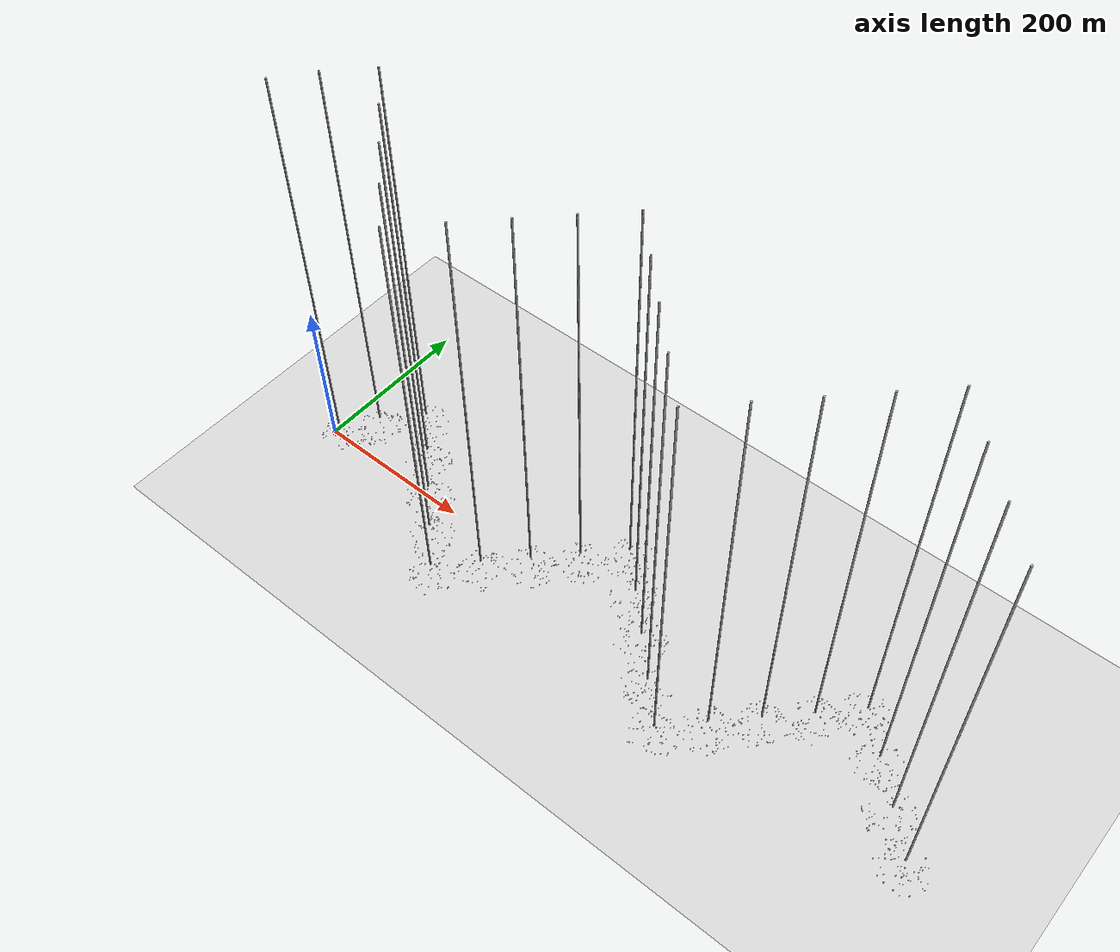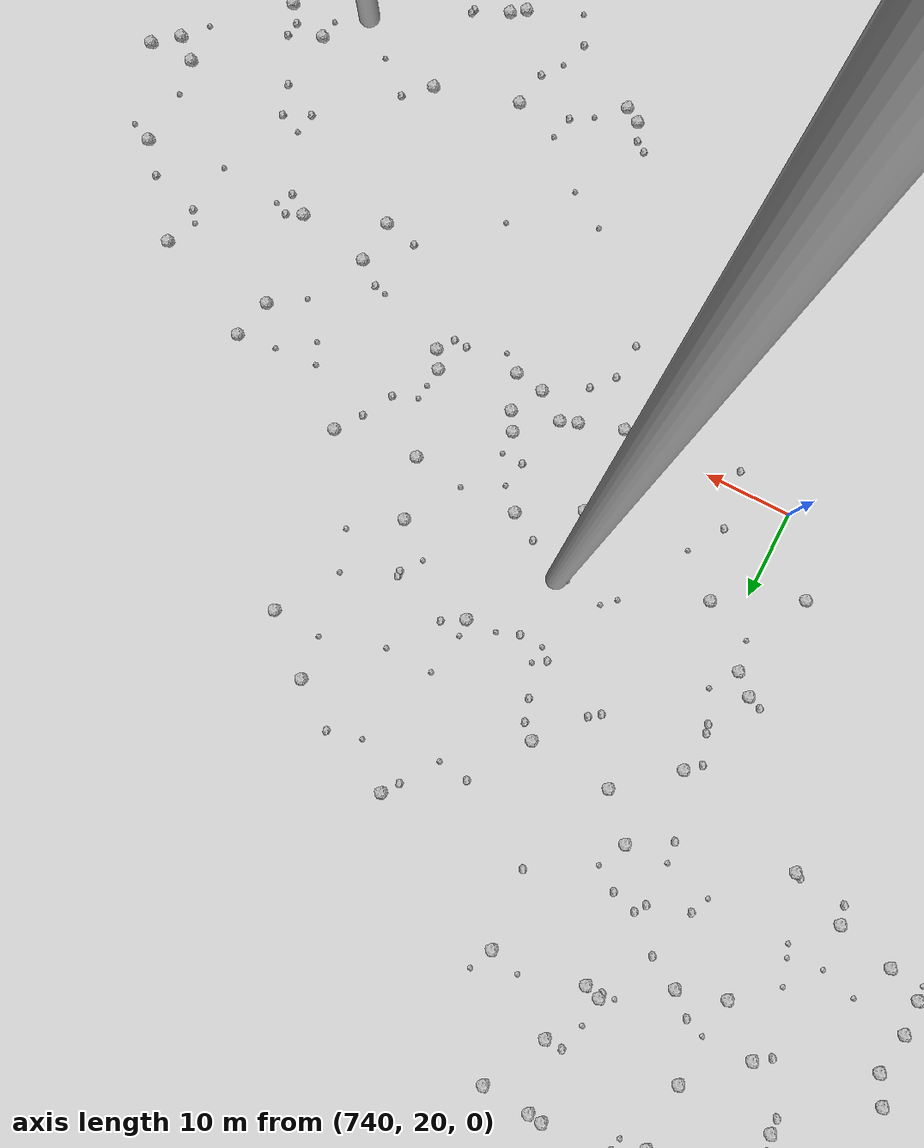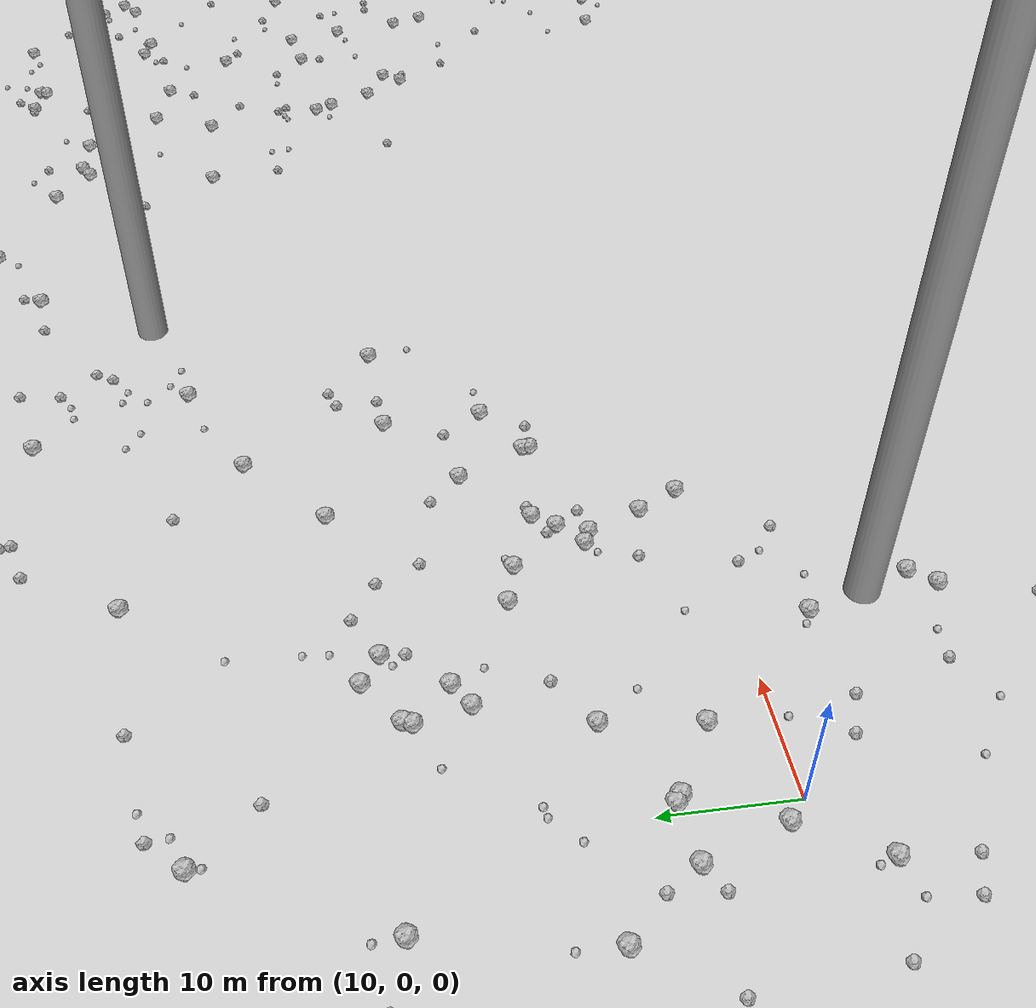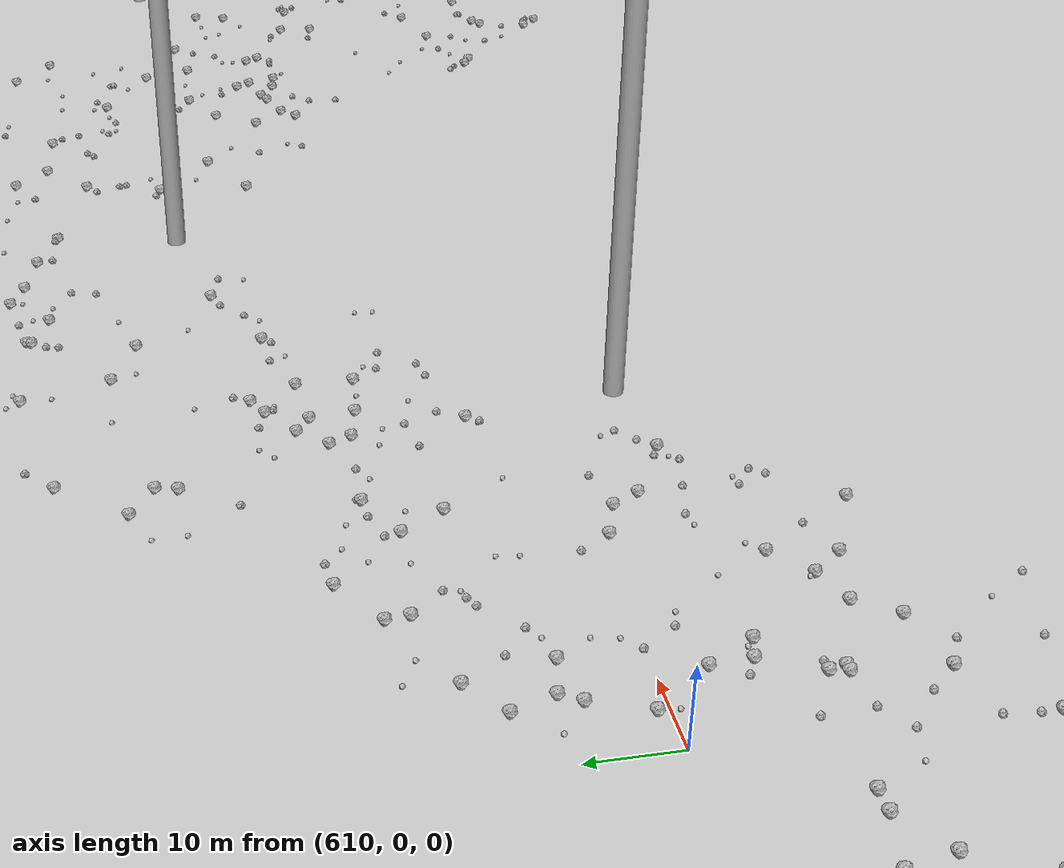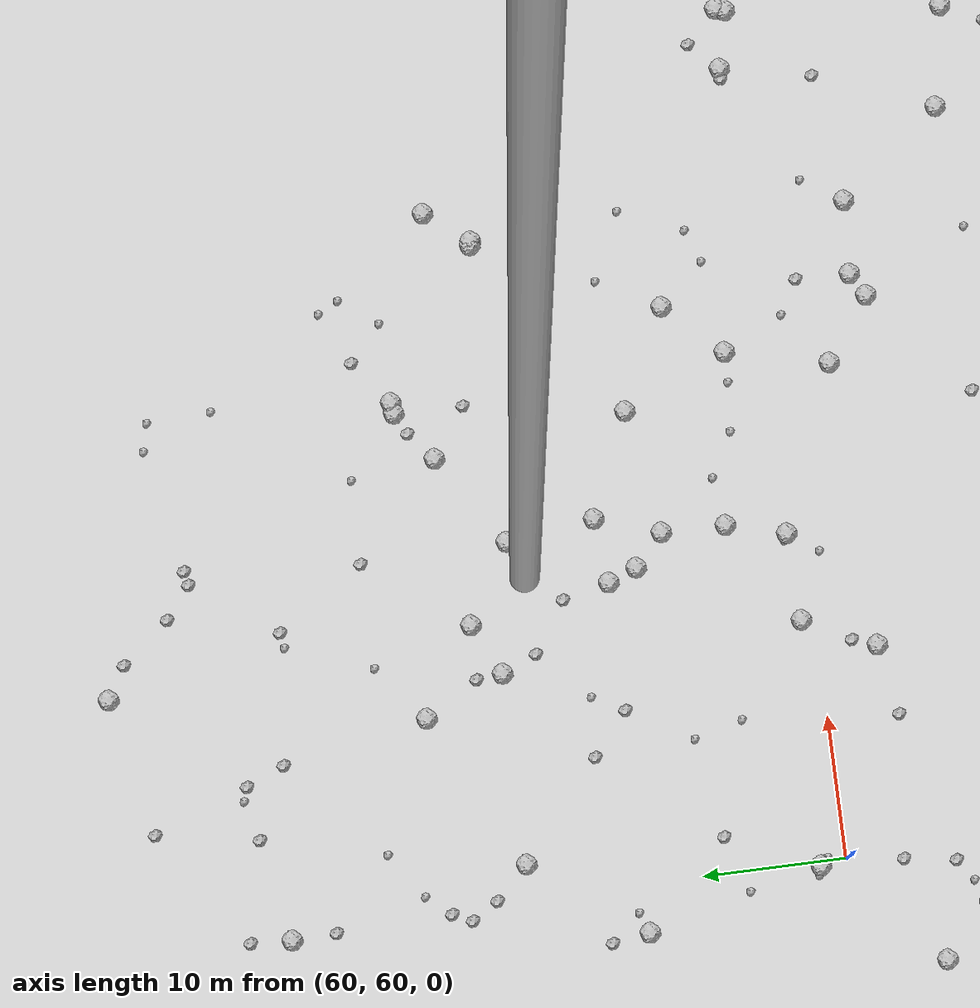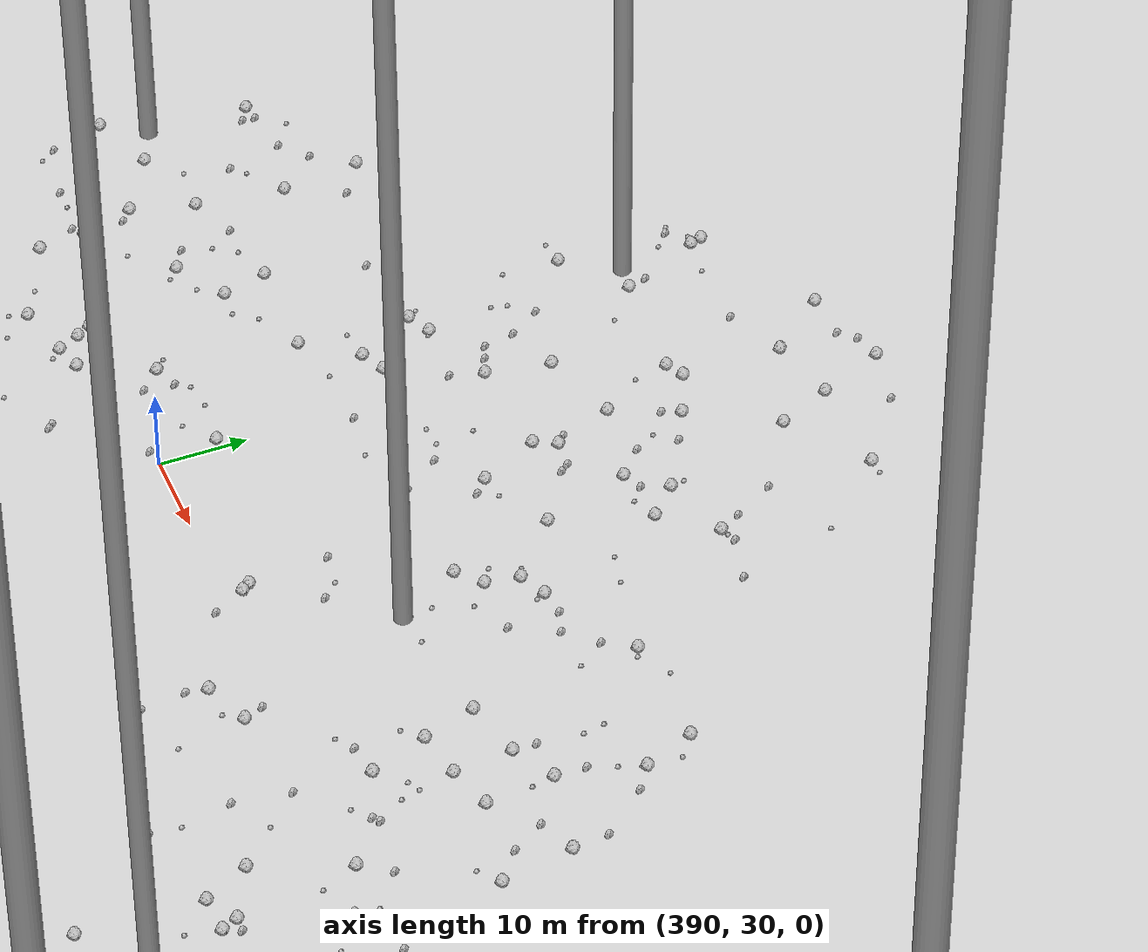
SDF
<sdf version="1.6">
 <world name="default">
  <include><uri>model://custom_ground</uri></include>
  <include><uri>model://sun</uri></include>
  <spherical_coordinates>
   <surface_model>EARTH_WGS84</surface_model>
   <latitude_deg>38.161479</latitude_deg>
   <longitude_deg>-122.454630</longitude_deg>
   <elevation>488.0</elevation>
   <heading_deg>90</heading_deg>
  </spherical_coordinates>
  <model name="rock1_0_0">
   <include><uri>model://rock1</uri><pose>-9.71555381848496 -11.462800521649633 0.5 0 0 0</pose></include>
  </model>
  <model name="rock1_0_1">
   <include><uri>model://rock1</uri><pose>33.012249444664626 15.732189921044622 0.5 0 0 0</pose></include>
  </model>
  <model name="rock1_0_2">
   <include><uri>model://rock1</uri><pose>-2.6610322005692346 -13.892146646583857 0.5 0 0 0</pose></include>
  </model>
  <model name="rock1_0_3">
   <include><uri>model://rock1</uri><pose>11.343023795016094 8.002617359840393 0.5 0 0 0</pose></include>
  </model>
  <model name="rock1_0_4">
   <include><uri>model://rock1</uri><pose>26.891499211915253 -15.973941546690448 0.5 0 0 0</pose></include>
  </model>
  <model name="rock1_0_5">
   <include><uri>model://rock1</uri><pose>-3.9119274705224036 7.720105783129689 0.5 0 0 0</pose></include>
  </model>
  <model name="rock1_0_6">
   <include><uri>model://rock1</uri><pose>37.793475113117815 4.770822017862116 0.5 0 0 0</pose></include>
  </model>
  <model name="rock1_0_7">
   <include><uri>model://rock1</uri><pose>36.00149346547439 9.25231353364763 0.5 0 0 0</pose></include>
  </model>
  <model name="rock1_0_8">
   <include><uri>model://rock1</uri><pose>-11.788210217342206 12.76895249197841 0.5 0 0 0</pose></include>
  </model>
  <model name="rock1_0_9">
   <include><uri>model://rock1</uri><pose>-7.843985306245839 -14.037542996310147 0.5 0 0 0</pose></include>
  </model>
  <model name="rock1_0_10">
   <include><uri>model://rock1</uri><pose>4.049735617796667 26.567867269111986 0.5 0 0 0</pose></include>
  </model>
  <model name="rock1_0_11">
   <include><uri>model://rock1</uri><pose>8.454805740521142 1.564320129808202 0.5 0 0 0</pose></include>
  </model>
  <model name="rock1_0_12">
   <include><uri>model://rock1</uri><pose>17.706860088040706 12.249815178051726 0.5 0 0 0</pose></include>
  </model>
  <model name="rock1_0_13">
   <include><uri>model://rock1</uri><pose>6.289367280612904 7.993429714953152 0.5 0 0 0</pose></include>
  </model>
  <model name="rock1_0_14">
   <include><uri>model://rock1</uri><pose>16.75083652591755 4.8069718419666785 0.5 0 0 0</pose></include>
  </model>
  <model name="rock1_0_15">
   <include><uri>model://rock1</uri><pose>39.66175471702922 1.3362825235050835 0.5 0 0 0</pose></include>
  </model>
  <model name="rock1_0_16">
   <include><uri>model://rock1</uri><pose>36.9854462198996 11.69511256799273 0.5 0 0 0</pose></include>
  </model>
  <model name="rock1_0_17">
   <include><uri>model://rock1</uri><pose>10.832708672551512 8.42902878941868 0.5 0 0 0</pose></include>
  </model>
  <model name="rock1_0_18">
   <include><uri>model://rock1</uri><pose>28.430271240194656 -14.085184852996552 0.5 0 0 0</pose></include>
  </model>
  <model name="rock1_0_19">
   <include><uri>model://rock1</uri><pose>34.779293022524094 9.793548759535028 0.5 0 0 0</pose></include>
  </model>
  <model name="rock1_0_20">
   <include><uri>model://rock1</uri><pose>20.354891933034942 20.570803612729 0.5 0 0 0</pose></include>
  </model>
  <model name="rock1_0_21">
   <include><uri>model://rock1</uri><pose>1.6570915613505264 13.608310073899268 0.5 0 0 0</pose></include>
  </model>
  <model name="rock1_0_22">
   <include><uri>model://rock1</uri><pose>5.131230323033968 -4.332906194362913 0.5 0 0 0</pose></include>
  </model>
  <model name="rock1_0_23">
   <include><uri>model://rock1</uri><pose>22.383828166170908 21.811605074972597 0.5 0 0 0</pose></include>
  </model>
  <model name="rock1_0_24">
   <include><uri>model://rock1</uri><pose>25.565425479144047 -5.383615214027234 0.5 0 0 0</pose></include>
  </model>
  <model name="rock1_0_25">
   <include><uri>model://rock1</uri><pose>-13.256966389951419 3.5022745994535853 0.5 0 0 0</pose></include>
  </model>
  <model name="rock1_0_26">
   <include><uri>model://rock1</uri><pose>-12.73764506008726 -0.4814348297298352 0.5 0 0 0</pose></include>
  </model>
  <model name="rock2_0_0">
   <include><uri>model://rock2</uri><pose>-0.193031894374613 -21.17150524556228 0.3 0 0 0</pose></include>
  </model>
  <model name="rock2_0_1">
   <include><uri>model://rock2</uri><pose>-3.1879779696785313 -17.294899190971044 0.3 0 0 0</pose></include>
  </model>
  <model name="rock2_0_2">
   <include><uri>model://rock2</uri><pose>14.367108066171852 -4.976253858326544 0.3 0 0 0</pose></include>
  </model>
  <model name="rock2_0_3">
   <include><uri>model://rock2</uri><pose>4.198408401762421 6.830315012326025 0.3 0 0 0</pose></include>
  </model>
  <model name="rock2_0_4">
   <include><uri>model://rock2</uri><pose>-9.3930427309923 8.779824626320568 0.3 0 0 0</pose></include>
  </model>
  <model name="rock2_0_5">
   <include><uri>model://rock2</uri><pose>38.35460840925422 9.691162270387267 0.3 0 0 0</pose></include>
  </model>
  <model name="rock2_0_6">
   <include><uri>model://rock2</uri><pose>-5.8002079999645435 -14.335907675741668 0.3 0 0 0</pose></include>
  </model>
  <model name="rock2_0_7">
   <include><uri>model://rock2</uri><pose>36.24455740181333 12.503229338205571 0.3 0 0 0</pose></include>
  </model>
  <model name="rock2_0_8">
   <include><uri>model://rock2</uri><pose>-7.482483047048142 -1.7112312540761678 0.3 0 0 0</pose></include>
  </model>
  <model name="rock2_0_9">
   <include><uri>model://rock2</uri><pose>24.96900393877643 -23.161453676621232 0.3 0 0 0</pose></include>
  </model>
  <model name="rock2_0_10">
   <include><uri>model://rock2</uri><pose>-0.5074817209366032 27.925603957213603 0.3 0 0 0</pose></include>
  </model>
  <model name="rock2_0_11">
   <include><uri>model://rock2</uri><pose>-1.6628222340463097 -2.660903800111619 0.3 0 0 0</pose></include>
  </model>
  <model name="rock2_0_12">
   <include><uri>model://rock2</uri><pose>17.574762148474115 -6.158641049243343 0.3 0 0 0</pose></include>
  </model>
  <model name="rock2_0_13">
   <include><uri>model://rock2</uri><pose>4.625832917898663 -9.65438918216902 0.3 0 0 0</pose></include>
  </model>
  <model name="rock2_0_14">
   <include><uri>model://rock2</uri><pose>-13.443121035230767 -18.671103302931577 0.3 0 0 0</pose></include>
  </model>
  <model name="rock2_0_15">
   <include><uri>model://rock2</uri><pose>32.7352443328051 5.881119437303255 0.3 0 0 0</pose></include>
  </model>
  <model name="rock2_0_16">
   <include><uri>model://rock2</uri><pose>25.496737226937306 24.702843289262745 0.3 0 0 0</pose></include>
  </model>
  <model name="rock2_0_17">
   <include><uri>model://rock2</uri><pose>34.4818310107314 -5.1766480054246955 0.3 0 0 0</pose></include>
  </model>
  <model name="rock2_0_18">
   <include><uri>model://rock2</uri><pose>4.60970853917398 10.562812096201355 0.3 0 0 0</pose></include>
  </model>
  <model name="rock2_0_19">
   <include><uri>model://rock2</uri><pose>21.626145216935683 14.786414000920907 0.3 0 0 0</pose></include>
  </model>
  <model name="rock2_0_20">
   <include><uri>model://rock2</uri><pose>-15.379537570443855 3.3324368677108396 0.3 0 0 0</pose></include>
  </model>
  <model name="rock2_0_21">
   <include><uri>model://rock2</uri><pose>-7.948083935329869 -6.879009140253249 0.3 0 0 0</pose></include>
  </model>
  <model name="rock2_0_22">
   <include><uri>model://rock2</uri><pose>19.774315316027874 -13.928975209632245 0.3 0 0 0</pose></include>
  </model>
  <model name="rock2_0_23">
   <include><uri>model://rock2</uri><pose>31.073368216654075 -1.5937646047993184 0.3 0 0 0</pose></include>
  </model>
  <model name="rock2_0_24">
   <include><uri>model://rock2</uri><pose>-13.300573741668932 8.696321581078053 0.3 0 0 0</pose></include>
  </model>
  <model name="rock2_0_25">
   <include><uri>model://rock2</uri><pose>1.8192048683438529 -8.565443580151438 0.3 0 0 0</pose></include>
  </model>
  <model name="rock2_0_26">
   <include><uri>model://rock2</uri><pose>-2.3911151887175244 7.554301789438881 0.3 0 0 0</pose></include>
  </model>
  <model name="rock3_0_0">
   <include><uri>model://rock3</uri><pose>-6.098758536424624 4.204453950853448 0.2 0 0 0</pose></include>
  </model>
  <model name="rock3_0_1">
   <include><uri>model://rock3</uri><pose>19.864726823202908 25.21635707290327 0.2 0 0 0</pose></include>
  </model>
  <model name="rock3_0_2">
   <include><uri>model://rock3</uri><pose>-5.662739801054137 14.914763377907583 0.2 0 0 0</pose></include>
  </model>
  <model name="rock3_0_3">
   <include><uri>model://rock3</uri><pose>-5.93577178517392 -4.310459242684857 0.2 0 0 0</pose></include>
  </model>
  <model name="rock3_0_4">
   <include><uri>model://rock3</uri><pose>33.663894922679795 8.92634262247772 0.2 0 0 0</pose></include>
  </model>
  <model name="rock3_0_5">
   <include><uri>model://rock3</uri><pose>16.427406688190324 -0.9708809356751615 0.2 0 0 0</pose></include>
  </model>
  <model name="rock3_0_6">
   <include><uri>model://rock3</uri><pose>3.914921150732802 28.61833618083378 0.2 0 0 0</pose></include>
  </model>
  <model name="rock3_0_7">
   <include><uri>model://rock3</uri><pose>11.573813010739912 -13.091859964697868 0.2 0 0 0</pose></include>
  </model>
  <model name="rock3_0_8">
   <include><uri>model://rock3</uri><pose>-1.0961135472465031 25.554846052672538 0.2 0 0 0</pose></include>
  </model>
  <model name="rock3_0_9">
   <include><uri>model://rock3</uri><pose>26.022047706967122 -5.452999875553992 0.2 0 0 0</pose></include>
  </model>
  <model name="rock3_0_10">
   <include><uri>model://rock3</uri><pose>16.041357707593185 -16.1587914583108 0.2 0 0 0</pose></include>
  </model>
  <model name="rock3_0_11">
   <include><uri>model://rock3</uri><pose>4.669298061600362 -3.126888689003696 0.2 0 0 0</pose></include>
  </model>
  <model name="rock3_0_12">
   <include><uri>model://rock3</uri><pose>24.322472382635063 -4.874149499707684 0.2 0 0 0</pose></include>
  </model>
  <model name="rock3_0_13">
   <include><uri>model://rock3</uri><pose>32.052703959578444 -3.604360074156908 0.2 0 0 0</pose></include>
  </model>
  <model name="rock3_0_14">
   <include><uri>model://rock3</uri><pose>22.46250992392075 -14.225532545522645 0.2 0 0 0</pose></include>
  </model>
  <model name="rock3_0_15">
   <include><uri>model://rock3</uri><pose>33.929560716040264 16.174359468695478 0.2 0 0 0</pose></include>
  </model>
  <model name="rock3_0_16">
   <include><uri>model://rock3</uri><pose>8.83391368394745 14.863860513092618 0.2 0 0 0</pose></include>
  </model>
  <model name="rock3_0_17">
   <include><uri>model://rock3</uri><pose>26.81317969857011 3.68266613555987 0.2 0 0 0</pose></include>
  </model>
  <model name="rock3_0_18">
   <include><uri>model://rock3</uri><pose>24.62282750131935 25.666306147279656 0.2 0 0 0</pose></include>
  </model>
  <model name="rock3_0_19">
   <include><uri>model://rock3</uri><pose>11.698648951352236 16.972429555457346 0.2 0 0 0</pose></include>
  </model>
  <model name="rock3_0_20">
   <include><uri>model://rock3</uri><pose>1.7263865613114078 16.75518370574504 0.2 0 0 0</pose></include>
  </model>
  <model name="rock3_0_21">
   <include><uri>model://rock3</uri><pose>15.510762060354821 23.15160866660422 0.2 0 0 0</pose></include>
  </model>
  <model name="rock3_0_22">
   <include><uri>model://rock3</uri><pose>20.170073773151337 8.823424460293552 0.2 0 0 0</pose></include>
  </model>
  <model name="rock3_0_23">
   <include><uri>model://rock3</uri><pose>10.851161087999344 16.82221732983104 0.2 0 0 0</pose></include>
  </model>
  <model name="rock3_0_24">
   <include><uri>model://rock3</uri><pose>6.570793116307879 -21.986020540295307 0.2 0 0 0</pose></include>
  </model>
  <model name="rock3_0_25">
   <include><uri>model://rock3</uri><pose>29.137827871594183 -6.277082084384972 0.2 0 0 0</pose></include>
  </model>
  <model name="rock3_0_26">
   <include><uri>model://rock3</uri><pose>2.2203925251615466 -5.099327018992248 0.2 0 0 0</pose></include>
  </model>
  <model name="rock1_1_0">
   <include><uri>model://rock1</uri><pose>46.076341952057845 66.76205137634844 0.5 0 0 0</pose></include>
  </model>
  <model name="rock1_1_1">
   <include><uri>model://rock1</uri><pose>10.313711502681045 39.75464086229557 0.5 0 0 0</pose></include>
  </model>
  <model name="rock1_1_2">
   <include><uri>model://rock1</uri><pose>19.645931064644557 25.463567148665533 0.5 0 0 0</pose></include>
  </model>
  <model name="rock1_1_3">
   <include><uri>model://rock1</uri><pose>38.816207801266536 59.965327298604365 0.5 0 0 0</pose></include>
  </model>
  <model name="rock1_1_4">
   <include><uri>model://rock1</uri><pose>51.34665363214859 24.329659187274366 0.5 0 0 0</pose></include>
  </model>
  <model name="rock1_1_5">
   <include><uri>model://rock1</uri><pose>38.31611480656001 13.490914130884583 0.5 0 0 0</pose></include>
  </model>
  <model name="rock1_1_6">
   <include><uri>model://rock1</uri><pose>51.67961022476763 15.872993253240448 0.5 0 0 0</pose></include>
  </model>
  <model name="rock1_1_7">
   <include><uri>model://rock1</uri><pose>28.37347491050999 59.0402458762218 0.5 0 0 0</pose></include>
  </model>
  <model name="rock1_1_8">
   <include><uri>model://rock1</uri><pose>23.599733323003836 56.11295978279429 0.5 0 0 0</pose></include>
  </model>
  <model name="rock1_1_9">
   <include><uri>model://rock1</uri><pose>40.53566747122842 29.794549433709914 0.5 0 0 0</pose></include>
  </model>
  <model name="rock1_1_10">
   <include><uri>model://rock1</uri><pose>61.25530763543188 24.968532550296317 0.5 0 0 0</pose></include>
  </model>
  <model name="rock1_1_11">
   <include><uri>model://rock1</uri><pose>29.50497542507285 16.66941774619498 0.5 0 0 0</pose></include>
  </model>
  <model name="rock1_1_12">
   <include><uri>model://rock1</uri><pose>57.77952202910664 41.23410077025172 0.5 0 0 0</pose></include>
  </model>
  <model name="rock1_1_13">
   <include><uri>model://rock1</uri><pose>25.67692202940621 26.570029488575628 0.5 0 0 0</pose></include>
  </model>
  <model name="rock1_1_14">
   <include><uri>model://rock1</uri><pose>47.63978855326613 36.32308934922034 0.5 0 0 0</pose></include>
  </model>
  <model name="rock1_1_15">
   <include><uri>model://rock1</uri><pose>19.376284008779116 24.778913290105926 0.5 0 0 0</pose></include>
  </model>
  <model name="rock1_1_16">
   <include><uri>model://rock1</uri><pose>43.70998387397748 18.66699288057326 0.5 0 0 0</pose></include>
  </model>
  <model name="rock1_1_17">
   <include><uri>model://rock1</uri><pose>46.5484528689444 12.895208491792712 0.5 0 0 0</pose></include>
  </model>
  <model name="rock1_1_18">
   <include><uri>model://rock1</uri><pose>19.609376978269594 58.19718704112967 0.5 0 0 0</pose></include>
  </model>
  <model name="rock1_1_19">
   <include><uri>model://rock1</uri><pose>48.28409263817507 62.21256217375583 0.5 0 0 0</pose></include>
  </model>
  <model name="rock1_1_20">
   <include><uri>model://rock1</uri><pose>35.78144299183946 61.142445974426785 0.5 0 0 0</pose></include>
  </model>
  <model name="rock1_1_21">
   <include><uri>model://rock1</uri><pose>46.58777591939076 12.318792180241422 0.5 0 0 0</pose></include>
  </model>
  <model name="rock1_1_22">
   <include><uri>model://rock1</uri><pose>40.883547210113925 67.24587002876493 0.5 0 0 0</pose></include>
  </model>
  <model name="rock1_1_23">
   <include><uri>model://rock1</uri><pose>23.28613467373515 28.0994210775915 0.5 0 0 0</pose></include>
  </model>
  <model name="rock1_1_24">
   <include><uri>model://rock1</uri><pose>52.26788304499492 54.01527019030589 0.5 0 0 0</pose></include>
  </model>
  <model name="rock1_1_25">
   <include><uri>model://rock1</uri><pose>32.75320727212417 45.419983268834436 0.5 0 0 0</pose></include>
  </model>
  <model name="rock1_1_26">
   <include><uri>model://rock1</uri><pose>25.39654915451589 59.97315707945448 0.5 0 0 0</pose></include>
  </model>
  <model name="rock2_1_0">
   <include><uri>model://rock2</uri><pose>39.322257256989 13.693150423857283 0.3 0 0 0</pose></include>
  </model>
  <model name="rock2_1_1">
   <include><uri>model://rock2</uri><pose>34.23031983527885 22.829298977305786 0.3 0 0 0</pose></include>
  </model>
  <model name="rock2_1_2">
   <include><uri>model://rock2</uri><pose>37.65519701732058 62.6216845841262 0.3 0 0 0</pose></include>
  </model>
  <model name="rock2_1_3">
   <include><uri>model://rock2</uri><pose>60.921639301286774 48.03898554218493 0.3 0 0 0</pose></include>
  </model>
  <model name="rock2_1_4">
   <include><uri>model://rock2</uri><pose>40.98334788705718 21.295475595638994 0.3 0 0 0</pose></include>
  </model>
  <model name="rock2_1_5">
   <include><uri>model://rock2</uri><pose>37.01486908027866 53.11888475472106 0.3 0 0 0</pose></include>
  </model>
  <model name="rock2_1_6">
   <include><uri>model://rock2</uri><pose>49.32047985536999 12.197813370537707 0.3 0 0 0</pose></include>
  </model>
  <model name="rock2_1_7">
   <include><uri>model://rock2</uri><pose>41.807550512154855 41.87599290938168 0.3 0 0 0</pose></include>
  </model>
  <model name="rock2_1_8">
   <include><uri>model://rock2</uri><pose>29.242496088914447 28.400345859088628 0.3 0 0 0</pose></include>
  </model>
  <model name="rock2_1_9">
   <include><uri>model://rock2</uri><pose>56.13178344027114 28.854905013452413 0.3 0 0 0</pose></include>
  </model>
  <model name="rock2_1_10">
   <include><uri>model://rock2</uri><pose>30.839069284251586 59.1078102324333 0.3 0 0 0</pose></include>
  </model>
  <model name="rock2_1_11">
   <include><uri>model://rock2</uri><pose>40.431497470558305 55.246975449019985 0.3 0 0 0</pose></include>
  </model>
  <model name="rock2_1_12">
   <include><uri>model://rock2</uri><pose>12.585999525589152 42.37779580024684 0.3 0 0 0</pose></include>
  </model>
  <model name="rock2_1_13">
   <include><uri>model://rock2</uri><pose>59.00386098465573 52.473843655192304 0.3 0 0 0</pose></include>
  </model>
  <model name="rock2_1_14">
   <include><uri>model://rock2</uri><pose>44.41016169180049 67.93299259543701 0.3 0 0 0</pose></include>
  </model>
  <model name="rock2_1_15">
   <include><uri>model://rock2</uri><pose>54.48479298239232 24.671351174537012 0.3 0 0 0</pose></include>
  </model>
  <model name="rock2_1_16">
   <include><uri>model://rock2</uri><pose>49.154096854616235 19.30980427931022 0.3 0 0 0</pose></include>
  </model>
  <model name="rock2_1_17">
   <include><uri>model://rock2</uri><pose>17.57127603615104 54.16561712116236 0.3 0 0 0</pose></include>
  </model>
  <model name="rock2_1_18">
   <include><uri>model://rock2</uri><pose>32.6344570740529 26.35654934876863 0.3 0 0 0</pose></include>
  </model>
  <model name="rock2_1_19">
   <include><uri>model://rock2</uri><pose>59.529886985980305 56.07321765009831 0.3 0 0 0</pose></include>
  </model>
  <model name="rock2_1_20">
   <include><uri>model://rock2</uri><pose>54.381971144944075 28.239030359043415 0.3 0 0 0</pose></include>
  </model>
  <model name="rock2_1_21">
   <include><uri>model://rock2</uri><pose>21.10597471639452 44.21057530372503 0.3 0 0 0</pose></include>
  </model>
  <model name="rock2_1_22">
   <include><uri>model://rock2</uri><pose>47.1168450407124 12.223634793757407 0.3 0 0 0</pose></include>
  </model>
  <model name="rock2_1_23">
   <include><uri>model://rock2</uri><pose>61.87497647874395 49.57791207441784 0.3 0 0 0</pose></include>
  </model>
  <model name="rock2_1_24">
   <include><uri>model://rock2</uri><pose>36.101387163450624 56.41137204445213 0.3 0 0 0</pose></include>
  </model>
  <model name="rock2_1_25">
   <include><uri>model://rock2</uri><pose>40.60664939943739 54.31827014635719 0.3 0 0 0</pose></include>
  </model>
  <model name="rock2_1_26">
   <include><uri>model://rock2</uri><pose>14.378745997519616 35.02571808299081 0.3 0 0 0</pose></include>
  </model>
  <model name="rock3_1_0">
   <include><uri>model://rock3</uri><pose>14.845469439339254 42.95646530474612 0.2 0 0 0</pose></include>
  </model>
  <model name="rock3_1_1">
   <include><uri>model://rock3</uri><pose>48.87636129733244 65.93244787722827 0.2 0 0 0</pose></include>
  </model>
  <model name="rock3_1_2">
   <include><uri>model://rock3</uri><pose>26.2396432719212 30.101285496081246 0.2 0 0 0</pose></include>
  </model>
  <model name="rock3_1_3">
   <include><uri>model://rock3</uri><pose>52.9494209973065 39.686982097779676 0.2 0 0 0</pose></include>
  </model>
  <model name="rock3_1_4">
   <include><uri>model://rock3</uri><pose>53.05667490297406 45.08178884956644 0.2 0 0 0</pose></include>
  </model>
  <model name="rock3_1_5">
   <include><uri>model://rock3</uri><pose>23.53006267008378 19.21348519353993 0.2 0 0 0</pose></include>
  </model>
  <model name="rock3_1_6">
   <include><uri>model://rock3</uri><pose>47.19839477212217 58.57788757976472 0.2 0 0 0</pose></include>
  </model>
  <model name="rock3_1_7">
   <include><uri>model://rock3</uri><pose>32.72115234808196 55.22032194532693 0.2 0 0 0</pose></include>
  </model>
  <model name="rock3_1_8">
   <include><uri>model://rock3</uri><pose>59.36422918775562 42.85086951922111 0.2 0 0 0</pose></include>
  </model>
  <model name="rock3_1_9">
   <include><uri>model://rock3</uri><pose>21.926869384229345 62.71858942066059 0.2 0 0 0</pose></include>
  </model>
  <model name="rock3_1_10">
   <include><uri>model://rock3</uri><pose>51.21645330759275 46.228652239211 0.2 0 0 0</pose></include>
  </model>
  <model name="rock3_1_11">
   <include><uri>model://rock3</uri><pose>61.52674609689055 41.96575921945046 0.2 0 0 0</pose></include>
  </model>
  <model name="rock3_1_12">
   <include><uri>model://rock3</uri><pose>26.70149385125864 37.55088191321278 0.2 0 0 0</pose></include>
  </model>
  <model name="rock3_1_13">
   <include><uri>model://rock3</uri><pose>57.45852414463915 51.39218369760155 0.2 0 0 0</pose></include>
  </model>
  <model name="rock3_1_14">
   <include><uri>model://rock3</uri><pose>17.371369906026697 58.10436720800993 0.2 0 0 0</pose></include>
  </model>
  <model name="rock3_1_15">
   <include><uri>model://rock3</uri><pose>10.298713184049683 38.72122583343095 0.2 0 0 0</pose></include>
  </model>
  <model name="rock3_1_16">
   <include><uri>model://rock3</uri><pose>54.72350625776017 15.965892919924276 0.2 0 0 0</pose></include>
  </model>
  <model name="rock3_1_17">
   <include><uri>model://rock3</uri><pose>26.417711012690155 32.04786813566747 0.2 0 0 0</pose></include>
  </model>
  <model name="rock3_1_18">
   <include><uri>model://rock3</uri><pose>61.88924155251626 21.309740670023714 0.2 0 0 0</pose></include>
  </model>
  <model name="rock3_1_19">
   <include><uri>model://rock3</uri><pose>59.08205194803904 61.98697342233881 0.2 0 0 0</pose></include>
  </model>
  <model name="rock3_1_20">
   <include><uri>model://rock3</uri><pose>57.33418879092398 44.767022181694976 0.2 0 0 0</pose></include>
  </model>
  <model name="rock3_1_21">
   <include><uri>model://rock3</uri><pose>55.893410318394444 51.00734018332366 0.2 0 0 0</pose></include>
  </model>
  <model name="rock3_1_22">
   <include><uri>model://rock3</uri><pose>38.86087710232077 68.81964275788232 0.2 0 0 0</pose></include>
  </model>
  <model name="rock3_1_23">
   <include><uri>model://rock3</uri><pose>12.754153311580207 40.75847723438579 0.2 0 0 0</pose></include>
  </model>
  <model name="rock3_1_24">
   <include><uri>model://rock3</uri><pose>58.97831228475758 46.575370068440826 0.2 0 0 0</pose></include>
  </model>
  <model name="rock3_1_25">
   <include><uri>model://rock3</uri><pose>60.23524330313954 61.29373904214017 0.2 0 0 0</pose></include>
  </model>
  <model name="rock3_1_26">
   <include><uri>model://rock3</uri><pose>57.55012510280042 46.94835382745257 0.2 0 0 0</pose></include>
  </model>
  <model name="rock1_2_0">
   <include><uri>model://rock1</uri><pose>106.20541803177619 80.51024265904096 0.5 0 0 0</pose></include>
  </model>
  <model name="rock1_2_1">
   <include><uri>model://rock1</uri><pose>94.74915366096235 87.32517444133961 0.5 0 0 0</pose></include>
  </model>
  <model name="rock1_2_2">
   <include><uri>model://rock1</uri><pose>85.66311600462082 74.39057148021075 0.5 0 0 0</pose></include>
  </model>
  <model name="rock1_2_3">
   <include><uri>model://rock1</uri><pose>59.76504346197538 61.83992780926038 0.5 0 0 0</pose></include>
  </model>
  <model name="rock1_2_4">
   <include><uri>model://rock1</uri><pose>92.92223642235842 71.28088206349106 0.5 0 0 0</pose></include>
  </model>
  <model name="rock1_2_5">
   <include><uri>model://rock1</uri><pose>105.91614843386992 80.58850280757386 0.5 0 0 0</pose></include>
  </model>
  <model name="rock1_2_6">
   <include><uri>model://rock1</uri><pose>84.10130705160054 65.34866225516141 0.5 0 0 0</pose></include>
  </model>
  <model name="rock1_2_7">
   <include><uri>model://rock1</uri><pose>75.70756432746151 82.03048784707269 0.5 0 0 0</pose></include>
  </model>
  <model name="rock1_2_8">
   <include><uri>model://rock1</uri><pose>73.2508824761328 87.62976021824059 0.5 0 0 0</pose></include>
  </model>
  <model name="rock1_2_9">
   <include><uri>model://rock1</uri><pose>79.33117999118511 83.79700367388915 0.5 0 0 0</pose></include>
  </model>
  <model name="rock1_2_10">
   <include><uri>model://rock1</uri><pose>82.99803398698049 61.18816147993827 0.5 0 0 0</pose></include>
  </model>
  <model name="rock1_2_11">
   <include><uri>model://rock1</uri><pose>84.81664096637152 80.64148557871098 0.5 0 0 0</pose></include>
  </model>
  <model name="rock1_2_12">
   <include><uri>model://rock1</uri><pose>108.57652239032937 83.60355446150669 0.5 0 0 0</pose></include>
  </model>
  <model name="rock1_2_13">
   <include><uri>model://rock1</uri><pose>76.8502325431744 60.9627534113944 0.5 0 0 0</pose></include>
  </model>
  <model name="rock1_2_14">
   <include><uri>model://rock1</uri><pose>95.53591184028673 87.43722459288902 0.5 0 0 0</pose></include>
  </model>
  <model name="rock1_2_15">
   <include><uri>model://rock1</uri><pose>84.14580841800428 69.8441993014469 0.5 0 0 0</pose></include>
  </model>
  <model name="rock1_2_16">
   <include><uri>model://rock1</uri><pose>94.5532782663442 56.66925808967358 0.5 0 0 0</pose></include>
  </model>
  <model name="rock1_2_17">
   <include><uri>model://rock1</uri><pose>96.2092251637574 63.84731482490448 0.5 0 0 0</pose></include>
  </model>
  <model name="rock1_2_18">
   <include><uri>model://rock1</uri><pose>77.25031027047581 109.3761253375717 0.5 0 0 0</pose></include>
  </model>
  <model name="rock1_2_19">
   <include><uri>model://rock1</uri><pose>59.17388012075119 98.70204788698268 0.5 0 0 0</pose></include>
  </model>
  <model name="rock1_2_20">
   <include><uri>model://rock1</uri><pose>99.92645525114241 67.82882207559462 0.5 0 0 0</pose></include>
  </model>
  <model name="rock1_2_21">
   <include><uri>model://rock1</uri><pose>81.11402435828997 73.91746438846127 0.5 0 0 0</pose></include>
  </model>
  <model name="rock1_2_22">
   <include><uri>model://rock1</uri><pose>56.640145580956016 74.14123678903199 0.5 0 0 0</pose></include>
  </model>
  <model name="rock1_2_23">
   <include><uri>model://rock1</uri><pose>62.370122860717146 82.01255740453306 0.5 0 0 0</pose></include>
  </model>
  <model name="rock1_2_24">
   <include><uri>model://rock1</uri><pose>91.24086559368646 84.8907916223717 0.5 0 0 0</pose></include>
  </model>
  <model name="rock1_2_25">
   <include><uri>model://rock1</uri><pose>81.90190248501584 71.8975014885163 0.5 0 0 0</pose></include>
  </model>
  <model name="rock1_2_26">
   <include><uri>model://rock1</uri><pose>74.49581819610542 55.94869014074024 0.5 0 0 0</pose></include>
  </model>
  <model name="rock2_2_0">
   <include><uri>model://rock2</uri><pose>75.5082372719599 83.87862886909002 0.3 0 0 0</pose></include>
  </model>
  <model name="rock2_2_1">
   <include><uri>model://rock2</uri><pose>56.21231562214653 76.79031384254402 0.3 0 0 0</pose></include>
  </model>
  <model name="rock2_2_2">
   <include><uri>model://rock2</uri><pose>79.52372022906997 108.07159576017634 0.3 0 0 0</pose></include>
  </model>
  <model name="rock2_2_3">
   <include><uri>model://rock2</uri><pose>84.52439570920106 90.90638776942096 0.3 0 0 0</pose></include>
  </model>
  <model name="rock2_2_4">
   <include><uri>model://rock2</uri><pose>85.538960745933 103.17299783605918 0.3 0 0 0</pose></include>
  </model>
  <model name="rock2_2_5">
   <include><uri>model://rock2</uri><pose>59.2754142474825 95.62101328091964 0.3 0 0 0</pose></include>
  </model>
  <model name="rock2_2_6">
   <include><uri>model://rock2</uri><pose>76.77587567575364 79.57548730826443 0.3 0 0 0</pose></include>
  </model>
  <model name="rock2_2_7">
   <include><uri>model://rock2</uri><pose>66.29741236990225 100.12902221649455 0.3 0 0 0</pose></include>
  </model>
  <model name="rock2_2_8">
   <include><uri>model://rock2</uri><pose>69.5236956304562 55.072625301594584 0.3 0 0 0</pose></include>
  </model>
  <model name="rock2_2_9">
   <include><uri>model://rock2</uri><pose>80.44977964554994 97.04015483554667 0.3 0 0 0</pose></include>
  </model>
  <model name="rock2_2_10">
   <include><uri>model://rock2</uri><pose>80.29867819235 77.23043941290098 0.3 0 0 0</pose></include>
  </model>
  <model name="rock2_2_11">
   <include><uri>model://rock2</uri><pose>59.29683880953827 101.60165499362313 0.3 0 0 0</pose></include>
  </model>
  <model name="rock2_2_12">
   <include><uri>model://rock2</uri><pose>75.0586293868709 57.65189335407213 0.3 0 0 0</pose></include>
  </model>
  <model name="rock2_2_13">
   <include><uri>model://rock2</uri><pose>62.54604937478751 68.22161034083115 0.3 0 0 0</pose></include>
  </model>
  <model name="rock2_2_14">
   <include><uri>model://rock2</uri><pose>94.69570781373925 82.48760623914812 0.3 0 0 0</pose></include>
  </model>
  <model name="rock2_2_15">
   <include><uri>model://rock2</uri><pose>72.1198199978364 73.89259588173311 0.3 0 0 0</pose></include>
  </model>
  <model name="rock2_2_16">
   <include><uri>model://rock2</uri><pose>93.22580567747913 86.55836536758565 0.3 0 0 0</pose></include>
  </model>
  <model name="rock2_2_17">
   <include><uri>model://rock2</uri><pose>67.51624581095632 107.27429323379026 0.3 0 0 0</pose></include>
  </model>
  <model name="rock2_2_18">
   <include><uri>model://rock2</uri><pose>58.93671663964503 86.18244177287961 0.3 0 0 0</pose></include>
  </model>
  <model name="rock2_2_19">
   <include><uri>model://rock2</uri><pose>69.13159377540441 76.37522575499425 0.3 0 0 0</pose></include>
  </model>
  <model name="rock2_2_20">
   <include><uri>model://rock2</uri><pose>98.6527888591497 89.86199757348595 0.3 0 0 0</pose></include>
  </model>
  <model name="rock2_2_21">
   <include><uri>model://rock2</uri><pose>60.084613932712536 84.32885186340032 0.3 0 0 0</pose></include>
  </model>
  <model name="rock2_2_22">
   <include><uri>model://rock2</uri><pose>70.07259906833096 100.57784278428718 0.3 0 0 0</pose></include>
  </model>
  <model name="rock2_2_23">
   <include><uri>model://rock2</uri><pose>59.56396159280622 87.5510606149614 0.3 0 0 0</pose></include>
  </model>
  <model name="rock2_2_24">
   <include><uri>model://rock2</uri><pose>71.23769657749456 97.88355295584944 0.3 0 0 0</pose></include>
  </model>
  <model name="rock2_2_25">
   <include><uri>model://rock2</uri><pose>82.30303997948536 104.72863287328127 0.3 0 0 0</pose></include>
  </model>
  <model name="rock2_2_26">
   <include><uri>model://rock2</uri><pose>84.56198505460588 102.97846525048436 0.3 0 0 0</pose></include>
  </model>
  <model name="rock3_2_0">
   <include><uri>model://rock3</uri><pose>102.36009927759963 91.70843235003247 0.2 0 0 0</pose></include>
  </model>
  <model name="rock3_2_1">
   <include><uri>model://rock3</uri><pose>60.96675278366422 89.22615378943911 0.2 0 0 0</pose></include>
  </model>
  <model name="rock3_2_2">
   <include><uri>model://rock3</uri><pose>58.5485092818666 66.86599747177335 0.2 0 0 0</pose></include>
  </model>
  <model name="rock3_2_3">
   <include><uri>model://rock3</uri><pose>79.33400876252804 96.84622599749355 0.2 0 0 0</pose></include>
  </model>
  <model name="rock3_2_4">
   <include><uri>model://rock3</uri><pose>77.1465758960249 90.80527260308165 0.2 0 0 0</pose></include>
  </model>
  <model name="rock3_2_5">
   <include><uri>model://rock3</uri><pose>96.20677478303122 104.53987111137161 0.2 0 0 0</pose></include>
  </model>
  <model name="rock3_2_6">
   <include><uri>model://rock3</uri><pose>103.1495651293393 90.26306813683667 0.2 0 0 0</pose></include>
  </model>
  <model name="rock3_2_7">
   <include><uri>model://rock3</uri><pose>64.16882209303799 91.43692414679171 0.2 0 0 0</pose></include>
  </model>
  <model name="rock3_2_8">
   <include><uri>model://rock3</uri><pose>96.4562949221841 100.00720088813748 0.2 0 0 0</pose></include>
  </model>
  <model name="rock3_2_9">
   <include><uri>model://rock3</uri><pose>101.18378764108775 87.57823702753711 0.2 0 0 0</pose></include>
  </model>
  <model name="rock3_2_10">
   <include><uri>model://rock3</uri><pose>70.4452364574236 65.92369870558849 0.2 0 0 0</pose></include>
  </model>
  <model name="rock3_2_11">
   <include><uri>model://rock3</uri><pose>107.05083426890498 70.03699039293956 0.2 0 0 0</pose></include>
  </model>
  <model name="rock3_2_12">
   <include><uri>model://rock3</uri><pose>105.12680117399215 65.49864849330523 0.2 0 0 0</pose></include>
  </model>
  <model name="rock3_2_13">
   <include><uri>model://rock3</uri><pose>69.51140926341284 69.3427891353745 0.2 0 0 0</pose></include>
  </model>
  <model name="rock3_2_14">
   <include><uri>model://rock3</uri><pose>90.41826712366341 90.82170629347041 0.2 0 0 0</pose></include>
  </model>
  <model name="rock3_2_15">
   <include><uri>model://rock3</uri><pose>73.30170615149687 76.11115472165773 0.2 0 0 0</pose></include>
  </model>
  <model name="rock3_2_16">
   <include><uri>model://rock3</uri><pose>58.05459666312975 74.68675808015686 0.2 0 0 0</pose></include>
  </model>
  <model name="rock3_2_17">
   <include><uri>model://rock3</uri><pose>90.57679473527045 64.12572723124518 0.2 0 0 0</pose></include>
  </model>
  <model name="rock3_2_18">
   <include><uri>model://rock3</uri><pose>87.4870177936792 65.78578131660217 0.2 0 0 0</pose></include>
  </model>
  <model name="rock3_2_19">
   <include><uri>model://rock3</uri><pose>81.48166623528556 59.045981571674204 0.2 0 0 0</pose></include>
  </model>
  <model name="rock3_2_20">
   <include><uri>model://rock3</uri><pose>102.77290055445744 64.60687161742871 0.2 0 0 0</pose></include>
  </model>
  <model name="rock3_2_21">
   <include><uri>model://rock3</uri><pose>82.50026596081662 61.374396345944966 0.2 0 0 0</pose></include>
  </model>
  <model name="rock3_2_22">
   <include><uri>model://rock3</uri><pose>94.23335495446881 104.98787110671663 0.2 0 0 0</pose></include>
  </model>
  <model name="rock3_2_23">
   <include><uri>model://rock3</uri><pose>69.0736541180192 100.88208093696107 0.2 0 0 0</pose></include>
  </model>
  <model name="rock3_2_24">
   <include><uri>model://rock3</uri><pose>52.19666392059777 88.77173563202211 0.2 0 0 0</pose></include>
  </model>
  <model name="rock3_2_25">
   <include><uri>model://rock3</uri><pose>94.05237345239391 63.83958210891814 0.2 0 0 0</pose></include>
  </model>
  <model name="rock3_2_26">
   <include><uri>model://rock3</uri><pose>102.27691328018066 72.17772632832626 0.2 0 0 0</pose></include>
  </model>
  <model name="rock1_3_0">
   <include><uri>model://rock1</uri><pose>120.5728965976827 61.36712758686548 0.5 0 0 0</pose></include>
  </model>
  <model name="rock1_3_1">
   <include><uri>model://rock1</uri><pose>143.58941472617494 55.571874158098744 0.5 0 0 0</pose></include>
  </model>
  <model name="rock1_3_2">
   <include><uri>model://rock1</uri><pose>114.81046518279945 21.425179362262856 0.5 0 0 0</pose></include>
  </model>
  <model name="rock1_3_3">
   <include><uri>model://rock1</uri><pose>100.64127166038725 54.438706910103164 0.5 0 0 0</pose></include>
  </model>
  <model name="rock1_3_4">
   <include><uri>model://rock1</uri><pose>132.37264646371668 63.660669735294384 0.5 0 0 0</pose></include>
  </model>
  <model name="rock1_3_5">
   <include><uri>model://rock1</uri><pose>131.8746462403833 30.340629541199647 0.5 0 0 0</pose></include>
  </model>
  <model name="rock1_3_6">
   <include><uri>model://rock1</uri><pose>111.37858948001094 27.83038587698995 0.5 0 0 0</pose></include>
  </model>
  <model name="rock1_3_7">
   <include><uri>model://rock1</uri><pose>118.83353894550356 45.58791439590637 0.5 0 0 0</pose></include>
  </model>
  <model name="rock1_3_8">
   <include><uri>model://rock1</uri><pose>116.27930182276147 61.595799147812855 0.5 0 0 0</pose></include>
  </model>
  <model name="rock1_3_9">
   <include><uri>model://rock1</uri><pose>112.39698757480953 25.99760820202969 0.5 0 0 0</pose></include>
  </model>
  <model name="rock1_3_10">
   <include><uri>model://rock1</uri><pose>133.24763490425624 48.71223789809599 0.5 0 0 0</pose></include>
  </model>
  <model name="rock1_3_11">
   <include><uri>model://rock1</uri><pose>119.64529566670734 19.174551091256564 0.5 0 0 0</pose></include>
  </model>
  <model name="rock1_3_12">
   <include><uri>model://rock1</uri><pose>111.71039278456183 46.87871974833715 0.5 0 0 0</pose></include>
  </model>
  <model name="rock1_3_13">
   <include><uri>model://rock1</uri><pose>146.39355262256305 53.09775827778642 0.5 0 0 0</pose></include>
  </model>
  <model name="rock1_3_14">
   <include><uri>model://rock1</uri><pose>144.9517806011927 32.33033902955735 0.5 0 0 0</pose></include>
  </model>
  <model name="rock1_3_15">
   <include><uri>model://rock1</uri><pose>141.58522419145902 57.46568050672923 0.5 0 0 0</pose></include>
  </model>
  <model name="rock1_3_16">
   <include><uri>model://rock1</uri><pose>126.47099828772426 38.87498189849282 0.5 0 0 0</pose></include>
  </model>
  <model name="rock1_3_17">
   <include><uri>model://rock1</uri><pose>118.10703168077309 17.138853960382054 0.5 0 0 0</pose></include>
  </model>
  <model name="rock1_3_18">
   <include><uri>model://rock1</uri><pose>108.80354432588774 40.288160597179456 0.5 0 0 0</pose></include>
  </model>
  <model name="rock1_3_19">
   <include><uri>model://rock1</uri><pose>133.73759963302209 24.214683023641918 0.5 0 0 0</pose></include>
  </model>
  <model name="rock1_3_20">
   <include><uri>model://rock1</uri><pose>105.85152618602059 54.149901244751234 0.5 0 0 0</pose></include>
  </model>
  <model name="rock1_3_21">
   <include><uri>model://rock1</uri><pose>120.37597103887215 60.695254699422776 0.5 0 0 0</pose></include>
  </model>
  <model name="rock1_3_22">
   <include><uri>model://rock1</uri><pose>143.98266187635312 51.43942870962124 0.5 0 0 0</pose></include>
  </model>
  <model name="rock1_3_23">
   <include><uri>model://rock1</uri><pose>98.98954941236907 53.49808059884188 0.5 0 0 0</pose></include>
  </model>
  <model name="rock1_3_24">
   <include><uri>model://rock1</uri><pose>96.50585348548417 39.90364302576436 0.5 0 0 0</pose></include>
  </model>
  <model name="rock1_3_25">
   <include><uri>model://rock1</uri><pose>130.16585752541974 49.36774300939056 0.5 0 0 0</pose></include>
  </model>
  <model name="rock1_3_26">
   <include><uri>model://rock1</uri><pose>125.77794450067175 29.23353497823472 0.5 0 0 0</pose></include>
  </model>
  <model name="rock2_3_0">
   <include><uri>model://rock2</uri><pose>115.00503064845968 55.19927222147866 0.3 0 0 0</pose></include>
  </model>
  <model name="rock2_3_1">
   <include><uri>model://rock2</uri><pose>119.64700640895771 16.786753314464455 0.3 0 0 0</pose></include>
  </model>
  <model name="rock2_3_2">
   <include><uri>model://rock2</uri><pose>133.45270786950948 49.18877632135991 0.3 0 0 0</pose></include>
  </model>
  <model name="rock2_3_3">
   <include><uri>model://rock2</uri><pose>125.69798618766445 26.90943724560546 0.3 0 0 0</pose></include>
  </model>
  <model name="rock2_3_4">
   <include><uri>model://rock2</uri><pose>138.912859272628 34.151282136877114 0.3 0 0 0</pose></include>
  </model>
  <model name="rock2_3_5">
   <include><uri>model://rock2</uri><pose>113.70924512329354 37.041939738354515 0.3 0 0 0</pose></include>
  </model>
  <model name="rock2_3_6">
   <include><uri>model://rock2</uri><pose>127.94427600824929 46.90104281680266 0.3 0 0 0</pose></include>
  </model>
  <model name="rock2_3_7">
   <include><uri>model://rock2</uri><pose>117.50434211143093 42.67305417493516 0.3 0 0 0</pose></include>
  </model>
  <model name="rock2_3_8">
   <include><uri>model://rock2</uri><pose>139.38527860631777 26.28721430347826 0.3 0 0 0</pose></include>
  </model>
  <model name="rock2_3_9">
   <include><uri>model://rock2</uri><pose>132.76563770569408 54.556756860257465 0.3 0 0 0</pose></include>
  </model>
  <model name="rock2_3_10">
   <include><uri>model://rock2</uri><pose>115.55322583112789 61.59256316557337 0.3 0 0 0</pose></include>
  </model>
  <model name="rock2_3_11">
   <include><uri>model://rock2</uri><pose>136.27476151449116 53.15545138397423 0.3 0 0 0</pose></include>
  </model>
  <model name="rock2_3_12">
   <include><uri>model://rock2</uri><pose>128.8313537995307 37.45256536093648 0.3 0 0 0</pose></include>
  </model>
  <model name="rock2_3_13">
   <include><uri>model://rock2</uri><pose>121.90297546885799 32.46697135384942 0.3 0 0 0</pose></include>
  </model>
  <model name="rock2_3_14">
   <include><uri>model://rock2</uri><pose>111.65448815745158 32.389633356419765 0.3 0 0 0</pose></include>
  </model>
  <model name="rock2_3_15">
   <include><uri>model://rock2</uri><pose>118.27931684032097 63.57262290641112 0.3 0 0 0</pose></include>
  </model>
  <model name="rock2_3_16">
   <include><uri>model://rock2</uri><pose>97.28999891358913 32.69901444794288 0.3 0 0 0</pose></include>
  </model>
  <model name="rock2_3_17">
   <include><uri>model://rock2</uri><pose>101.88630408834214 20.00554273770124 0.3 0 0 0</pose></include>
  </model>
  <model name="rock2_3_18">
   <include><uri>model://rock2</uri><pose>133.53929448723068 57.590480337708215 0.3 0 0 0</pose></include>
  </model>
  <model name="rock2_3_19">
   <include><uri>model://rock2</uri><pose>100.72914919469312 58.215698027063844 0.3 0 0 0</pose></include>
  </model>
  <model name="rock2_3_20">
   <include><uri>model://rock2</uri><pose>145.62740273234434 41.2375045445375 0.3 0 0 0</pose></include>
  </model>
  <model name="rock2_3_21">
   <include><uri>model://rock2</uri><pose>137.86277315274683 59.84192807749946 0.3 0 0 0</pose></include>
  </model>
  <model name="rock2_3_22">
   <include><uri>model://rock2</uri><pose>140.7094992032218 20.145786992693676 0.3 0 0 0</pose></include>
  </model>
  <model name="rock2_3_23">
   <include><uri>model://rock2</uri><pose>122.31553891268618 11.541973627813949 0.3 0 0 0</pose></include>
  </model>
  <model name="rock2_3_24">
   <include><uri>model://rock2</uri><pose>91.39792621101125 47.00230133996138 0.3 0 0 0</pose></include>
  </model>
  <model name="rock2_3_25">
   <include><uri>model://rock2</uri><pose>112.47160946809126 31.46839542597004 0.3 0 0 0</pose></include>
  </model>
  <model name="rock2_3_26">
   <include><uri>model://rock2</uri><pose>148.69474104922256 43.34549897512822 0.3 0 0 0</pose></include>
  </model>
  <model name="rock3_3_0">
   <include><uri>model://rock3</uri><pose>127.88050187374904 47.81245213839586 0.2 0 0 0</pose></include>
  </model>
  <model name="rock3_3_1">
   <include><uri>model://rock3</uri><pose>98.32540427044162 59.53140364445184 0.2 0 0 0</pose></include>
  </model>
  <model name="rock3_3_2">
   <include><uri>model://rock3</uri><pose>136.24226883311866 33.8323208303435 0.2 0 0 0</pose></include>
  </model>
  <model name="rock3_3_3">
   <include><uri>model://rock3</uri><pose>122.45420239948344 63.31686577917952 0.2 0 0 0</pose></include>
  </model>
  <model name="rock3_3_4">
   <include><uri>model://rock3</uri><pose>119.43117299207859 32.397721518955215 0.2 0 0 0</pose></include>
  </model>
  <model name="rock3_3_5">
   <include><uri>model://rock3</uri><pose>101.86308394297703 33.24584305064531 0.2 0 0 0</pose></include>
  </model>
  <model name="rock3_3_6">
   <include><uri>model://rock3</uri><pose>139.51230179077618 45.0540922020409 0.2 0 0 0</pose></include>
  </model>
  <model name="rock3_3_7">
   <include><uri>model://rock3</uri><pose>140.27391654083084 24.273947772171127 0.2 0 0 0</pose></include>
  </model>
  <model name="rock3_3_8">
   <include><uri>model://rock3</uri><pose>123.116230783515 65.80179738335372 0.2 0 0 0</pose></include>
  </model>
  <model name="rock3_3_9">
   <include><uri>model://rock3</uri><pose>97.13381271237022 39.43196534838273 0.2 0 0 0</pose></include>
  </model>
  <model name="rock3_3_10">
   <include><uri>model://rock3</uri><pose>110.59594992567465 31.619165517978608 0.2 0 0 0</pose></include>
  </model>
  <model name="rock3_3_11">
   <include><uri>model://rock3</uri><pose>102.20864923931916 31.357085051596933 0.2 0 0 0</pose></include>
  </model>
  <model name="rock3_3_12">
   <include><uri>model://rock3</uri><pose>113.84122781060955 26.10213634858155 0.2 0 0 0</pose></include>
  </model>
  <model name="rock3_3_13">
   <include><uri>model://rock3</uri><pose>102.9906416558468 45.9934660261516 0.2 0 0 0</pose></include>
  </model>
  <model name="rock3_3_14">
   <include><uri>model://rock3</uri><pose>119.44115053944296 17.489554799752888 0.2 0 0 0</pose></include>
  </model>
  <model name="rock3_3_15">
   <include><uri>model://rock3</uri><pose>107.68061255945315 56.991315782513844 0.2 0 0 0</pose></include>
  </model>
  <model name="rock3_3_16">
   <include><uri>model://rock3</uri><pose>142.2141667572402 54.80225909203909 0.2 0 0 0</pose></include>
  </model>
  <model name="rock3_3_17">
   <include><uri>model://rock3</uri><pose>129.2174442182923 62.55523766603948 0.2 0 0 0</pose></include>
  </model>
  <model name="rock3_3_18">
   <include><uri>model://rock3</uri><pose>128.27366734320634 11.176642070069676 0.2 0 0 0</pose></include>
  </model>
  <model name="rock3_3_19">
   <include><uri>model://rock3</uri><pose>125.75074572132318 43.82169446752697 0.2 0 0 0</pose></include>
  </model>
  <model name="rock3_3_20">
   <include><uri>model://rock3</uri><pose>109.6203651807094 26.3007878733714 0.2 0 0 0</pose></include>
  </model>
  <model name="rock3_3_21">
   <include><uri>model://rock3</uri><pose>131.30114063708427 23.242348842749667 0.2 0 0 0</pose></include>
  </model>
  <model name="rock3_3_22">
   <include><uri>model://rock3</uri><pose>133.63493009075202 37.859476498031455 0.2 0 0 0</pose></include>
  </model>
  <model name="rock3_3_23">
   <include><uri>model://rock3</uri><pose>138.5967842034588 51.137638441048225 0.2 0 0 0</pose></include>
  </model>
  <model name="rock3_3_24">
   <include><uri>model://rock3</uri><pose>127.18504716177725 63.379521873596495 0.2 0 0 0</pose></include>
  </model>
  <model name="rock3_3_25">
   <include><uri>model://rock3</uri><pose>126.06738080271154 22.22917686245929 0.2 0 0 0</pose></include>
  </model>
  <model name="rock3_3_26">
   <include><uri>model://rock3</uri><pose>109.69092213123567 31.29575944720948 0.2 0 0 0</pose></include>
  </model>
  <model name="rock1_4_0">
   <include><uri>model://rock1</uri><pose>158.9179010588306 13.794153431167125 0.5 0 0 0</pose></include>
  </model>
  <model name="rock1_4_1">
   <include><uri>model://rock1</uri><pose>164.88327170382513 -26.9647201690863 0.5 0 0 0</pose></include>
  </model>
  <model name="rock1_4_2">
   <include><uri>model://rock1</uri><pose>172.2611967346343 23.341213953277922 0.5 0 0 0</pose></include>
  </model>
  <model name="rock1_4_3">
   <include><uri>model://rock1</uri><pose>139.85737952413976 -10.377082084992946 0.5 0 0 0</pose></include>
  </model>
  <model name="rock1_4_4">
   <include><uri>model://rock1</uri><pose>151.32392434888075 17.733171490550788 0.5 0 0 0</pose></include>
  </model>
  <model name="rock1_4_5">
   <include><uri>model://rock1</uri><pose>151.2870667955719 -10.722093633345796 0.5 0 0 0</pose></include>
  </model>
  <model name="rock1_4_6">
   <include><uri>model://rock1</uri><pose>181.84138232773572 -19.31952454790302 0.5 0 0 0</pose></include>
  </model>
  <model name="rock1_4_7">
   <include><uri>model://rock1</uri><pose>150.60941731997949 5.977387152318741 0.5 0 0 0</pose></include>
  </model>
  <model name="rock1_4_8">
   <include><uri>model://rock1</uri><pose>153.92803212613174 18.58425143218213 0.5 0 0 0</pose></include>
  </model>
  <model name="rock1_4_9">
   <include><uri>model://rock1</uri><pose>162.02933756985226 14.219915981010615 0.5 0 0 0</pose></include>
  </model>
  <model name="rock1_4_10">
   <include><uri>model://rock1</uri><pose>170.48495107939846 -11.69377827653146 0.5 0 0 0</pose></include>
  </model>
  <model name="rock1_4_11">
   <include><uri>model://rock1</uri><pose>132.7358370537115 -9.518777125552965 0.5 0 0 0</pose></include>
  </model>
  <model name="rock1_4_12">
   <include><uri>model://rock1</uri><pose>176.09945450305267 -19.137380000784496 0.5 0 0 0</pose></include>
  </model>
  <model name="rock1_4_13">
   <include><uri>model://rock1</uri><pose>161.32457458876917 8.370166301987005 0.5 0 0 0</pose></include>
  </model>
  <model name="rock1_4_14">
   <include><uri>model://rock1</uri><pose>158.39316133407547 -15.010752416554102 0.5 0 0 0</pose></include>
  </model>
  <model name="rock1_4_15">
   <include><uri>model://rock1</uri><pose>185.37967992203298 7.434713750958608 0.5 0 0 0</pose></include>
  </model>
  <model name="rock1_4_16">
   <include><uri>model://rock1</uri><pose>146.05518197942936 -24.50542811441772 0.5 0 0 0</pose></include>
  </model>
  <model name="rock1_4_17">
   <include><uri>model://rock1</uri><pose>150.1324184056928 -24.38381348323425 0.5 0 0 0</pose></include>
  </model>
  <model name="rock1_4_18">
   <include><uri>model://rock1</uri><pose>158.0362830040211 23.598796350050705 0.5 0 0 0</pose></include>
  </model>
  <model name="rock1_4_19">
   <include><uri>model://rock1</uri><pose>159.2762602590723 -2.5515741577891653 0.5 0 0 0</pose></include>
  </model>
  <model name="rock1_4_20">
   <include><uri>model://rock1</uri><pose>136.87889395955497 12.905409185507864 0.5 0 0 0</pose></include>
  </model>
  <model name="rock1_4_21">
   <include><uri>model://rock1</uri><pose>173.09975529100274 21.703252320512462 0.5 0 0 0</pose></include>
  </model>
  <model name="rock1_4_22">
   <include><uri>model://rock1</uri><pose>174.5819723215601 0.6764272055984897 0.5 0 0 0</pose></include>
  </model>
  <model name="rock1_4_23">
   <include><uri>model://rock1</uri><pose>135.41688623063598 16.547192216298825 0.5 0 0 0</pose></include>
  </model>
  <model name="rock1_4_24">
   <include><uri>model://rock1</uri><pose>151.96331884345906 -4.394237709164706 0.5 0 0 0</pose></include>
  </model>
  <model name="rock1_4_25">
   <include><uri>model://rock1</uri><pose>147.5302010631827 17.722940759914344 0.5 0 0 0</pose></include>
  </model>
  <model name="rock1_4_26">
   <include><uri>model://rock1</uri><pose>173.553633400251 -12.979963809589027 0.5 0 0 0</pose></include>
  </model>
  <model name="rock2_4_0">
   <include><uri>model://rock2</uri><pose>143.11804679123787 20.090720947591734 0.3 0 0 0</pose></include>
  </model>
  <model name="rock2_4_1">
   <include><uri>model://rock2</uri><pose>149.39260731121487 17.81098749651256 0.3 0 0 0</pose></include>
  </model>
  <model name="rock2_4_2">
   <include><uri>model://rock2</uri><pose>180.11068109252 -15.775269839753896 0.3 0 0 0</pose></include>
  </model>
  <model name="rock2_4_3">
   <include><uri>model://rock2</uri><pose>184.33940826622052 8.17270295307334 0.3 0 0 0</pose></include>
  </model>
  <model name="rock2_4_4">
   <include><uri>model://rock2</uri><pose>171.3825216536132 22.37946510983256 0.3 0 0 0</pose></include>
  </model>
  <model name="rock2_4_5">
   <include><uri>model://rock2</uri><pose>162.76528224553 -0.581517741016949 0.3 0 0 0</pose></include>
  </model>
  <model name="rock2_4_6">
   <include><uri>model://rock2</uri><pose>173.90710081614287 7.972359480625052 0.3 0 0 0</pose></include>
  </model>
  <model name="rock2_4_7">
   <include><uri>model://rock2</uri><pose>146.96460602704815 3.180045366013232 0.3 0 0 0</pose></include>
  </model>
  <model name="rock2_4_8">
   <include><uri>model://rock2</uri><pose>180.81300100321806 14.34213801117751 0.3 0 0 0</pose></include>
  </model>
  <model name="rock2_4_9">
   <include><uri>model://rock2</uri><pose>158.927325042005 -12.19457210443592 0.3 0 0 0</pose></include>
  </model>
  <model name="rock2_4_10">
   <include><uri>model://rock2</uri><pose>165.7213813723575 2.6864105635887157 0.3 0 0 0</pose></include>
  </model>
  <model name="rock2_4_11">
   <include><uri>model://rock2</uri><pose>184.5994760019414 14.10461901515582 0.3 0 0 0</pose></include>
  </model>
  <model name="rock2_4_12">
   <include><uri>model://rock2</uri><pose>144.5823346286744 -8.482855552445322 0.3 0 0 0</pose></include>
  </model>
  <model name="rock2_4_13">
   <include><uri>model://rock2</uri><pose>175.04775579380043 -25.871329451551116 0.3 0 0 0</pose></include>
  </model>
  <model name="rock2_4_14">
   <include><uri>model://rock2</uri><pose>158.51800879283556 -6.291950730654328 0.3 0 0 0</pose></include>
  </model>
  <model name="rock2_4_15">
   <include><uri>model://rock2</uri><pose>152.92588874156857 6.144905154481016 0.3 0 0 0</pose></include>
  </model>
  <model name="rock2_4_16">
   <include><uri>model://rock2</uri><pose>173.6896161058696 6.128829391952102 0.3 0 0 0</pose></include>
  </model>
  <model name="rock2_4_17">
   <include><uri>model://rock2</uri><pose>185.73067671419278 15.294666986904637 0.3 0 0 0</pose></include>
  </model>
  <model name="rock2_4_18">
   <include><uri>model://rock2</uri><pose>144.87630214701392 -13.078246820656997 0.3 0 0 0</pose></include>
  </model>
  <model name="rock2_4_19">
   <include><uri>model://rock2</uri><pose>131.51747812609378 5.8779796380944305 0.3 0 0 0</pose></include>
  </model>
  <model name="rock2_4_20">
   <include><uri>model://rock2</uri><pose>146.8107740346254 -22.494499550106603 0.3 0 0 0</pose></include>
  </model>
  <model name="rock2_4_21">
   <include><uri>model://rock2</uri><pose>151.9242437063171 -0.6323427668642942 0.3 0 0 0</pose></include>
  </model>
  <model name="rock2_4_22">
   <include><uri>model://rock2</uri><pose>167.0947138498818 24.59365333281749 0.3 0 0 0</pose></include>
  </model>
  <model name="rock2_4_23">
   <include><uri>model://rock2</uri><pose>180.86152312318737 -18.78017036343074 0.3 0 0 0</pose></include>
  </model>
  <model name="rock2_4_24">
   <include><uri>model://rock2</uri><pose>146.733520216317 -18.192952349520873 0.3 0 0 0</pose></include>
  </model>
  <model name="rock2_4_25">
   <include><uri>model://rock2</uri><pose>146.24911326157587 -16.408252972969503 0.3 0 0 0</pose></include>
  </model>
  <model name="rock2_4_26">
   <include><uri>model://rock2</uri><pose>142.9475238469504 -5.719517061345421 0.3 0 0 0</pose></include>
  </model>
  <model name="rock3_4_0">
   <include><uri>model://rock3</uri><pose>136.74118579920125 -2.5883371690722825 0.2 0 0 0</pose></include>
  </model>
  <model name="rock3_4_1">
   <include><uri>model://rock3</uri><pose>157.54315296806845 -11.529227139424552 0.2 0 0 0</pose></include>
  </model>
  <model name="rock3_4_2">
   <include><uri>model://rock3</uri><pose>164.72378256700443 12.696847770633894 0.2 0 0 0</pose></include>
  </model>
  <model name="rock3_4_3">
   <include><uri>model://rock3</uri><pose>153.82141696489174 -21.614162600589744 0.2 0 0 0</pose></include>
  </model>
  <model name="rock3_4_4">
   <include><uri>model://rock3</uri><pose>179.2897868099771 -3.1661038655447022 0.2 0 0 0</pose></include>
  </model>
  <model name="rock3_4_5">
   <include><uri>model://rock3</uri><pose>130.27714237644688 -3.9345976981205446 0.2 0 0 0</pose></include>
  </model>
  <model name="rock3_4_6">
   <include><uri>model://rock3</uri><pose>171.35352996016027 -26.80902015640261 0.2 0 0 0</pose></include>
  </model>
  <model name="rock3_4_7">
   <include><uri>model://rock3</uri><pose>166.92519092961314 4.558984718215179 0.2 0 0 0</pose></include>
  </model>
  <model name="rock3_4_8">
   <include><uri>model://rock3</uri><pose>185.31800501406047 -1.4500238388601652 0.2 0 0 0</pose></include>
  </model>
  <model name="rock3_4_9">
   <include><uri>model://rock3</uri><pose>141.41824380059367 2.04665022522358 0.2 0 0 0</pose></include>
  </model>
  <model name="rock3_4_10">
   <include><uri>model://rock3</uri><pose>147.7740807104822 15.19871449805791 0.2 0 0 0</pose></include>
  </model>
  <model name="rock3_4_11">
   <include><uri>model://rock3</uri><pose>141.14949747956055 0.4633392377653749 0.2 0 0 0</pose></include>
  </model>
  <model name="rock3_4_12">
   <include><uri>model://rock3</uri><pose>138.0096987074156 -12.356661764766962 0.2 0 0 0</pose></include>
  </model>
  <model name="rock3_4_13">
   <include><uri>model://rock3</uri><pose>143.76716341854265 -21.202016963041295 0.2 0 0 0</pose></include>
  </model>
  <model name="rock3_4_14">
   <include><uri>model://rock3</uri><pose>168.13993166294605 27.875128367150893 0.2 0 0 0</pose></include>
  </model>
  <model name="rock3_4_15">
   <include><uri>model://rock3</uri><pose>159.17703968525424 3.7634396859168504 0.2 0 0 0</pose></include>
  </model>
  <model name="rock3_4_16">
   <include><uri>model://rock3</uri><pose>163.2490118281354 -10.272280567798575 0.2 0 0 0</pose></include>
  </model>
  <model name="rock3_4_17">
   <include><uri>model://rock3</uri><pose>166.67691562485018 -15.361153228945991 0.2 0 0 0</pose></include>
  </model>
  <model name="rock3_4_18">
   <include><uri>model://rock3</uri><pose>145.09787082551352 -2.8659221511626143 0.2 0 0 0</pose></include>
  </model>
  <model name="rock3_4_19">
   <include><uri>model://rock3</uri><pose>140.2066456887972 -10.959623104368081 0.2 0 0 0</pose></include>
  </model>
  <model name="rock3_4_20">
   <include><uri>model://rock3</uri><pose>182.20972278364934 -6.469680352400037 0.2 0 0 0</pose></include>
  </model>
  <model name="rock3_4_21">
   <include><uri>model://rock3</uri><pose>147.8035227351068 20.90017643678288 0.2 0 0 0</pose></include>
  </model>
  <model name="rock3_4_22">
   <include><uri>model://rock3</uri><pose>142.36812113817484 -4.516618816026629 0.2 0 0 0</pose></include>
  </model>
  <model name="rock3_4_23">
   <include><uri>model://rock3</uri><pose>145.24530964937276 1.4080334700216 0.2 0 0 0</pose></include>
  </model>
  <model name="rock3_4_24">
   <include><uri>model://rock3</uri><pose>145.28117936195227 15.549933672201355 0.2 0 0 0</pose></include>
  </model>
  <model name="rock3_4_25">
   <include><uri>model://rock3</uri><pose>144.25753064772744 -5.171334918016768 0.2 0 0 0</pose></include>
  </model>
  <model name="rock3_4_26">
   <include><uri>model://rock3</uri><pose>153.00277116140768 -21.81255861230681 0.2 0 0 0</pose></include>
  </model>
  <model name="rock1_5_0">
   <include><uri>model://rock1</uri><pose>227.68812360922556 -37.96695399600401 0.5 0 0 0</pose></include>
  </model>
  <model name="rock1_5_1">
   <include><uri>model://rock1</uri><pose>206.52639284788188 -44.48915239830742 0.5 0 0 0</pose></include>
  </model>
  <model name="rock1_5_2">
   <include><uri>model://rock1</uri><pose>225.33531076833 -40.16050459289815 0.5 0 0 0</pose></include>
  </model>
  <model name="rock1_5_3">
   <include><uri>model://rock1</uri><pose>196.7650645063211 -31.77293806659511 0.5 0 0 0</pose></include>
  </model>
  <model name="rock1_5_4">
   <include><uri>model://rock1</uri><pose>180.2329840692459 -30.707457971056996 0.5 0 0 0</pose></include>
  </model>
  <model name="rock1_5_5">
   <include><uri>model://rock1</uri><pose>189.00747691213704 -22.36701806093319 0.5 0 0 0</pose></include>
  </model>
  <model name="rock1_5_6">
   <include><uri>model://rock1</uri><pose>185.17321579932613 -24.641694231804706 0.5 0 0 0</pose></include>
  </model>
  <model name="rock1_5_7">
   <include><uri>model://rock1</uri><pose>228.3750298796644 -47.93146677392036 0.5 0 0 0</pose></include>
  </model>
  <model name="rock1_5_8">
   <include><uri>model://rock1</uri><pose>193.9157725067954 -58.442576762767516 0.5 0 0 0</pose></include>
  </model>
  <model name="rock1_5_9">
   <include><uri>model://rock1</uri><pose>191.8223456830755 -18.416666274305335 0.5 0 0 0</pose></include>
  </model>
  <model name="rock1_5_10">
   <include><uri>model://rock1</uri><pose>185.25637166701162 -39.083684922375255 0.5 0 0 0</pose></include>
  </model>
  <model name="rock1_5_11">
   <include><uri>model://rock1</uri><pose>214.9874681290725 -43.71602042095441 0.5 0 0 0</pose></include>
  </model>
  <model name="rock1_5_12">
   <include><uri>model://rock1</uri><pose>199.33541258707876 -19.598649824169634 0.5 0 0 0</pose></include>
  </model>
  <model name="rock1_5_13">
   <include><uri>model://rock1</uri><pose>173.98985555671734 -38.51160688173657 0.5 0 0 0</pose></include>
  </model>
  <model name="rock1_5_14">
   <include><uri>model://rock1</uri><pose>225.68118439089125 -36.81504648199271 0.5 0 0 0</pose></include>
  </model>
  <model name="rock1_5_15">
   <include><uri>model://rock1</uri><pose>182.820424718414 -38.690684779638865 0.5 0 0 0</pose></include>
  </model>
  <model name="rock1_5_16">
   <include><uri>model://rock1</uri><pose>202.57360620108904 -63.647730406860276 0.5 0 0 0</pose></include>
  </model>
  <model name="rock1_5_17">
   <include><uri>model://rock1</uri><pose>215.62471254530396 -58.53309844939772 0.5 0 0 0</pose></include>
  </model>
  <model name="rock1_5_18">
   <include><uri>model://rock1</uri><pose>222.11632633122395 -28.459504156526855 0.5 0 0 0</pose></include>
  </model>
  <model name="rock1_5_19">
   <include><uri>model://rock1</uri><pose>191.88441407416252 -20.934963934742562 0.5 0 0 0</pose></include>
  </model>
  <model name="rock1_5_20">
   <include><uri>model://rock1</uri><pose>187.40840573357178 -17.781905235365556 0.5 0 0 0</pose></include>
  </model>
  <model name="rock1_5_21">
   <include><uri>model://rock1</uri><pose>188.7822244517143 -16.853766909975228 0.5 0 0 0</pose></include>
  </model>
  <model name="rock1_5_22">
   <include><uri>model://rock1</uri><pose>208.5107001950206 -13.525344807726242 0.5 0 0 0</pose></include>
  </model>
  <model name="rock1_5_23">
   <include><uri>model://rock1</uri><pose>208.24017540360342 -41.285938520483334 0.5 0 0 0</pose></include>
  </model>
  <model name="rock1_5_24">
   <include><uri>model://rock1</uri><pose>189.59836786944044 -30.037248036960115 0.5 0 0 0</pose></include>
  </model>
  <model name="rock1_5_25">
   <include><uri>model://rock1</uri><pose>204.98574052874864 -50.71573064957108 0.5 0 0 0</pose></include>
  </model>
  <model name="rock1_5_26">
   <include><uri>model://rock1</uri><pose>204.02536252432074 -69.30209403044854 0.5 0 0 0</pose></include>
  </model>
  <model name="rock2_5_0">
   <include><uri>model://rock2</uri><pose>197.75591032940227 -64.72179530333322 0.3 0 0 0</pose></include>
  </model>
  <model name="rock2_5_1">
   <include><uri>model://rock2</uri><pose>196.5090634334926 -61.7725325719214 0.3 0 0 0</pose></include>
  </model>
  <model name="rock2_5_2">
   <include><uri>model://rock2</uri><pose>193.319939845021 -11.348058848148995 0.3 0 0 0</pose></include>
  </model>
  <model name="rock2_5_3">
   <include><uri>model://rock2</uri><pose>211.14626813716347 -65.68165015822245 0.3 0 0 0</pose></include>
  </model>
  <model name="rock2_5_4">
   <include><uri>model://rock2</uri><pose>226.6860539161133 -32.223518901515426 0.3 0 0 0</pose></include>
  </model>
  <model name="rock2_5_5">
   <include><uri>model://rock2</uri><pose>194.3747494063828 -30.883887121822738 0.3 0 0 0</pose></include>
  </model>
  <model name="rock2_5_6">
   <include><uri>model://rock2</uri><pose>182.10959224002443 -21.27394258423977 0.3 0 0 0</pose></include>
  </model>
  <model name="rock2_5_7">
   <include><uri>model://rock2</uri><pose>184.91530915269965 -22.700035580670423 0.3 0 0 0</pose></include>
  </model>
  <model name="rock2_5_8">
   <include><uri>model://rock2</uri><pose>190.99302436686958 -22.163485330647063 0.3 0 0 0</pose></include>
  </model>
  <model name="rock2_5_9">
   <include><uri>model://rock2</uri><pose>217.36720093776978 -19.079889472128627 0.3 0 0 0</pose></include>
  </model>
  <model name="rock2_5_10">
   <include><uri>model://rock2</uri><pose>191.9164916920478 -53.6392342705004 0.3 0 0 0</pose></include>
  </model>
  <model name="rock2_5_11">
   <include><uri>model://rock2</uri><pose>179.05455911852522 -52.66803852720505 0.3 0 0 0</pose></include>
  </model>
  <model name="rock2_5_12">
   <include><uri>model://rock2</uri><pose>190.49095697581063 -24.020041273230746 0.3 0 0 0</pose></include>
  </model>
  <model name="rock2_5_13">
   <include><uri>model://rock2</uri><pose>175.7447464663261 -51.279145502799885 0.3 0 0 0</pose></include>
  </model>
  <model name="rock2_5_14">
   <include><uri>model://rock2</uri><pose>214.70155370600668 -16.666764556649014 0.3 0 0 0</pose></include>
  </model>
  <model name="rock2_5_15">
   <include><uri>model://rock2</uri><pose>198.10775923654202 -53.04501575914538 0.3 0 0 0</pose></include>
  </model>
  <model name="rock2_5_16">
   <include><uri>model://rock2</uri><pose>215.72335518070315 -33.18047655679473 0.3 0 0 0</pose></include>
  </model>
  <model name="rock2_5_17">
   <include><uri>model://rock2</uri><pose>195.05073796213287 -33.32857895209612 0.3 0 0 0</pose></include>
  </model>
  <model name="rock2_5_18">
   <include><uri>model://rock2</uri><pose>196.3457924994115 -25.713911323666323 0.3 0 0 0</pose></include>
  </model>
  <model name="rock2_5_19">
   <include><uri>model://rock2</uri><pose>177.58101826845262 -48.759386382299965 0.3 0 0 0</pose></include>
  </model>
  <model name="rock2_5_20">
   <include><uri>model://rock2</uri><pose>192.35439808829705 -41.212414964531646 0.3 0 0 0</pose></include>
  </model>
  <model name="rock2_5_21">
   <include><uri>model://rock2</uri><pose>180.32194801175902 -39.8673761409668 0.3 0 0 0</pose></include>
  </model>
  <model name="rock2_5_22">
   <include><uri>model://rock2</uri><pose>193.97101002729337 -20.347716712949087 0.3 0 0 0</pose></include>
  </model>
  <model name="rock2_5_23">
   <include><uri>model://rock2</uri><pose>184.95679296613972 -36.34131881921939 0.3 0 0 0</pose></include>
  </model>
  <model name="rock2_5_24">
   <include><uri>model://rock2</uri><pose>182.60848426517694 -25.827873296214726 0.3 0 0 0</pose></include>
  </model>
  <model name="rock2_5_25">
   <include><uri>model://rock2</uri><pose>202.27343301397156 -31.804747047386137 0.3 0 0 0</pose></include>
  </model>
  <model name="rock2_5_26">
   <include><uri>model://rock2</uri><pose>188.78401920785188 -38.26557335697466 0.3 0 0 0</pose></include>
  </model>
  <model name="rock3_5_0">
   <include><uri>model://rock3</uri><pose>186.70478119847212 -54.8340888374964 0.2 0 0 0</pose></include>
  </model>
  <model name="rock3_5_1">
   <include><uri>model://rock3</uri><pose>185.50840392261784 -40.41784048089307 0.2 0 0 0</pose></include>
  </model>
  <model name="rock3_5_2">
   <include><uri>model://rock3</uri><pose>204.7327136874291 -23.06376398646745 0.2 0 0 0</pose></include>
  </model>
  <model name="rock3_5_3">
   <include><uri>model://rock3</uri><pose>218.64634022049492 -48.49832262384956 0.2 0 0 0</pose></include>
  </model>
  <model name="rock3_5_4">
   <include><uri>model://rock3</uri><pose>185.032846574671 -54.90080138663718 0.2 0 0 0</pose></include>
  </model>
  <model name="rock3_5_5">
   <include><uri>model://rock3</uri><pose>189.9950903386797 -55.83318170443448 0.2 0 0 0</pose></include>
  </model>
  <model name="rock3_5_6">
   <include><uri>model://rock3</uri><pose>207.18680637089668 -50.98298283353538 0.2 0 0 0</pose></include>
  </model>
  <model name="rock3_5_7">
   <include><uri>model://rock3</uri><pose>212.287958431823 -59.30087973260583 0.2 0 0 0</pose></include>
  </model>
  <model name="rock3_5_8">
   <include><uri>model://rock3</uri><pose>220.5743942474608 -53.172114220323465 0.2 0 0 0</pose></include>
  </model>
  <model name="rock3_5_9">
   <include><uri>model://rock3</uri><pose>177.9475389896419 -53.598616245379425 0.2 0 0 0</pose></include>
  </model>
  <model name="rock3_5_10">
   <include><uri>model://rock3</uri><pose>177.2569168303001 -28.10137125579522 0.2 0 0 0</pose></include>
  </model>
  <model name="rock3_5_11">
   <include><uri>model://rock3</uri><pose>210.82711008423345 -17.417933529853272 0.2 0 0 0</pose></include>
  </model>
  <model name="rock3_5_12">
   <include><uri>model://rock3</uri><pose>204.44317592981463 -44.29506894243073 0.2 0 0 0</pose></include>
  </model>
  <model name="rock3_5_13">
   <include><uri>model://rock3</uri><pose>219.95626173291635 -46.0213139190363 0.2 0 0 0</pose></include>
  </model>
  <model name="rock3_5_14">
   <include><uri>model://rock3</uri><pose>194.01105449181685 -23.85487849091195 0.2 0 0 0</pose></include>
  </model>
  <model name="rock3_5_15">
   <include><uri>model://rock3</uri><pose>176.73794461268463 -45.09009978646103 0.2 0 0 0</pose></include>
  </model>
  <model name="rock3_5_16">
   <include><uri>model://rock3</uri><pose>186.13911653631337 -61.613225614348224 0.2 0 0 0</pose></include>
  </model>
  <model name="rock3_5_17">
   <include><uri>model://rock3</uri><pose>202.38590413579976 -18.369039637867942 0.2 0 0 0</pose></include>
  </model>
  <model name="rock3_5_18">
   <include><uri>model://rock3</uri><pose>208.06808778887097 -29.688959371496765 0.2 0 0 0</pose></include>
  </model>
  <model name="rock3_5_19">
   <include><uri>model://rock3</uri><pose>183.1909428854454 -53.61883144075976 0.2 0 0 0</pose></include>
  </model>
  <model name="rock3_5_20">
   <include><uri>model://rock3</uri><pose>175.12694101985713 -27.16772532395988 0.2 0 0 0</pose></include>
  </model>
  <model name="rock3_5_21">
   <include><uri>model://rock3</uri><pose>205.72539236183326 -44.67903027294118 0.2 0 0 0</pose></include>
  </model>
  <model name="rock3_5_22">
   <include><uri>model://rock3</uri><pose>187.33085993641313 -30.14704538328143 0.2 0 0 0</pose></include>
  </model>
  <model name="rock3_5_23">
   <include><uri>model://rock3</uri><pose>199.2836151686074 -69.86767001726919 0.2 0 0 0</pose></include>
  </model>
  <model name="rock3_5_24">
   <include><uri>model://rock3</uri><pose>225.95687831468746 -48.2658059325596 0.2 0 0 0</pose></include>
  </model>
  <model name="rock3_5_25">
   <include><uri>model://rock3</uri><pose>214.9808778782675 -51.839144381737874 0.2 0 0 0</pose></include>
  </model>
  <model name="rock3_5_26">
   <include><uri>model://rock3</uri><pose>199.02758415098774 -43.67150443242129 0.2 0 0 0</pose></include>
  </model>
  <model name="rock1_6_0">
   <include><uri>model://rock1</uri><pose>254.2695431096928 -85.4355228496842 0.5 0 0 0</pose></include>
  </model>
  <model name="rock1_6_1">
   <include><uri>model://rock1</uri><pose>226.88457695301136 -97.3492502201836 0.5 0 0 0</pose></include>
  </model>
  <model name="rock1_6_2">
   <include><uri>model://rock1</uri><pose>258.02288523035855 -63.35822621838031 0.5 0 0 0</pose></include>
  </model>
  <model name="rock1_6_3">
   <include><uri>model://rock1</uri><pose>252.55717031679472 -105.73848201547628 0.5 0 0 0</pose></include>
  </model>
  <model name="rock1_6_4">
   <include><uri>model://rock1</uri><pose>238.79565373309407 -100.2481607697235 0.5 0 0 0</pose></include>
  </model>
  <model name="rock1_6_5">
   <include><uri>model://rock1</uri><pose>244.80545150284127 -75.68207216378515 0.5 0 0 0</pose></include>
  </model>
  <model name="rock1_6_6">
   <include><uri>model://rock1</uri><pose>265.9695179150731 -81.35323207413407 0.5 0 0 0</pose></include>
  </model>
  <model name="rock1_6_7">
   <include><uri>model://rock1</uri><pose>266.73836263931565 -82.43673028260017 0.5 0 0 0</pose></include>
  </model>
  <model name="rock1_6_8">
   <include><uri>model://rock1</uri><pose>229.38871487255537 -59.97354014141022 0.5 0 0 0</pose></include>
  </model>
  <model name="rock1_6_9">
   <include><uri>model://rock1</uri><pose>235.74012548738176 -63.490264698624294 0.5 0 0 0</pose></include>
  </model>
  <model name="rock1_6_10">
   <include><uri>model://rock1</uri><pose>234.5969148249467 -76.88373195258183 0.5 0 0 0</pose></include>
  </model>
  <model name="rock1_6_11">
   <include><uri>model://rock1</uri><pose>237.2618318286782 -83.10148126565997 0.5 0 0 0</pose></include>
  </model>
  <model name="rock1_6_12">
   <include><uri>model://rock1</uri><pose>231.9977893359665 -54.4806625364419 0.5 0 0 0</pose></include>
  </model>
  <model name="rock1_6_13">
   <include><uri>model://rock1</uri><pose>213.46786244375969 -68.13925278332985 0.5 0 0 0</pose></include>
  </model>
  <model name="rock1_6_14">
   <include><uri>model://rock1</uri><pose>242.92091335735455 -84.66836507822842 0.5 0 0 0</pose></include>
  </model>
  <model name="rock1_6_15">
   <include><uri>model://rock1</uri><pose>237.39924044557029 -68.94022813887989 0.5 0 0 0</pose></include>
  </model>
  <model name="rock1_6_16">
   <include><uri>model://rock1</uri><pose>236.26698612271178 -68.66142274889748 0.5 0 0 0</pose></include>
  </model>
  <model name="rock1_6_17">
   <include><uri>model://rock1</uri><pose>233.0320194133954 -67.8343373049553 0.5 0 0 0</pose></include>
  </model>
  <model name="rock1_6_18">
   <include><uri>model://rock1</uri><pose>258.55137729882705 -63.23699838623355 0.5 0 0 0</pose></include>
  </model>
  <model name="rock1_6_19">
   <include><uri>model://rock1</uri><pose>220.38145181289076 -58.4979897840806 0.5 0 0 0</pose></include>
  </model>
  <model name="rock1_6_20">
   <include><uri>model://rock1</uri><pose>228.7151226927958 -94.66177217637656 0.5 0 0 0</pose></include>
  </model>
  <model name="rock1_6_21">
   <include><uri>model://rock1</uri><pose>224.22858578527143 -99.0112345135268 0.5 0 0 0</pose></include>
  </model>
  <model name="rock1_6_22">
   <include><uri>model://rock1</uri><pose>224.16925158381204 -74.9920098721258 0.5 0 0 0</pose></include>
  </model>
  <model name="rock1_6_23">
   <include><uri>model://rock1</uri><pose>222.2929310364602 -58.50042279441347 0.5 0 0 0</pose></include>
  </model>
  <model name="rock1_6_24">
   <include><uri>model://rock1</uri><pose>220.2417874464086 -90.73345443975566 0.5 0 0 0</pose></include>
  </model>
  <model name="rock1_6_25">
   <include><uri>model://rock1</uri><pose>215.81873142744723 -91.43331437783206 0.5 0 0 0</pose></include>
  </model>
  <model name="rock1_6_26">
   <include><uri>model://rock1</uri><pose>227.17336811874566 -89.52388246400284 0.5 0 0 0</pose></include>
  </model>
  <model name="rock2_6_0">
   <include><uri>model://rock2</uri><pose>266.2158825300705 -73.38396075036337 0.3 0 0 0</pose></include>
  </model>
  <model name="rock2_6_1">
   <include><uri>model://rock2</uri><pose>260.413132623523 -86.88836676137015 0.3 0 0 0</pose></include>
  </model>
  <model name="rock2_6_2">
   <include><uri>model://rock2</uri><pose>228.01072743802604 -97.5079261416889 0.3 0 0 0</pose></include>
  </model>
  <model name="rock2_6_3">
   <include><uri>model://rock2</uri><pose>263.2383757563954 -68.13683751909538 0.3 0 0 0</pose></include>
  </model>
  <model name="rock2_6_4">
   <include><uri>model://rock2</uri><pose>218.81493069025734 -74.36673875282898 0.3 0 0 0</pose></include>
  </model>
  <model name="rock2_6_5">
   <include><uri>model://rock2</uri><pose>248.3933412082265 -94.98383138333965 0.3 0 0 0</pose></include>
  </model>
  <model name="rock2_6_6">
   <include><uri>model://rock2</uri><pose>250.84683418531424 -78.02150312429589 0.3 0 0 0</pose></include>
  </model>
  <model name="rock2_6_7">
   <include><uri>model://rock2</uri><pose>258.3676295263814 -89.85059364636048 0.3 0 0 0</pose></include>
  </model>
  <model name="rock2_6_8">
   <include><uri>model://rock2</uri><pose>212.00507586145167 -72.68345352760649 0.3 0 0 0</pose></include>
  </model>
  <model name="rock2_6_9">
   <include><uri>model://rock2</uri><pose>237.58124316657302 -69.19202585037564 0.3 0 0 0</pose></include>
  </model>
  <model name="rock2_6_10">
   <include><uri>model://rock2</uri><pose>240.24652597730432 -70.06983104627597 0.3 0 0 0</pose></include>
  </model>
  <model name="rock2_6_11">
   <include><uri>model://rock2</uri><pose>220.57782331205644 -76.57791626026935 0.3 0 0 0</pose></include>
  </model>
  <model name="rock2_6_12">
   <include><uri>model://rock2</uri><pose>217.02478225762042 -85.60082379700896 0.3 0 0 0</pose></include>
  </model>
  <model name="rock2_6_13">
   <include><uri>model://rock2</uri><pose>224.54263695276762 -67.47889117289141 0.3 0 0 0</pose></include>
  </model>
  <model name="rock2_6_14">
   <include><uri>model://rock2</uri><pose>244.61127571944658 -59.195468345496614 0.3 0 0 0</pose></include>
  </model>
  <model name="rock2_6_15">
   <include><uri>model://rock2</uri><pose>255.46633002893165 -64.87117911160544 0.3 0 0 0</pose></include>
  </model>
  <model name="rock2_6_16">
   <include><uri>model://rock2</uri><pose>249.89895361204873 -53.09677377784286 0.3 0 0 0</pose></include>
  </model>
  <model name="rock2_6_17">
   <include><uri>model://rock2</uri><pose>236.09933787766258 -92.26334960484344 0.3 0 0 0</pose></include>
  </model>
  <model name="rock2_6_18">
   <include><uri>model://rock2</uri><pose>234.22393581393052 -74.65526158597396 0.3 0 0 0</pose></include>
  </model>
  <model name="rock2_6_19">
   <include><uri>model://rock2</uri><pose>236.07448742371108 -78.42212484447028 0.3 0 0 0</pose></include>
  </model>
  <model name="rock2_6_20">
   <include><uri>model://rock2</uri><pose>219.79598830937226 -79.1153052019164 0.3 0 0 0</pose></include>
  </model>
  <model name="rock2_6_21">
   <include><uri>model://rock2</uri><pose>238.89810918860059 -104.10408022922677 0.3 0 0 0</pose></include>
  </model>
  <model name="rock2_6_22">
   <include><uri>model://rock2</uri><pose>247.84060791575757 -76.2628827747617 0.3 0 0 0</pose></include>
  </model>
  <model name="rock2_6_23">
   <include><uri>model://rock2</uri><pose>242.18668438171628 -70.06225458338056 0.3 0 0 0</pose></include>
  </model>
  <model name="rock2_6_24">
   <include><uri>model://rock2</uri><pose>257.5561093771814 -87.67311499765356 0.3 0 0 0</pose></include>
  </model>
  <model name="rock2_6_25">
   <include><uri>model://rock2</uri><pose>232.31725045061071 -52.41709820349346 0.3 0 0 0</pose></include>
  </model>
  <model name="rock2_6_26">
   <include><uri>model://rock2</uri><pose>240.42915843661766 -97.15598071414065 0.3 0 0 0</pose></include>
  </model>
  <model name="rock3_6_0">
   <include><uri>model://rock3</uri><pose>265.8242096580485 -71.97098360665191 0.2 0 0 0</pose></include>
  </model>
  <model name="rock3_6_1">
   <include><uri>model://rock3</uri><pose>257.04809797180167 -98.75684507805394 0.2 0 0 0</pose></include>
  </model>
  <model name="rock3_6_2">
   <include><uri>model://rock3</uri><pose>254.26925333890864 -103.34051570093283 0.2 0 0 0</pose></include>
  </model>
  <model name="rock3_6_3">
   <include><uri>model://rock3</uri><pose>248.17695119917332 -57.38529660152812 0.2 0 0 0</pose></include>
  </model>
  <model name="rock3_6_4">
   <include><uri>model://rock3</uri><pose>224.12165992768948 -86.93220597530959 0.2 0 0 0</pose></include>
  </model>
  <model name="rock3_6_5">
   <include><uri>model://rock3</uri><pose>255.2702600920305 -65.47858406807529 0.2 0 0 0</pose></include>
  </model>
  <model name="rock3_6_6">
   <include><uri>model://rock3</uri><pose>261.83249716915884 -80.33591553039236 0.2 0 0 0</pose></include>
  </model>
  <model name="rock3_6_7">
   <include><uri>model://rock3</uri><pose>235.83344761073766 -51.1492678796072 0.2 0 0 0</pose></include>
  </model>
  <model name="rock3_6_8">
   <include><uri>model://rock3</uri><pose>218.7292523277033 -82.88961102519423 0.2 0 0 0</pose></include>
  </model>
  <model name="rock3_6_9">
   <include><uri>model://rock3</uri><pose>239.28975855619268 -83.01160382841748 0.2 0 0 0</pose></include>
  </model>
  <model name="rock3_6_10">
   <include><uri>model://rock3</uri><pose>258.3216717666134 -68.97903456691901 0.2 0 0 0</pose></include>
  </model>
  <model name="rock3_6_11">
   <include><uri>model://rock3</uri><pose>225.0455902945292 -63.863527323341074 0.2 0 0 0</pose></include>
  </model>
  <model name="rock3_6_12">
   <include><uri>model://rock3</uri><pose>260.57195172382905 -66.16773336554135 0.2 0 0 0</pose></include>
  </model>
  <model name="rock3_6_13">
   <include><uri>model://rock3</uri><pose>259.4514254023772 -68.59713215477146 0.2 0 0 0</pose></include>
  </model>
  <model name="rock3_6_14">
   <include><uri>model://rock3</uri><pose>225.42007855447045 -101.86347156569481 0.2 0 0 0</pose></include>
  </model>
  <model name="rock3_6_15">
   <include><uri>model://rock3</uri><pose>211.73266487146606 -71.74018184535294 0.2 0 0 0</pose></include>
  </model>
  <model name="rock3_6_16">
   <include><uri>model://rock3</uri><pose>242.0887818957762 -92.00821995632948 0.2 0 0 0</pose></include>
  </model>
  <model name="rock3_6_17">
   <include><uri>model://rock3</uri><pose>229.4225482999482 -65.97528429928752 0.2 0 0 0</pose></include>
  </model>
  <model name="rock3_6_18">
   <include><uri>model://rock3</uri><pose>218.8780572658171 -96.11286196074052 0.2 0 0 0</pose></include>
  </model>
  <model name="rock3_6_19">
   <include><uri>model://rock3</uri><pose>229.2245151299311 -104.23289484988916 0.2 0 0 0</pose></include>
  </model>
  <model name="rock3_6_20">
   <include><uri>model://rock3</uri><pose>232.5793179641935 -68.2641349825866 0.2 0 0 0</pose></include>
  </model>
  <model name="rock3_6_21">
   <include><uri>model://rock3</uri><pose>233.1129853358163 -103.81663829191194 0.2 0 0 0</pose></include>
  </model>
  <model name="rock3_6_22">
   <include><uri>model://rock3</uri><pose>242.1188231792363 -81.93217576376045 0.2 0 0 0</pose></include>
  </model>
  <model name="rock3_6_23">
   <include><uri>model://rock3</uri><pose>235.77905291216214 -72.35750596056673 0.2 0 0 0</pose></include>
  </model>
  <model name="rock3_6_24">
   <include><uri>model://rock3</uri><pose>259.80920518880026 -97.95401231538085 0.2 0 0 0</pose></include>
  </model>
  <model name="rock3_6_25">
   <include><uri>model://rock3</uri><pose>237.98452109435706 -55.0555815879378 0.2 0 0 0</pose></include>
  </model>
  <model name="rock3_6_26">
   <include><uri>model://rock3</uri><pose>255.70856767988707 -55.03848873935261 0.2 0 0 0</pose></include>
  </model>
  <model name="rock1_7_0">
   <include><uri>model://rock1</uri><pose>298.5342411031666 -61.844063989860544 0.5 0 0 0</pose></include>
  </model>
  <model name="rock1_7_1">
   <include><uri>model://rock1</uri><pose>279.3914333685739 -22.889297967008382 0.5 0 0 0</pose></include>
  </model>
  <model name="rock1_7_2">
   <include><uri>model://rock1</uri><pose>256.7858586902978 -31.071789285356807 0.5 0 0 0</pose></include>
  </model>
  <model name="rock1_7_3">
   <include><uri>model://rock1</uri><pose>256.44756039743294 -48.58316463112787 0.5 0 0 0</pose></include>
  </model>
  <model name="rock1_7_4">
   <include><uri>model://rock1</uri><pose>299.56942436757424 -54.61297433172173 0.5 0 0 0</pose></include>
  </model>
  <model name="rock1_7_5">
   <include><uri>model://rock1</uri><pose>265.5875097293478 -39.654494619227904 0.5 0 0 0</pose></include>
  </model>
  <model name="rock1_7_6">
   <include><uri>model://rock1</uri><pose>270.0428069014614 -22.145132893850565 0.5 0 0 0</pose></include>
  </model>
  <model name="rock1_7_7">
   <include><uri>model://rock1</uri><pose>266.44381932383925 -45.15279844774547 0.5 0 0 0</pose></include>
  </model>
  <model name="rock1_7_8">
   <include><uri>model://rock1</uri><pose>283.4402200272357 -20.166983059923957 0.5 0 0 0</pose></include>
  </model>
  <model name="rock1_7_9">
   <include><uri>model://rock1</uri><pose>297.3727851418064 -20.943970166021877 0.5 0 0 0</pose></include>
  </model>
  <model name="rock1_7_10">
   <include><uri>model://rock1</uri><pose>278.0202289323177 -60.87748100840676 0.5 0 0 0</pose></include>
  </model>
  <model name="rock1_7_11">
   <include><uri>model://rock1</uri><pose>276.6584924221003 -19.068022132246384 0.5 0 0 0</pose></include>
  </model>
  <model name="rock1_7_12">
   <include><uri>model://rock1</uri><pose>297.8255101535465 -21.6451575731635 0.5 0 0 0</pose></include>
  </model>
  <model name="rock1_7_13">
   <include><uri>model://rock1</uri><pose>256.26115394979007 -51.09436972696759 0.5 0 0 0</pose></include>
  </model>
  <model name="rock1_7_14">
   <include><uri>model://rock1</uri><pose>283.3591778795723 -59.205306529729526 0.5 0 0 0</pose></include>
  </model>
  <model name="rock1_7_15">
   <include><uri>model://rock1</uri><pose>290.65708350917 -45.24600719940045 0.5 0 0 0</pose></include>
  </model>
  <model name="rock1_7_16">
   <include><uri>model://rock1</uri><pose>256.5742296772129 -23.60905225289369 0.5 0 0 0</pose></include>
  </model>
  <model name="rock1_7_17">
   <include><uri>model://rock1</uri><pose>255.24239599108878 -54.32582657004448 0.5 0 0 0</pose></include>
  </model>
  <model name="rock1_7_18">
   <include><uri>model://rock1</uri><pose>284.4003348076694 -24.36870121867006 0.5 0 0 0</pose></include>
  </model>
  <model name="rock1_7_19">
   <include><uri>model://rock1</uri><pose>264.56110941305576 -35.479897153292775 0.5 0 0 0</pose></include>
  </model>
  <model name="rock1_7_20">
   <include><uri>model://rock1</uri><pose>274.94915724244953 -13.816124176580495 0.5 0 0 0</pose></include>
  </model>
  <model name="rock1_7_21">
   <include><uri>model://rock1</uri><pose>273.25253001776525 -14.952369453529158 0.5 0 0 0</pose></include>
  </model>
  <model name="rock1_7_22">
   <include><uri>model://rock1</uri><pose>275.7891082329191 -40.41434861486131 0.5 0 0 0</pose></include>
  </model>
  <model name="rock1_7_23">
   <include><uri>model://rock1</uri><pose>298.20463814941206 -34.832554848792014 0.5 0 0 0</pose></include>
  </model>
  <model name="rock1_7_24">
   <include><uri>model://rock1</uri><pose>297.0155344887597 -41.27039020723227 0.5 0 0 0</pose></include>
  </model>
  <model name="rock1_7_25">
   <include><uri>model://rock1</uri><pose>300.4684937843021 -59.36988052807902 0.5 0 0 0</pose></include>
  </model>
  <model name="rock1_7_26">
   <include><uri>model://rock1</uri><pose>269.7176525781681 -25.816203152972655 0.5 0 0 0</pose></include>
  </model>
  <model name="rock2_7_0">
   <include><uri>model://rock2</uri><pose>285.40835667414035 -10.504191871702176 0.3 0 0 0</pose></include>
  </model>
  <model name="rock2_7_1">
   <include><uri>model://rock2</uri><pose>273.6797474398054 -52.59038007678261 0.3 0 0 0</pose></include>
  </model>
  <model name="rock2_7_2">
   <include><uri>model://rock2</uri><pose>274.74618610978314 -50.45067403697321 0.3 0 0 0</pose></include>
  </model>
  <model name="rock2_7_3">
   <include><uri>model://rock2</uri><pose>290.80544323008104 -24.423800146058028 0.3 0 0 0</pose></include>
  </model>
  <model name="rock2_7_4">
   <include><uri>model://rock2</uri><pose>273.07702444967504 -21.93671065696038 0.3 0 0 0</pose></include>
  </model>
  <model name="rock2_7_5">
   <include><uri>model://rock2</uri><pose>287.20660874970986 -50.02607124764008 0.3 0 0 0</pose></include>
  </model>
  <model name="rock2_7_6">
   <include><uri>model://rock2</uri><pose>277.21339277551556 -12.372849601548268 0.3 0 0 0</pose></include>
  </model>
  <model name="rock2_7_7">
   <include><uri>model://rock2</uri><pose>286.22652331691125 -53.945712077526174 0.3 0 0 0</pose></include>
  </model>
  <model name="rock2_7_8">
   <include><uri>model://rock2</uri><pose>259.40083467163186 -26.299333537185014 0.3 0 0 0</pose></include>
  </model>
  <model name="rock2_7_9">
   <include><uri>model://rock2</uri><pose>280.820307777908 -15.28103385732129 0.3 0 0 0</pose></include>
  </model>
  <model name="rock2_7_10">
   <include><uri>model://rock2</uri><pose>268.3725346885703 -51.393299221174004 0.3 0 0 0</pose></include>
  </model>
  <model name="rock2_7_11">
   <include><uri>model://rock2</uri><pose>300.1357629052699 -21.38931811775899 0.3 0 0 0</pose></include>
  </model>
  <model name="rock2_7_12">
   <include><uri>model://rock2</uri><pose>277.0997138903991 -62.167382027607914 0.3 0 0 0</pose></include>
  </model>
  <model name="rock2_7_13">
   <include><uri>model://rock2</uri><pose>266.961854845051 -48.13781942354072 0.3 0 0 0</pose></include>
  </model>
  <model name="rock2_7_14">
   <include><uri>model://rock2</uri><pose>260.1815786586358 -57.69296682750864 0.3 0 0 0</pose></include>
  </model>
  <model name="rock2_7_15">
   <include><uri>model://rock2</uri><pose>282.39304935298367 -61.805427948259265 0.3 0 0 0</pose></include>
  </model>
  <model name="rock2_7_16">
   <include><uri>model://rock2</uri><pose>273.39962351432155 -64.43248828807256 0.3 0 0 0</pose></include>
  </model>
  <model name="rock2_7_17">
   <include><uri>model://rock2</uri><pose>302.07706496767156 -47.20992409047737 0.3 0 0 0</pose></include>
  </model>
  <model name="rock2_7_18">
   <include><uri>model://rock2</uri><pose>274.5037326957856 -44.202809925659736 0.3 0 0 0</pose></include>
  </model>
  <model name="rock2_7_19">
   <include><uri>model://rock2</uri><pose>274.93897959802024 -32.83140829750032 0.3 0 0 0</pose></include>
  </model>
  <model name="rock2_7_20">
   <include><uri>model://rock2</uri><pose>295.0667355748608 -64.31547536644919 0.3 0 0 0</pose></include>
  </model>
  <model name="rock2_7_21">
   <include><uri>model://rock2</uri><pose>293.2355997250894 -57.87350918692027 0.3 0 0 0</pose></include>
  </model>
  <model name="rock2_7_22">
   <include><uri>model://rock2</uri><pose>256.0895590391419 -39.38612967137108 0.3 0 0 0</pose></include>
  </model>
  <model name="rock2_7_23">
   <include><uri>model://rock2</uri><pose>274.16260265946056 -32.740808349047434 0.3 0 0 0</pose></include>
  </model>
  <model name="rock2_7_24">
   <include><uri>model://rock2</uri><pose>274.170019992634 -17.09219871613257 0.3 0 0 0</pose></include>
  </model>
  <model name="rock2_7_25">
   <include><uri>model://rock2</uri><pose>275.7551866247769 -56.15371102526495 0.3 0 0 0</pose></include>
  </model>
  <model name="rock2_7_26">
   <include><uri>model://rock2</uri><pose>286.3576943136967 -39.6722322361983 0.3 0 0 0</pose></include>
  </model>
  <model name="rock3_7_0">
   <include><uri>model://rock3</uri><pose>253.69887855695472 -50.823282566063746 0.2 0 0 0</pose></include>
  </model>
  <model name="rock3_7_1">
   <include><uri>model://rock3</uri><pose>281.84288453181784 -25.230055839540015 0.2 0 0 0</pose></include>
  </model>
  <model name="rock3_7_2">
   <include><uri>model://rock3</uri><pose>293.3909727789543 -16.87464902222208 0.2 0 0 0</pose></include>
  </model>
  <model name="rock3_7_3">
   <include><uri>model://rock3</uri><pose>269.07581548371303 -22.825646279835084 0.2 0 0 0</pose></include>
  </model>
  <model name="rock3_7_4">
   <include><uri>model://rock3</uri><pose>279.51566711725513 -44.42279503893774 0.2 0 0 0</pose></include>
  </model>
  <model name="rock3_7_5">
   <include><uri>model://rock3</uri><pose>266.987296375392 -60.02386997859643 0.2 0 0 0</pose></include>
  </model>
  <model name="rock3_7_6">
   <include><uri>model://rock3</uri><pose>251.52055698543205 -32.61122409948818 0.2 0 0 0</pose></include>
  </model>
  <model name="rock3_7_7">
   <include><uri>model://rock3</uri><pose>276.5403752290427 -62.03679679144679 0.2 0 0 0</pose></include>
  </model>
  <model name="rock3_7_8">
   <include><uri>model://rock3</uri><pose>254.4503846519953 -43.84518338865064 0.2 0 0 0</pose></include>
  </model>
  <model name="rock3_7_9">
   <include><uri>model://rock3</uri><pose>253.74093817178843 -42.12917926488048 0.2 0 0 0</pose></include>
  </model>
  <model name="rock3_7_10">
   <include><uri>model://rock3</uri><pose>289.37044002300803 -16.70184665754703 0.2 0 0 0</pose></include>
  </model>
  <model name="rock3_7_11">
   <include><uri>model://rock3</uri><pose>304.78079120045464 -35.767499062998766 0.2 0 0 0</pose></include>
  </model>
  <model name="rock3_7_12">
   <include><uri>model://rock3</uri><pose>274.0641921839154 -53.30392003171688 0.2 0 0 0</pose></include>
  </model>
  <model name="rock3_7_13">
   <include><uri>model://rock3</uri><pose>295.07476984737036 -58.187416303367584 0.2 0 0 0</pose></include>
  </model>
  <model name="rock3_7_14">
   <include><uri>model://rock3</uri><pose>284.5055884278197 -33.68381647053427 0.2 0 0 0</pose></include>
  </model>
  <model name="rock3_7_15">
   <include><uri>model://rock3</uri><pose>274.97850627083284 -67.6728569451827 0.2 0 0 0</pose></include>
  </model>
  <model name="rock3_7_16">
   <include><uri>model://rock3</uri><pose>281.06570491239455 -20.250885783813693 0.2 0 0 0</pose></include>
  </model>
  <model name="rock3_7_17">
   <include><uri>model://rock3</uri><pose>285.94437592341535 -25.380262551266718 0.2 0 0 0</pose></include>
  </model>
  <model name="rock3_7_18">
   <include><uri>model://rock3</uri><pose>268.42753619902896 -36.49699186778258 0.2 0 0 0</pose></include>
  </model>
  <model name="rock3_7_19">
   <include><uri>model://rock3</uri><pose>294.89123551120514 -29.27027274606163 0.2 0 0 0</pose></include>
  </model>
  <model name="rock3_7_20">
   <include><uri>model://rock3</uri><pose>294.5016311391774 -65.01229976247336 0.2 0 0 0</pose></include>
  </model>
  <model name="rock3_7_21">
   <include><uri>model://rock3</uri><pose>263.96874490812667 -54.053464004053396 0.2 0 0 0</pose></include>
  </model>
  <model name="rock3_7_22">
   <include><uri>model://rock3</uri><pose>292.3807752560454 -16.022216842870137 0.2 0 0 0</pose></include>
  </model>
  <model name="rock3_7_23">
   <include><uri>model://rock3</uri><pose>286.27849879949673 -41.769275834400545 0.2 0 0 0</pose></include>
  </model>
  <model name="rock3_7_24">
   <include><uri>model://rock3</uri><pose>271.07222446607125 -55.3057185315039 0.2 0 0 0</pose></include>
  </model>
  <model name="rock3_7_25">
   <include><uri>model://rock3</uri><pose>285.6202614047759 -38.995882087153184 0.2 0 0 0</pose></include>
  </model>
  <model name="rock3_7_26">
   <include><uri>model://rock3</uri><pose>281.8541905736294 -34.46060924168922 0.2 0 0 0</pose></include>
  </model>
  <model name="rock1_8_0">
   <include><uri>model://rock1</uri><pose>331.0261436583683 5.132303815197275 0.5 0 0 0</pose></include>
  </model>
  <model name="rock1_8_1">
   <include><uri>model://rock1</uri><pose>316.86542904089623 -13.101527249112173 0.5 0 0 0</pose></include>
  </model>
  <model name="rock1_8_2">
   <include><uri>model://rock1</uri><pose>331.27028315990185 1.6905001512062725 0.5 0 0 0</pose></include>
  </model>
  <model name="rock1_8_3">
   <include><uri>model://rock1</uri><pose>333.00380402062007 -9.6408469857424 0.5 0 0 0</pose></include>
  </model>
  <model name="rock1_8_4">
   <include><uri>model://rock1</uri><pose>343.3304456026177 -12.720990502437822 0.5 0 0 0</pose></include>
  </model>
  <model name="rock1_8_5">
   <include><uri>model://rock1</uri><pose>328.8851181730944 22.500172184240988 0.5 0 0 0</pose></include>
  </model>
  <model name="rock1_8_6">
   <include><uri>model://rock1</uri><pose>321.917167889239 -1.5173145310156464 0.5 0 0 0</pose></include>
  </model>
  <model name="rock1_8_7">
   <include><uri>model://rock1</uri><pose>309.86677270182963 -21.48184471458103 0.5 0 0 0</pose></include>
  </model>
  <model name="rock1_8_8">
   <include><uri>model://rock1</uri><pose>339.2165732450222 -6.624726057379277 0.5 0 0 0</pose></include>
  </model>
  <model name="rock1_8_9">
   <include><uri>model://rock1</uri><pose>312.1196213366278 9.032430502108042 0.5 0 0 0</pose></include>
  </model>
  <model name="rock1_8_10">
   <include><uri>model://rock1</uri><pose>313.92496693095325 8.361399511078808 0.5 0 0 0</pose></include>
  </model>
  <model name="rock1_8_11">
   <include><uri>model://rock1</uri><pose>338.499686994277 18.2411628862517 0.5 0 0 0</pose></include>
  </model>
  <model name="rock1_8_12">
   <include><uri>model://rock1</uri><pose>295.3014172114031 -14.42530070950215 0.5 0 0 0</pose></include>
  </model>
  <model name="rock1_8_13">
   <include><uri>model://rock1</uri><pose>323.0641928354276 -26.978127125123386 0.5 0 0 0</pose></include>
  </model>
  <model name="rock1_8_14">
   <include><uri>model://rock1</uri><pose>300.3785291859577 18.714725224535137 0.5 0 0 0</pose></include>
  </model>
  <model name="rock1_8_15">
   <include><uri>model://rock1</uri><pose>348.02881796472786 -5.876824719960471 0.5 0 0 0</pose></include>
  </model>
  <model name="rock1_8_16">
   <include><uri>model://rock1</uri><pose>318.09652492423584 24.60810563311616 0.5 0 0 0</pose></include>
  </model>
  <model name="rock1_8_17">
   <include><uri>model://rock1</uri><pose>348.5062736202525 -1.6173959066450294 0.5 0 0 0</pose></include>
  </model>
  <model name="rock1_8_18">
   <include><uri>model://rock1</uri><pose>339.4279055813806 -21.840830046007618 0.5 0 0 0</pose></include>
  </model>
  <model name="rock1_8_19">
   <include><uri>model://rock1</uri><pose>296.4018077036354 -6.48536746155677 0.5 0 0 0</pose></include>
  </model>
  <model name="rock1_8_20">
   <include><uri>model://rock1</uri><pose>311.0391108318907 20.351474477762117 0.5 0 0 0</pose></include>
  </model>
  <model name="rock1_8_21">
   <include><uri>model://rock1</uri><pose>307.36058609772215 21.61956134987036 0.5 0 0 0</pose></include>
  </model>
  <model name="rock1_8_22">
   <include><uri>model://rock1</uri><pose>319.9001539225525 4.470071606873432 0.5 0 0 0</pose></include>
  </model>
  <model name="rock1_8_23">
   <include><uri>model://rock1</uri><pose>304.68161458535184 10.978558705211512 0.5 0 0 0</pose></include>
  </model>
  <model name="rock1_8_24">
   <include><uri>model://rock1</uri><pose>334.18386765422036 -4.884691557038504 0.5 0 0 0</pose></include>
  </model>
  <model name="rock1_8_25">
   <include><uri>model://rock1</uri><pose>325.23361605453664 -24.08818378407724 0.5 0 0 0</pose></include>
  </model>
  <model name="rock1_8_26">
   <include><uri>model://rock1</uri><pose>300.9441871186631 -1.9221664532330998 0.5 0 0 0</pose></include>
  </model>
  <model name="rock2_8_0">
   <include><uri>model://rock2</uri><pose>325.7138857764499 16.270299545094268 0.3 0 0 0</pose></include>
  </model>
  <model name="rock2_8_1">
   <include><uri>model://rock2</uri><pose>326.38511605308054 -8.492254678678858 0.3 0 0 0</pose></include>
  </model>
  <model name="rock2_8_2">
   <include><uri>model://rock2</uri><pose>328.5924990599928 14.048864250742895 0.3 0 0 0</pose></include>
  </model>
  <model name="rock2_8_3">
   <include><uri>model://rock2</uri><pose>341.2587243293876 -20.357430592678195 0.3 0 0 0</pose></include>
  </model>
  <model name="rock2_8_4">
   <include><uri>model://rock2</uri><pose>296.6747521284274 9.425447125467741 0.3 0 0 0</pose></include>
  </model>
  <model name="rock2_8_5">
   <include><uri>model://rock2</uri><pose>299.1952771925586 14.348521655859933 0.3 0 0 0</pose></include>
  </model>
  <model name="rock2_8_6">
   <include><uri>model://rock2</uri><pose>331.4194105710154 -12.73959674321236 0.3 0 0 0</pose></include>
  </model>
  <model name="rock2_8_7">
   <include><uri>model://rock2</uri><pose>331.71423770084135 -6.077700911386394 0.3 0 0 0</pose></include>
  </model>
  <model name="rock2_8_8">
   <include><uri>model://rock2</uri><pose>320.37819653246083 3.248728990916227 0.3 0 0 0</pose></include>
  </model>
  <model name="rock2_8_9">
   <include><uri>model://rock2</uri><pose>325.68066420365864 15.008441038944646 0.3 0 0 0</pose></include>
  </model>
  <model name="rock2_8_10">
   <include><uri>model://rock2</uri><pose>342.1118312628807 0.6499013576475754 0.3 0 0 0</pose></include>
  </model>
  <model name="rock2_8_11">
   <include><uri>model://rock2</uri><pose>330.0911875802566 25.595574267256318 0.3 0 0 0</pose></include>
  </model>
  <model name="rock2_8_12">
   <include><uri>model://rock2</uri><pose>325.3129135713693 11.308082671098731 0.3 0 0 0</pose></include>
  </model>
  <model name="rock2_8_13">
   <include><uri>model://rock2</uri><pose>312.86570528582695 -21.81173728034956 0.3 0 0 0</pose></include>
  </model>
  <model name="rock2_8_14">
   <include><uri>model://rock2</uri><pose>319.1847475688232 24.26068810874463 0.3 0 0 0</pose></include>
  </model>
  <model name="rock2_8_15">
   <include><uri>model://rock2</uri><pose>325.60510204140496 6.763486302558043 0.3 0 0 0</pose></include>
  </model>
  <model name="rock2_8_16">
   <include><uri>model://rock2</uri><pose>330.2054064266892 12.112838066610706 0.3 0 0 0</pose></include>
  </model>
  <model name="rock2_8_17">
   <include><uri>model://rock2</uri><pose>335.18734247520945 4.944525766937971 0.3 0 0 0</pose></include>
  </model>
  <model name="rock2_8_18">
   <include><uri>model://rock2</uri><pose>296.26232992124415 12.330464891052358 0.3 0 0 0</pose></include>
  </model>
  <model name="rock2_8_19">
   <include><uri>model://rock2</uri><pose>312.9446139180409 -20.094953873272345 0.3 0 0 0</pose></include>
  </model>
  <model name="rock2_8_20">
   <include><uri>model://rock2</uri><pose>307.5025079412156 -4.671733297426513 0.3 0 0 0</pose></include>
  </model>
  <model name="rock2_8_21">
   <include><uri>model://rock2</uri><pose>332.8308527251751 -7.857194823810744 0.3 0 0 0</pose></include>
  </model>
  <model name="rock2_8_22">
   <include><uri>model://rock2</uri><pose>330.6796399666583 1.3936210017032522 0.3 0 0 0</pose></include>
  </model>
  <model name="rock2_8_23">
   <include><uri>model://rock2</uri><pose>293.7083420433971 8.531865516824787 0.3 0 0 0</pose></include>
  </model>
  <model name="rock2_8_24">
   <include><uri>model://rock2</uri><pose>340.5758281079895 -3.0406272774111045 0.3 0 0 0</pose></include>
  </model>
  <model name="rock2_8_25">
   <include><uri>model://rock2</uri><pose>339.58681741174127 6.890988024438933 0.3 0 0 0</pose></include>
  </model>
  <model name="rock2_8_26">
   <include><uri>model://rock2</uri><pose>325.2065325924256 7.619459964920672 0.3 0 0 0</pose></include>
  </model>
  <model name="rock3_8_0">
   <include><uri>model://rock3</uri><pose>312.26705417170234 -0.09183186331685533 0.2 0 0 0</pose></include>
  </model>
  <model name="rock3_8_1">
   <include><uri>model://rock3</uri><pose>299.51240972399944 -9.490368970278091 0.2 0 0 0</pose></include>
  </model>
  <model name="rock3_8_2">
   <include><uri>model://rock3</uri><pose>343.14886029658294 0.7498164240006417 0.2 0 0 0</pose></include>
  </model>
  <model name="rock3_8_3">
   <include><uri>model://rock3</uri><pose>315.1203260047189 -21.413130620691355 0.2 0 0 0</pose></include>
  </model>
  <model name="rock3_8_4">
   <include><uri>model://rock3</uri><pose>295.83343277901105 3.8665606840262967 0.2 0 0 0</pose></include>
  </model>
  <model name="rock3_8_5">
   <include><uri>model://rock3</uri><pose>297.7392253247093 -0.7235490874742823 0.2 0 0 0</pose></include>
  </model>
  <model name="rock3_8_6">
   <include><uri>model://rock3</uri><pose>318.9640354676255 -1.728562467725773 0.2 0 0 0</pose></include>
  </model>
  <model name="rock3_8_7">
   <include><uri>model://rock3</uri><pose>304.4209228681513 -9.07194946135419 0.2 0 0 0</pose></include>
  </model>
  <model name="rock3_8_8">
   <include><uri>model://rock3</uri><pose>327.28279447195524 -7.032693656897607 0.2 0 0 0</pose></include>
  </model>
  <model name="rock3_8_9">
   <include><uri>model://rock3</uri><pose>305.97424121052086 -19.836285121165538 0.2 0 0 0</pose></include>
  </model>
  <model name="rock3_8_10">
   <include><uri>model://rock3</uri><pose>305.0623779389865 25.330762032006646 0.2 0 0 0</pose></include>
  </model>
  <model name="rock3_8_11">
   <include><uri>model://rock3</uri><pose>296.2400367148447 9.63540281456249 0.2 0 0 0</pose></include>
  </model>
  <model name="rock3_8_12">
   <include><uri>model://rock3</uri><pose>309.68352129440535 18.266230365654607 0.2 0 0 0</pose></include>
  </model>
  <model name="rock3_8_13">
   <include><uri>model://rock3</uri><pose>323.0532620915497 10.151096193742326 0.2 0 0 0</pose></include>
  </model>
  <model name="rock3_8_14">
   <include><uri>model://rock3</uri><pose>337.4313173622854 15.746088051623474 0.2 0 0 0</pose></include>
  </model>
  <model name="rock3_8_15">
   <include><uri>model://rock3</uri><pose>300.82404085945706 4.165951208094569 0.2 0 0 0</pose></include>
  </model>
  <model name="rock3_8_16">
   <include><uri>model://rock3</uri><pose>342.1833727089012 8.281138135171716 0.2 0 0 0</pose></include>
  </model>
  <model name="rock3_8_17">
   <include><uri>model://rock3</uri><pose>316.29446125674383 -23.00055163874038 0.2 0 0 0</pose></include>
  </model>
  <model name="rock3_8_18">
   <include><uri>model://rock3</uri><pose>319.4878958763566 16.089316198534547 0.2 0 0 0</pose></include>
  </model>
  <model name="rock3_8_19">
   <include><uri>model://rock3</uri><pose>335.0734262006608 8.662296652739798 0.2 0 0 0</pose></include>
  </model>
  <model name="rock3_8_20">
   <include><uri>model://rock3</uri><pose>313.31073688279014 -20.308073071725698 0.2 0 0 0</pose></include>
  </model>
  <model name="rock3_8_21">
   <include><uri>model://rock3</uri><pose>325.8055052701208 5.89963503160233 0.2 0 0 0</pose></include>
  </model>
  <model name="rock3_8_22">
   <include><uri>model://rock3</uri><pose>305.84227971760924 -3.090651498874827 0.2 0 0 0</pose></include>
  </model>
  <model name="rock3_8_23">
   <include><uri>model://rock3</uri><pose>315.0683287695795 -24.175564475487995 0.2 0 0 0</pose></include>
  </model>
  <model name="rock3_8_24">
   <include><uri>model://rock3</uri><pose>294.3859364725686 3.9245199949624947 0.2 0 0 0</pose></include>
  </model>
  <model name="rock3_8_25">
   <include><uri>model://rock3</uri><pose>319.12674975119376 -21.291209548471095 0.2 0 0 0</pose></include>
  </model>
  <model name="rock3_8_26">
   <include><uri>model://rock3</uri><pose>330.18112388622967 9.532236221299335 0.2 0 0 0</pose></include>
  </model>
  <model name="rock1_9_0">
   <include><uri>model://rock1</uri><pose>353.08360361556663 18.342103767754395 0.5 0 0 0</pose></include>
  </model>
  <model name="rock1_9_1">
   <include><uri>model://rock1</uri><pose>334.90497641425463 41.42595887421673 0.5 0 0 0</pose></include>
  </model>
  <model name="rock1_9_2">
   <include><uri>model://rock1</uri><pose>372.09053281668076 15.83812853412342 0.5 0 0 0</pose></include>
  </model>
  <model name="rock1_9_3">
   <include><uri>model://rock1</uri><pose>339.5213793698535 19.77857727692848 0.5 0 0 0</pose></include>
  </model>
  <model name="rock1_9_4">
   <include><uri>model://rock1</uri><pose>369.0730906995899 25.45549077987573 0.5 0 0 0</pose></include>
  </model>
  <model name="rock1_9_5">
   <include><uri>model://rock1</uri><pose>362.4536935759603 23.887410889471123 0.5 0 0 0</pose></include>
  </model>
  <model name="rock1_9_6">
   <include><uri>model://rock1</uri><pose>335.25175893027074 23.29459879289516 0.5 0 0 0</pose></include>
  </model>
  <model name="rock1_9_7">
   <include><uri>model://rock1</uri><pose>389.05725145090497 36.8480840319372 0.5 0 0 0</pose></include>
  </model>
  <model name="rock1_9_8">
   <include><uri>model://rock1</uri><pose>351.94717113188517 47.257165119966956 0.5 0 0 0</pose></include>
  </model>
  <model name="rock1_9_9">
   <include><uri>model://rock1</uri><pose>376.21423968216027 34.36109181751654 0.5 0 0 0</pose></include>
  </model>
  <model name="rock1_9_10">
   <include><uri>model://rock1</uri><pose>342.53938014590767 44.28063751622154 0.5 0 0 0</pose></include>
  </model>
  <model name="rock1_9_11">
   <include><uri>model://rock1</uri><pose>372.3049965004171 26.360327579247556 0.5 0 0 0</pose></include>
  </model>
  <model name="rock1_9_12">
   <include><uri>model://rock1</uri><pose>366.67170093858033 29.670300898990536 0.5 0 0 0</pose></include>
  </model>
  <model name="rock1_9_13">
   <include><uri>model://rock1</uri><pose>361.2519690591591 41.76299243319795 0.5 0 0 0</pose></include>
  </model>
  <model name="rock1_9_14">
   <include><uri>model://rock1</uri><pose>362.31981178101074 15.431587595971868 0.5 0 0 0</pose></include>
  </model>
  <model name="rock1_9_15">
   <include><uri>model://rock1</uri><pose>379.25780727677227 61.162498631139854 0.5 0 0 0</pose></include>
  </model>
  <model name="rock1_9_16">
   <include><uri>model://rock1</uri><pose>353.1824718882557 57.50467515676148 0.5 0 0 0</pose></include>
  </model>
  <model name="rock1_9_17">
   <include><uri>model://rock1</uri><pose>339.3822536002652 19.316168992787098 0.5 0 0 0</pose></include>
  </model>
  <model name="rock1_9_18">
   <include><uri>model://rock1</uri><pose>365.89202025852853 50.58174811843501 0.5 0 0 0</pose></include>
  </model>
  <model name="rock1_9_19">
   <include><uri>model://rock1</uri><pose>378.0252125367621 50.26172812133702 0.5 0 0 0</pose></include>
  </model>
  <model name="rock1_9_20">
   <include><uri>model://rock1</uri><pose>367.30776897274865 45.36960886828576 0.5 0 0 0</pose></include>
  </model>
  <model name="rock1_9_21">
   <include><uri>model://rock1</uri><pose>349.9399619334661 39.997988422586126 0.5 0 0 0</pose></include>
  </model>
  <model name="rock1_9_22">
   <include><uri>model://rock1</uri><pose>378.5606436389164 63.104163942462975 0.5 0 0 0</pose></include>
  </model>
  <model name="rock1_9_23">
   <include><uri>model://rock1</uri><pose>352.42817390897017 28.521079996439138 0.5 0 0 0</pose></include>
  </model>
  <model name="rock1_9_24">
   <include><uri>model://rock1</uri><pose>338.1442102013325 58.12531604162504 0.5 0 0 0</pose></include>
  </model>
  <model name="rock1_9_25">
   <include><uri>model://rock1</uri><pose>367.7652822846316 28.000656438508905 0.5 0 0 0</pose></include>
  </model>
  <model name="rock1_9_26">
   <include><uri>model://rock1</uri><pose>352.02507233401263 66.64588144633223 0.5 0 0 0</pose></include>
  </model>
  <model name="rock2_9_0">
   <include><uri>model://rock2</uri><pose>353.2576231161148 21.920683857198135 0.3 0 0 0</pose></include>
  </model>
  <model name="rock2_9_1">
   <include><uri>model://rock2</uri><pose>334.9592530930035 23.87397529244234 0.3 0 0 0</pose></include>
  </model>
  <model name="rock2_9_2">
   <include><uri>model://rock2</uri><pose>368.6555426083971 61.75326724183557 0.3 0 0 0</pose></include>
  </model>
  <model name="rock2_9_3">
   <include><uri>model://rock2</uri><pose>342.3378079251171 22.277554079099883 0.3 0 0 0</pose></include>
  </model>
  <model name="rock2_9_4">
   <include><uri>model://rock2</uri><pose>340.10151448636833 58.52982085091319 0.3 0 0 0</pose></include>
  </model>
  <model name="rock2_9_5">
   <include><uri>model://rock2</uri><pose>351.3311993939342 33.77944301469874 0.3 0 0 0</pose></include>
  </model>
  <model name="rock2_9_6">
   <include><uri>model://rock2</uri><pose>356.2704114384943 63.94092877806553 0.3 0 0 0</pose></include>
  </model>
  <model name="rock2_9_7">
   <include><uri>model://rock2</uri><pose>378.6937988132493 32.02146257326992 0.3 0 0 0</pose></include>
  </model>
  <model name="rock2_9_8">
   <include><uri>model://rock2</uri><pose>388.0837936035769 29.537883090370602 0.3 0 0 0</pose></include>
  </model>
  <model name="rock2_9_9">
   <include><uri>model://rock2</uri><pose>334.34392471933086 40.30492041805208 0.3 0 0 0</pose></include>
  </model>
  <model name="rock2_9_10">
   <include><uri>model://rock2</uri><pose>380.51101042629926 20.483001007880425 0.3 0 0 0</pose></include>
  </model>
  <model name="rock2_9_11">
   <include><uri>model://rock2</uri><pose>353.23139372244486 18.206620195039193 0.3 0 0 0</pose></include>
  </model>
  <model name="rock2_9_12">
   <include><uri>model://rock2</uri><pose>349.633605440003 21.687149017088736 0.3 0 0 0</pose></include>
  </model>
  <model name="rock2_9_13">
   <include><uri>model://rock2</uri><pose>357.4332751221093 49.44266209626858 0.3 0 0 0</pose></include>
  </model>
  <model name="rock2_9_14">
   <include><uri>model://rock2</uri><pose>345.6622403295695 59.43236071816233 0.3 0 0 0</pose></include>
  </model>
  <model name="rock2_9_15">
   <include><uri>model://rock2</uri><pose>380.01217729710123 20.99417969401635 0.3 0 0 0</pose></include>
  </model>
  <model name="rock2_9_16">
   <include><uri>model://rock2</uri><pose>375.1922945887888 28.58776738825885 0.3 0 0 0</pose></include>
  </model>
  <model name="rock2_9_17">
   <include><uri>model://rock2</uri><pose>336.8600883365927 35.209267269498 0.3 0 0 0</pose></include>
  </model>
  <model name="rock2_9_18">
   <include><uri>model://rock2</uri><pose>351.39422261774916 38.73259358314759 0.3 0 0 0</pose></include>
  </model>
  <model name="rock2_9_19">
   <include><uri>model://rock2</uri><pose>379.0399852293834 35.46856524175795 0.3 0 0 0</pose></include>
  </model>
  <model name="rock2_9_20">
   <include><uri>model://rock2</uri><pose>358.52424390663185 43.29406299881475 0.3 0 0 0</pose></include>
  </model>
  <model name="rock2_9_21">
   <include><uri>model://rock2</uri><pose>368.4259066815587 14.013169580844325 0.3 0 0 0</pose></include>
  </model>
  <model name="rock2_9_22">
   <include><uri>model://rock2</uri><pose>350.5512830700632 32.930934106735705 0.3 0 0 0</pose></include>
  </model>
  <model name="rock2_9_23">
   <include><uri>model://rock2</uri><pose>348.75305522170385 62.14686630774662 0.3 0 0 0</pose></include>
  </model>
  <model name="rock2_9_24">
   <include><uri>model://rock2</uri><pose>339.9975288057454 57.053788650259165 0.3 0 0 0</pose></include>
  </model>
  <model name="rock2_9_25">
   <include><uri>model://rock2</uri><pose>344.1366360630422 33.61900408378463 0.3 0 0 0</pose></include>
  </model>
  <model name="rock2_9_26">
   <include><uri>model://rock2</uri><pose>347.4218695927955 52.972210342802214 0.3 0 0 0</pose></include>
  </model>
  <model name="rock3_9_0">
   <include><uri>model://rock3</uri><pose>364.9000806544191 20.696760615577496 0.2 0 0 0</pose></include>
  </model>
  <model name="rock3_9_1">
   <include><uri>model://rock3</uri><pose>370.0038361509355 24.361806072331575 0.2 0 0 0</pose></include>
  </model>
  <model name="rock3_9_2">
   <include><uri>model://rock3</uri><pose>383.990316789441 51.77696429264381 0.2 0 0 0</pose></include>
  </model>
  <model name="rock3_9_3">
   <include><uri>model://rock3</uri><pose>378.49256333586777 55.837064066799066 0.2 0 0 0</pose></include>
  </model>
  <model name="rock3_9_4">
   <include><uri>model://rock3</uri><pose>379.9361676057767 37.008917588332224 0.2 0 0 0</pose></include>
  </model>
  <model name="rock3_9_5">
   <include><uri>model://rock3</uri><pose>361.58188052293866 21.904135390612467 0.2 0 0 0</pose></include>
  </model>
  <model name="rock3_9_6">
   <include><uri>model://rock3</uri><pose>346.71456089293525 33.61458671116141 0.2 0 0 0</pose></include>
  </model>
  <model name="rock3_9_7">
   <include><uri>model://rock3</uri><pose>370.4943620575523 45.166055479131565 0.2 0 0 0</pose></include>
  </model>
  <model name="rock3_9_8">
   <include><uri>model://rock3</uri><pose>359.38347085192424 46.65335413388067 0.2 0 0 0</pose></include>
  </model>
  <model name="rock3_9_9">
   <include><uri>model://rock3</uri><pose>346.1488954584302 47.79399552084675 0.2 0 0 0</pose></include>
  </model>
  <model name="rock3_9_10">
   <include><uri>model://rock3</uri><pose>357.04138669625956 37.38929678532192 0.2 0 0 0</pose></include>
  </model>
  <model name="rock3_9_11">
   <include><uri>model://rock3</uri><pose>372.3741445692241 47.64327103966079 0.2 0 0 0</pose></include>
  </model>
  <model name="rock3_9_12">
   <include><uri>model://rock3</uri><pose>358.78027509067147 25.867758706879314 0.2 0 0 0</pose></include>
  </model>
  <model name="rock3_9_13">
   <include><uri>model://rock3</uri><pose>348.676933838152 12.329400941272992 0.2 0 0 0</pose></include>
  </model>
  <model name="rock3_9_14">
   <include><uri>model://rock3</uri><pose>342.22487087290204 61.63511635293658 0.2 0 0 0</pose></include>
  </model>
  <model name="rock3_9_15">
   <include><uri>model://rock3</uri><pose>363.1724971616753 67.24762666054613 0.2 0 0 0</pose></include>
  </model>
  <model name="rock3_9_16">
   <include><uri>model://rock3</uri><pose>383.27161849116425 37.52239162935193 0.2 0 0 0</pose></include>
  </model>
  <model name="rock3_9_17">
   <include><uri>model://rock3</uri><pose>365.2542435717292 42.788090005490815 0.2 0 0 0</pose></include>
  </model>
  <model name="rock3_9_18">
   <include><uri>model://rock3</uri><pose>385.4787241140376 34.17583268181255 0.2 0 0 0</pose></include>
  </model>
  <model name="rock3_9_19">
   <include><uri>model://rock3</uri><pose>338.0493656633844 33.477154779222644 0.2 0 0 0</pose></include>
  </model>
  <model name="rock3_9_20">
   <include><uri>model://rock3</uri><pose>361.0604082499032 49.17124079795024 0.2 0 0 0</pose></include>
  </model>
  <model name="rock3_9_21">
   <include><uri>model://rock3</uri><pose>373.9243537598564 17.435380133857358 0.2 0 0 0</pose></include>
  </model>
  <model name="rock3_9_22">
   <include><uri>model://rock3</uri><pose>377.60805978803205 64.274287427937 0.2 0 0 0</pose></include>
  </model>
  <model name="rock3_9_23">
   <include><uri>model://rock3</uri><pose>341.0081981002319 20.337334217452415 0.2 0 0 0</pose></include>
  </model>
  <model name="rock3_9_24">
   <include><uri>model://rock3</uri><pose>362.5276638080474 40.578605258024126 0.2 0 0 0</pose></include>
  </model>
  <model name="rock3_9_25">
   <include><uri>model://rock3</uri><pose>348.7902159840493 54.481304163005305 0.2 0 0 0</pose></include>
  </model>
  <model name="rock3_9_26">
   <include><uri>model://rock3</uri><pose>374.7003356830488 35.598467844634115 0.2 0 0 0</pose></include>
  </model>
  <model name="rock1_10_0">
   <include><uri>model://rock1</uri><pose>400.6268750251121 78.0646389043541 0.5 0 0 0</pose></include>
  </model>
  <model name="rock1_10_1">
   <include><uri>model://rock1</uri><pose>376.0219342792048 82.0037490190301 0.5 0 0 0</pose></include>
  </model>
  <model name="rock1_10_2">
   <include><uri>model://rock1</uri><pose>403.86620476693304 85.55795991341041 0.5 0 0 0</pose></include>
  </model>
  <model name="rock1_10_3">
   <include><uri>model://rock1</uri><pose>410.7093200109298 75.90470689341385 0.5 0 0 0</pose></include>
  </model>
  <model name="rock1_10_4">
   <include><uri>model://rock1</uri><pose>382.4210023908887 56.20805725365178 0.5 0 0 0</pose></include>
  </model>
  <model name="rock1_10_5">
   <include><uri>model://rock1</uri><pose>403.3807150701368 108.99490099374057 0.5 0 0 0</pose></include>
  </model>
  <model name="rock1_10_6">
   <include><uri>model://rock1</uri><pose>405.6655497568002 61.769807995306216 0.5 0 0 0</pose></include>
  </model>
  <model name="rock1_10_7">
   <include><uri>model://rock1</uri><pose>406.67478003291296 101.4116122192978 0.5 0 0 0</pose></include>
  </model>
  <model name="rock1_10_8">
   <include><uri>model://rock1</uri><pose>403.52570366514476 71.17687133553363 0.5 0 0 0</pose></include>
  </model>
  <model name="rock1_10_9">
   <include><uri>model://rock1</uri><pose>391.35609300796654 75.16583447817652 0.5 0 0 0</pose></include>
  </model>
  <model name="rock1_10_10">
   <include><uri>model://rock1</uri><pose>390.09793738776534 67.75160198266809 0.5 0 0 0</pose></include>
  </model>
  <model name="rock1_10_11">
   <include><uri>model://rock1</uri><pose>378.4600148246749 98.35367386936447 0.5 0 0 0</pose></include>
  </model>
  <model name="rock1_10_12">
   <include><uri>model://rock1</uri><pose>396.3510835520358 86.78276517107562 0.5 0 0 0</pose></include>
  </model>
  <model name="rock1_10_13">
   <include><uri>model://rock1</uri><pose>402.28139365181715 68.59092182175516 0.5 0 0 0</pose></include>
  </model>
  <model name="rock1_10_14">
   <include><uri>model://rock1</uri><pose>414.1501937764139 80.04265252929576 0.5 0 0 0</pose></include>
  </model>
  <model name="rock1_10_15">
   <include><uri>model://rock1</uri><pose>398.47642948236705 87.89920654026588 0.5 0 0 0</pose></include>
  </model>
  <model name="rock1_10_16">
   <include><uri>model://rock1</uri><pose>409.50329099507604 95.23410970161342 0.5 0 0 0</pose></include>
  </model>
  <model name="rock1_10_17">
   <include><uri>model://rock1</uri><pose>383.00623216648415 87.77510940727687 0.5 0 0 0</pose></include>
  </model>
  <model name="rock1_10_18">
   <include><uri>model://rock1</uri><pose>385.3239802345522 57.60195540286213 0.5 0 0 0</pose></include>
  </model>
  <model name="rock1_10_19">
   <include><uri>model://rock1</uri><pose>418.62141406706337 101.73284801773443 0.5 0 0 0</pose></include>
  </model>
  <model name="rock1_10_20">
   <include><uri>model://rock1</uri><pose>422.29738376213163 82.51271454059173 0.5 0 0 0</pose></include>
  </model>
  <model name="rock1_10_21">
   <include><uri>model://rock1</uri><pose>398.56619251000825 99.49309850039502 0.5 0 0 0</pose></include>
  </model>
  <model name="rock1_10_22">
   <include><uri>model://rock1</uri><pose>381.45378122490166 64.4506825324995 0.5 0 0 0</pose></include>
  </model>
  <model name="rock1_10_23">
   <include><uri>model://rock1</uri><pose>417.65193948461626 76.73661154359189 0.5 0 0 0</pose></include>
  </model>
  <model name="rock1_10_24">
   <include><uri>model://rock1</uri><pose>378.9519638731852 96.9423907212298 0.5 0 0 0</pose></include>
  </model>
  <model name="rock1_10_25">
   <include><uri>model://rock1</uri><pose>392.8627699687571 106.15864363350012 0.5 0 0 0</pose></include>
  </model>
  <model name="rock1_10_26">
   <include><uri>model://rock1</uri><pose>414.14381577358955 65.72042370393255 0.5 0 0 0</pose></include>
  </model>
  <model name="rock2_10_0">
   <include><uri>model://rock2</uri><pose>420.778524754994 85.12236612941746 0.3 0 0 0</pose></include>
  </model>
  <model name="rock2_10_1">
   <include><uri>model://rock2</uri><pose>418.008524138532 89.84424696540793 0.3 0 0 0</pose></include>
  </model>
  <model name="rock2_10_2">
   <include><uri>model://rock2</uri><pose>385.24558633474976 72.96538854227586 0.3 0 0 0</pose></include>
  </model>
  <model name="rock2_10_3">
   <include><uri>model://rock2</uri><pose>398.42355857502616 106.45071419754359 0.3 0 0 0</pose></include>
  </model>
  <model name="rock2_10_4">
   <include><uri>model://rock2</uri><pose>412.9004190828155 76.99943724090836 0.3 0 0 0</pose></include>
  </model>
  <model name="rock2_10_5">
   <include><uri>model://rock2</uri><pose>388.9507336741518 63.993956594011664 0.3 0 0 0</pose></include>
  </model>
  <model name="rock2_10_6">
   <include><uri>model://rock2</uri><pose>376.0978547559385 94.96691522469374 0.3 0 0 0</pose></include>
  </model>
  <model name="rock2_10_7">
   <include><uri>model://rock2</uri><pose>400.8097581083646 57.75380461138924 0.3 0 0 0</pose></include>
  </model>
  <model name="rock2_10_8">
   <include><uri>model://rock2</uri><pose>429.6515292805787 82.03240901665234 0.3 0 0 0</pose></include>
  </model>
  <model name="rock2_10_9">
   <include><uri>model://rock2</uri><pose>406.74492657463674 70.91303953486121 0.3 0 0 0</pose></include>
  </model>
  <model name="rock2_10_10">
   <include><uri>model://rock2</uri><pose>424.16132894710546 83.3397655118269 0.3 0 0 0</pose></include>
  </model>
  <model name="rock2_10_11">
   <include><uri>model://rock2</uri><pose>382.7932113960305 76.62701992687444 0.3 0 0 0</pose></include>
  </model>
  <model name="rock2_10_12">
   <include><uri>model://rock2</uri><pose>400.09257798107967 108.22837746126295 0.3 0 0 0</pose></include>
  </model>
  <model name="rock2_10_13">
   <include><uri>model://rock2</uri><pose>402.9296483185891 83.49507616589781 0.3 0 0 0</pose></include>
  </model>
  <model name="rock2_10_14">
   <include><uri>model://rock2</uri><pose>407.70836840047355 83.5989537495947 0.3 0 0 0</pose></include>
  </model>
  <model name="rock2_10_15">
   <include><uri>model://rock2</uri><pose>387.78798273037086 68.62798071841645 0.3 0 0 0</pose></include>
  </model>
  <model name="rock2_10_16">
   <include><uri>model://rock2</uri><pose>375.8677948280284 90.06388650523988 0.3 0 0 0</pose></include>
  </model>
  <model name="rock2_10_17">
   <include><uri>model://rock2</uri><pose>391.3547378726707 51.954255732388894 0.3 0 0 0</pose></include>
  </model>
  <model name="rock2_10_18">
   <include><uri>model://rock2</uri><pose>391.6409580421205 96.44893956257698 0.3 0 0 0</pose></include>
  </model>
  <model name="rock2_10_19">
   <include><uri>model://rock2</uri><pose>407.4152389883046 78.80706629564439 0.3 0 0 0</pose></include>
  </model>
  <model name="rock2_10_20">
   <include><uri>model://rock2</uri><pose>407.3406563396908 60.23160928986144 0.3 0 0 0</pose></include>
  </model>
  <model name="rock2_10_21">
   <include><uri>model://rock2</uri><pose>382.260407514485 90.02556292656524 0.3 0 0 0</pose></include>
  </model>
  <model name="rock2_10_22">
   <include><uri>model://rock2</uri><pose>410.3095652188841 107.73217602621972 0.3 0 0 0</pose></include>
  </model>
  <model name="rock2_10_23">
   <include><uri>model://rock2</uri><pose>385.9744843240891 69.35628133331383 0.3 0 0 0</pose></include>
  </model>
  <model name="rock2_10_24">
   <include><uri>model://rock2</uri><pose>402.3953728751629 72.17417334788905 0.3 0 0 0</pose></include>
  </model>
  <model name="rock2_10_25">
   <include><uri>model://rock2</uri><pose>404.00364602275585 53.45136557955952 0.3 0 0 0</pose></include>
  </model>
  <model name="rock2_10_26">
   <include><uri>model://rock2</uri><pose>407.52350379924235 69.96669984823342 0.3 0 0 0</pose></include>
  </model>
  <model name="rock3_10_0">
   <include><uri>model://rock3</uri><pose>380.18456803229776 72.29785047372135 0.2 0 0 0</pose></include>
  </model>
  <model name="rock3_10_1">
   <include><uri>model://rock3</uri><pose>420.35486663796985 101.92909858356147 0.2 0 0 0</pose></include>
  </model>
  <model name="rock3_10_2">
   <include><uri>model://rock3</uri><pose>398.38202200463735 58.906926502521834 0.2 0 0 0</pose></include>
  </model>
  <model name="rock3_10_3">
   <include><uri>model://rock3</uri><pose>387.2612314139669 84.30620324227976 0.2 0 0 0</pose></include>
  </model>
  <model name="rock3_10_4">
   <include><uri>model://rock3</uri><pose>419.5583946334356 60.57908624868778 0.2 0 0 0</pose></include>
  </model>
  <model name="rock3_10_5">
   <include><uri>model://rock3</uri><pose>372.8467924333945 81.7459934979371 0.2 0 0 0</pose></include>
  </model>
  <model name="rock3_10_6">
   <include><uri>model://rock3</uri><pose>377.4500922227756 97.17754278773236 0.2 0 0 0</pose></include>
  </model>
  <model name="rock3_10_7">
   <include><uri>model://rock3</uri><pose>414.6018414702285 75.56770581687519 0.2 0 0 0</pose></include>
  </model>
  <model name="rock3_10_8">
   <include><uri>model://rock3</uri><pose>426.24391157967443 93.61951974982165 0.2 0 0 0</pose></include>
  </model>
  <model name="rock3_10_9">
   <include><uri>model://rock3</uri><pose>380.58700963860366 74.09719286322449 0.2 0 0 0</pose></include>
  </model>
  <model name="rock3_10_10">
   <include><uri>model://rock3</uri><pose>395.8209243664369 58.69159414090998 0.2 0 0 0</pose></include>
  </model>
  <model name="rock3_10_11">
   <include><uri>model://rock3</uri><pose>397.9324452098143 63.363016729569324 0.2 0 0 0</pose></include>
  </model>
  <model name="rock3_10_12">
   <include><uri>model://rock3</uri><pose>405.84496602843285 81.32579959536687 0.2 0 0 0</pose></include>
  </model>
  <model name="rock3_10_13">
   <include><uri>model://rock3</uri><pose>383.3739552647826 96.46534151064705 0.2 0 0 0</pose></include>
  </model>
  <model name="rock3_10_14">
   <include><uri>model://rock3</uri><pose>421.6468108672616 70.4229987608714 0.2 0 0 0</pose></include>
  </model>
  <model name="rock3_10_15">
   <include><uri>model://rock3</uri><pose>377.80530207818293 93.45861509075463 0.2 0 0 0</pose></include>
  </model>
  <model name="rock3_10_16">
   <include><uri>model://rock3</uri><pose>397.1699944767 51.09612226925201 0.2 0 0 0</pose></include>
  </model>
  <model name="rock3_10_17">
   <include><uri>model://rock3</uri><pose>425.3941076543499 69.62651218516754 0.2 0 0 0</pose></include>
  </model>
  <model name="rock3_10_18">
   <include><uri>model://rock3</uri><pose>405.90476973320773 51.85830036240135 0.2 0 0 0</pose></include>
  </model>
  <model name="rock3_10_19">
   <include><uri>model://rock3</uri><pose>423.0237366030308 82.95968241241607 0.2 0 0 0</pose></include>
  </model>
  <model name="rock3_10_20">
   <include><uri>model://rock3</uri><pose>381.8795901968631 64.20562678807201 0.2 0 0 0</pose></include>
  </model>
  <model name="rock3_10_21">
   <include><uri>model://rock3</uri><pose>375.618288275741 75.47058419808138 0.2 0 0 0</pose></include>
  </model>
  <model name="rock3_10_22">
   <include><uri>model://rock3</uri><pose>375.04467066915976 95.46425324521188 0.2 0 0 0</pose></include>
  </model>
  <model name="rock3_10_23">
   <include><uri>model://rock3</uri><pose>413.6557007770343 81.73106228141292 0.2 0 0 0</pose></include>
  </model>
  <model name="rock3_10_24">
   <include><uri>model://rock3</uri><pose>397.03042137452655 82.85623741105238 0.2 0 0 0</pose></include>
  </model>
  <model name="rock3_10_25">
   <include><uri>model://rock3</uri><pose>418.29639796147126 57.32063532369801 0.2 0 0 0</pose></include>
  </model>
  <model name="rock3_10_26">
   <include><uri>model://rock3</uri><pose>408.4106782753085 62.34840785483405 0.2 0 0 0</pose></include>
  </model>
  <model name="rock1_11_0">
   <include><uri>model://rock1</uri><pose>449.89677581852254 44.870346389196285 0.5 0 0 0</pose></include>
  </model>
  <model name="rock1_11_1">
   <include><uri>model://rock1</uri><pose>451.68626541703406 14.034517995458502 0.5 0 0 0</pose></include>
  </model>
  <model name="rock1_11_2">
   <include><uri>model://rock1</uri><pose>460.4719048703201 42.54116463453427 0.5 0 0 0</pose></include>
  </model>
  <model name="rock1_11_3">
   <include><uri>model://rock1</uri><pose>424.1406075113392 23.801817620802908 0.5 0 0 0</pose></include>
  </model>
  <model name="rock1_11_4">
   <include><uri>model://rock1</uri><pose>444.0067626720493 50.046530319825905 0.5 0 0 0</pose></include>
  </model>
  <model name="rock1_11_5">
   <include><uri>model://rock1</uri><pose>466.2705547800849 27.440370250976724 0.5 0 0 0</pose></include>
  </model>
  <model name="rock1_11_6">
   <include><uri>model://rock1</uri><pose>417.65028423103854 53.614755301753426 0.5 0 0 0</pose></include>
  </model>
  <model name="rock1_11_7">
   <include><uri>model://rock1</uri><pose>435.1836823606707 67.61218816367831 0.5 0 0 0</pose></include>
  </model>
  <model name="rock1_11_8">
   <include><uri>model://rock1</uri><pose>460.6329455829398 27.143148349594114 0.5 0 0 0</pose></include>
  </model>
  <model name="rock1_11_9">
   <include><uri>model://rock1</uri><pose>444.6362889240364 43.30368193685099 0.5 0 0 0</pose></include>
  </model>
  <model name="rock1_11_10">
   <include><uri>model://rock1</uri><pose>441.45584663278413 35.595993803932885 0.5 0 0 0</pose></include>
  </model>
  <model name="rock1_11_11">
   <include><uri>model://rock1</uri><pose>420.34725862837314 56.04624870783542 0.5 0 0 0</pose></include>
  </model>
  <model name="rock1_11_12">
   <include><uri>model://rock1</uri><pose>429.5328260744491 25.890325027485083 0.5 0 0 0</pose></include>
  </model>
  <model name="rock1_11_13">
   <include><uri>model://rock1</uri><pose>441.1249706239156 11.153937061306676 0.5 0 0 0</pose></include>
  </model>
  <model name="rock1_11_14">
   <include><uri>model://rock1</uri><pose>451.15976588755814 62.15080429967982 0.5 0 0 0</pose></include>
  </model>
  <model name="rock1_11_15">
   <include><uri>model://rock1</uri><pose>424.1632673094814 61.41054181039933 0.5 0 0 0</pose></include>
  </model>
  <model name="rock1_11_16">
   <include><uri>model://rock1</uri><pose>448.9592610200881 52.733177194019035 0.5 0 0 0</pose></include>
  </model>
  <model name="rock1_11_17">
   <include><uri>model://rock1</uri><pose>452.8991900316022 29.63425447561255 0.5 0 0 0</pose></include>
  </model>
  <model name="rock1_11_18">
   <include><uri>model://rock1</uri><pose>411.8733610156379 31.867294838669807 0.5 0 0 0</pose></include>
  </model>
  <model name="rock1_11_19">
   <include><uri>model://rock1</uri><pose>437.0341117148969 48.379049441875125 0.5 0 0 0</pose></include>
  </model>
  <model name="rock1_11_20">
   <include><uri>model://rock1</uri><pose>448.9462797961037 19.21267788618816 0.5 0 0 0</pose></include>
  </model>
  <model name="rock1_11_21">
   <include><uri>model://rock1</uri><pose>455.1696388273847 16.072805123153923 0.5 0 0 0</pose></include>
  </model>
  <model name="rock1_11_22">
   <include><uri>model://rock1</uri><pose>438.9801102065087 42.27180227902177 0.5 0 0 0</pose></include>
  </model>
  <model name="rock1_11_23">
   <include><uri>model://rock1</uri><pose>448.7349696230864 67.96096615259316 0.5 0 0 0</pose></include>
  </model>
  <model name="rock1_11_24">
   <include><uri>model://rock1</uri><pose>411.15105793099445 32.80903220246802 0.5 0 0 0</pose></include>
  </model>
  <model name="rock1_11_25">
   <include><uri>model://rock1</uri><pose>420.9531574410738 59.96489467936641 0.5 0 0 0</pose></include>
  </model>
  <model name="rock1_11_26">
   <include><uri>model://rock1</uri><pose>458.92523104795833 50.83227160284383 0.5 0 0 0</pose></include>
  </model>
  <model name="rock2_11_0">
   <include><uri>model://rock2</uri><pose>423.6197849214889 21.410731111403898 0.3 0 0 0</pose></include>
  </model>
  <model name="rock2_11_1">
   <include><uri>model://rock2</uri><pose>440.11399571042125 20.69400028035568 0.3 0 0 0</pose></include>
  </model>
  <model name="rock2_11_2">
   <include><uri>model://rock2</uri><pose>447.3495970228533 33.40471626718006 0.3 0 0 0</pose></include>
  </model>
  <model name="rock2_11_3">
   <include><uri>model://rock2</uri><pose>454.54566332575246 49.082334949174545 0.3 0 0 0</pose></include>
  </model>
  <model name="rock2_11_4">
   <include><uri>model://rock2</uri><pose>455.04989170656506 33.00546411477888 0.3 0 0 0</pose></include>
  </model>
  <model name="rock2_11_5">
   <include><uri>model://rock2</uri><pose>410.4214227748663 41.97925675855342 0.3 0 0 0</pose></include>
  </model>
  <model name="rock2_11_6">
   <include><uri>model://rock2</uri><pose>429.95412158776895 61.033161866355556 0.3 0 0 0</pose></include>
  </model>
  <model name="rock2_11_7">
   <include><uri>model://rock2</uri><pose>424.2659997540883 16.299262687002336 0.3 0 0 0</pose></include>
  </model>
  <model name="rock2_11_8">
   <include><uri>model://rock2</uri><pose>458.54834396450576 27.326354310635114 0.3 0 0 0</pose></include>
  </model>
  <model name="rock2_11_9">
   <include><uri>model://rock2</uri><pose>432.98968710916006 64.32385108855694 0.3 0 0 0</pose></include>
  </model>
  <model name="rock2_11_10">
   <include><uri>model://rock2</uri><pose>465.0813818246903 30.256067999527737 0.3 0 0 0</pose></include>
  </model>
  <model name="rock2_11_11">
   <include><uri>model://rock2</uri><pose>458.3991525123691 54.99906879181563 0.3 0 0 0</pose></include>
  </model>
  <model name="rock2_11_12">
   <include><uri>model://rock2</uri><pose>438.47761285736283 11.51572066497698 0.3 0 0 0</pose></include>
  </model>
  <model name="rock2_11_13">
   <include><uri>model://rock2</uri><pose>427.3166232442474 56.02740210744066 0.3 0 0 0</pose></include>
  </model>
  <model name="rock2_11_14">
   <include><uri>model://rock2</uri><pose>453.8663261579039 60.28026443475546 0.3 0 0 0</pose></include>
  </model>
  <model name="rock2_11_15">
   <include><uri>model://rock2</uri><pose>448.94586192798107 56.33693015248506 0.3 0 0 0</pose></include>
  </model>
  <model name="rock2_11_16">
   <include><uri>model://rock2</uri><pose>456.7856775173508 16.07538686733124 0.3 0 0 0</pose></include>
  </model>
  <model name="rock2_11_17">
   <include><uri>model://rock2</uri><pose>428.5414266898692 28.160852034694976 0.3 0 0 0</pose></include>
  </model>
  <model name="rock2_11_18">
   <include><uri>model://rock2</uri><pose>464.60892163353594 35.450217139018065 0.3 0 0 0</pose></include>
  </model>
  <model name="rock2_11_19">
   <include><uri>model://rock2</uri><pose>416.0753099655943 39.63799285807248 0.3 0 0 0</pose></include>
  </model>
  <model name="rock2_11_20">
   <include><uri>model://rock2</uri><pose>441.0114777318472 27.089532871280003 0.3 0 0 0</pose></include>
  </model>
  <model name="rock2_11_21">
   <include><uri>model://rock2</uri><pose>443.9687117942172 52.74685502713117 0.3 0 0 0</pose></include>
  </model>
  <model name="rock2_11_22">
   <include><uri>model://rock2</uri><pose>448.0812885687968 34.02498264721328 0.3 0 0 0</pose></include>
  </model>
  <model name="rock2_11_23">
   <include><uri>model://rock2</uri><pose>413.81839841097644 28.192378264964518 0.3 0 0 0</pose></include>
  </model>
  <model name="rock2_11_24">
   <include><uri>model://rock2</uri><pose>437.5921125182712 35.0197079361971 0.3 0 0 0</pose></include>
  </model>
  <model name="rock2_11_25">
   <include><uri>model://rock2</uri><pose>427.1894022243063 61.916962051295826 0.3 0 0 0</pose></include>
  </model>
  <model name="rock2_11_26">
   <include><uri>model://rock2</uri><pose>456.88939317581014 45.33245740570216 0.3 0 0 0</pose></include>
  </model>
  <model name="rock3_11_0">
   <include><uri>model://rock3</uri><pose>436.9000539101855 40.34335986778838 0.2 0 0 0</pose></include>
  </model>
  <model name="rock3_11_1">
   <include><uri>model://rock3</uri><pose>439.65020376273196 69.45383266130384 0.2 0 0 0</pose></include>
  </model>
  <model name="rock3_11_2">
   <include><uri>model://rock3</uri><pose>444.0133437978101 38.536366507688655 0.2 0 0 0</pose></include>
  </model>
  <model name="rock3_11_3">
   <include><uri>model://rock3</uri><pose>435.4997404301244 33.673396086118075 0.2 0 0 0</pose></include>
  </model>
  <model name="rock3_11_4">
   <include><uri>model://rock3</uri><pose>421.53557303852614 49.64966995767835 0.2 0 0 0</pose></include>
  </model>
  <model name="rock3_11_5">
   <include><uri>model://rock3</uri><pose>454.6272013120604 25.449654017150607 0.2 0 0 0</pose></include>
  </model>
  <model name="rock3_11_6">
   <include><uri>model://rock3</uri><pose>449.9268189947185 59.38930368524255 0.2 0 0 0</pose></include>
  </model>
  <model name="rock3_11_7">
   <include><uri>model://rock3</uri><pose>443.8482878231193 60.29443026717127 0.2 0 0 0</pose></include>
  </model>
  <model name="rock3_11_8">
   <include><uri>model://rock3</uri><pose>414.18091871814374 41.437963665093434 0.2 0 0 0</pose></include>
  </model>
  <model name="rock3_11_9">
   <include><uri>model://rock3</uri><pose>444.32117097843917 57.84606312314724 0.2 0 0 0</pose></include>
  </model>
  <model name="rock3_11_10">
   <include><uri>model://rock3</uri><pose>441.25271688184137 14.977116436173601 0.2 0 0 0</pose></include>
  </model>
  <model name="rock3_11_11">
   <include><uri>model://rock3</uri><pose>468.23196968092896 34.8390688601788 0.2 0 0 0</pose></include>
  </model>
  <model name="rock3_11_12">
   <include><uri>model://rock3</uri><pose>444.58884473690165 23.372780831812253 0.2 0 0 0</pose></include>
  </model>
  <model name="rock3_11_13">
   <include><uri>model://rock3</uri><pose>424.45185031376144 60.47721814232976 0.2 0 0 0</pose></include>
  </model>
  <model name="rock3_11_14">
   <include><uri>model://rock3</uri><pose>430.79132418798673 18.194025773683173 0.2 0 0 0</pose></include>
  </model>
  <model name="rock3_11_15">
   <include><uri>model://rock3</uri><pose>427.9768015846594 23.937911950990163 0.2 0 0 0</pose></include>
  </model>
  <model name="rock3_11_16">
   <include><uri>model://rock3</uri><pose>451.1499198533258 66.08585697961652 0.2 0 0 0</pose></include>
  </model>
  <model name="rock3_11_17">
   <include><uri>model://rock3</uri><pose>436.22457854532445 67.16473707778263 0.2 0 0 0</pose></include>
  </model>
  <model name="rock3_11_18">
   <include><uri>model://rock3</uri><pose>425.7657569468349 46.91662607988535 0.2 0 0 0</pose></include>
  </model>
  <model name="rock3_11_19">
   <include><uri>model://rock3</uri><pose>422.95947705637093 53.89788574967975 0.2 0 0 0</pose></include>
  </model>
  <model name="rock3_11_20">
   <include><uri>model://rock3</uri><pose>459.01206055124675 29.90958894490633 0.2 0 0 0</pose></include>
  </model>
  <model name="rock3_11_21">
   <include><uri>model://rock3</uri><pose>445.4277432228882 39.27122268299691 0.2 0 0 0</pose></include>
  </model>
  <model name="rock3_11_22">
   <include><uri>model://rock3</uri><pose>457.9345658837325 40.7425479746412 0.2 0 0 0</pose></include>
  </model>
  <model name="rock3_11_23">
   <include><uri>model://rock3</uri><pose>445.37891924494903 31.796807865088876 0.2 0 0 0</pose></include>
  </model>
  <model name="rock3_11_24">
   <include><uri>model://rock3</uri><pose>435.23281344382406 61.16151185083061 0.2 0 0 0</pose></include>
  </model>
  <model name="rock3_11_25">
   <include><uri>model://rock3</uri><pose>449.2893447335488 50.20744943227465 0.2 0 0 0</pose></include>
  </model>
  <model name="rock3_11_26">
   <include><uri>model://rock3</uri><pose>445.993095802337 37.12111868751127 0.2 0 0 0</pose></include>
  </model>
  <model name="rock1_12_0">
   <include><uri>model://rock1</uri><pose>460.1028861870251 3.032275707015472 0.5 0 0 0</pose></include>
  </model>
  <model name="rock1_12_1">
   <include><uri>model://rock1</uri><pose>451.1651552602523 0.23900072759241908 0.5 0 0 0</pose></include>
  </model>
  <model name="rock1_12_2">
   <include><uri>model://rock1</uri><pose>502.13129271397935 19.433376795320598 0.5 0 0 0</pose></include>
  </model>
  <model name="rock1_12_3">
   <include><uri>model://rock1</uri><pose>456.0426668758685 14.209960279641983 0.5 0 0 0</pose></include>
  </model>
  <model name="rock1_12_4">
   <include><uri>model://rock1</uri><pose>486.86013838064434 -0.4884319019038159 0.5 0 0 0</pose></include>
  </model>
  <model name="rock1_12_5">
   <include><uri>model://rock1</uri><pose>489.9266210349943 13.156496895798334 0.5 0 0 0</pose></include>
  </model>
  <model name="rock1_12_6">
   <include><uri>model://rock1</uri><pose>492.69744876082746 -0.17168924354060877 0.5 0 0 0</pose></include>
  </model>
  <model name="rock1_12_7">
   <include><uri>model://rock1</uri><pose>471.8873917272419 -11.869708311634305 0.5 0 0 0</pose></include>
  </model>
  <model name="rock1_12_8">
   <include><uri>model://rock1</uri><pose>492.6668185431703 -1.520162124362482 0.5 0 0 0</pose></include>
  </model>
  <model name="rock1_12_9">
   <include><uri>model://rock1</uri><pose>480.11751242205946 28.647174808679175 0.5 0 0 0</pose></include>
  </model>
  <model name="rock1_12_10">
   <include><uri>model://rock1</uri><pose>484.10376513091296 16.608469072448358 0.5 0 0 0</pose></include>
  </model>
  <model name="rock1_12_11">
   <include><uri>model://rock1</uri><pose>479.19427388841706 -4.083835757369894 0.5 0 0 0</pose></include>
  </model>
  <model name="rock1_12_12">
   <include><uri>model://rock1</uri><pose>480.3020505857839 -17.982167305948693 0.5 0 0 0</pose></include>
  </model>
  <model name="rock1_12_13">
   <include><uri>model://rock1</uri><pose>483.67944610007874 12.299751930897813 0.5 0 0 0</pose></include>
  </model>
  <model name="rock1_12_14">
   <include><uri>model://rock1</uri><pose>484.7572386601377 15.806579248530717 0.5 0 0 0</pose></include>
  </model>
  <model name="rock1_12_15">
   <include><uri>model://rock1</uri><pose>497.57591105705797 -14.879943452197399 0.5 0 0 0</pose></include>
  </model>
  <model name="rock1_12_16">
   <include><uri>model://rock1</uri><pose>478.43266873173764 -6.219736181007235 0.5 0 0 0</pose></include>
  </model>
  <model name="rock1_12_17">
   <include><uri>model://rock1</uri><pose>474.23405098866596 -21.386550135527926 0.5 0 0 0</pose></include>
  </model>
  <model name="rock1_12_18">
   <include><uri>model://rock1</uri><pose>509.1315431970535 -4.093376335242791 0.5 0 0 0</pose></include>
  </model>
  <model name="rock1_12_19">
   <include><uri>model://rock1</uri><pose>492.4978948183913 -13.825215360432043 0.5 0 0 0</pose></include>
  </model>
  <model name="rock1_12_20">
   <include><uri>model://rock1</uri><pose>493.04898669116267 6.072256623693711 0.5 0 0 0</pose></include>
  </model>
  <model name="rock1_12_21">
   <include><uri>model://rock1</uri><pose>466.9574232103233 25.07708336453767 0.5 0 0 0</pose></include>
  </model>
  <model name="rock1_12_22">
   <include><uri>model://rock1</uri><pose>492.38183995053583 15.086371422241442 0.5 0 0 0</pose></include>
  </model>
  <model name="rock1_12_23">
   <include><uri>model://rock1</uri><pose>495.47810714464714 15.455572780520093 0.5 0 0 0</pose></include>
  </model>
  <model name="rock1_12_24">
   <include><uri>model://rock1</uri><pose>489.5284103466534 -4.643972139875039 0.5 0 0 0</pose></include>
  </model>
  <model name="rock1_12_25">
   <include><uri>model://rock1</uri><pose>474.7846756536542 13.302003145255583 0.5 0 0 0</pose></include>
  </model>
  <model name="rock1_12_26">
   <include><uri>model://rock1</uri><pose>506.70081921021176 7.7694887383581275 0.5 0 0 0</pose></include>
  </model>
  <model name="rock2_12_0">
   <include><uri>model://rock2</uri><pose>480.0037200437101 24.482251887338904 0.3 0 0 0</pose></include>
  </model>
  <model name="rock2_12_1">
   <include><uri>model://rock2</uri><pose>473.6615960071955 15.741094376574267 0.3 0 0 0</pose></include>
  </model>
  <model name="rock2_12_2">
   <include><uri>model://rock2</uri><pose>478.9931210423015 -5.307553029062639 0.3 0 0 0</pose></include>
  </model>
  <model name="rock2_12_3">
   <include><uri>model://rock2</uri><pose>502.62938403593625 12.87645318592103 0.3 0 0 0</pose></include>
  </model>
  <model name="rock2_12_4">
   <include><uri>model://rock2</uri><pose>489.84984073860346 -24.132883424461014 0.3 0 0 0</pose></include>
  </model>
  <model name="rock2_12_5">
   <include><uri>model://rock2</uri><pose>497.4281226294049 19.230064596435653 0.3 0 0 0</pose></include>
  </model>
  <model name="rock2_12_6">
   <include><uri>model://rock2</uri><pose>458.3159012975393 1.50071341923433 0.3 0 0 0</pose></include>
  </model>
  <model name="rock2_12_7">
   <include><uri>model://rock2</uri><pose>465.10573124230905 15.896042151713381 0.3 0 0 0</pose></include>
  </model>
  <model name="rock2_12_8">
   <include><uri>model://rock2</uri><pose>507.00123020133185 3.7979224079170066 0.3 0 0 0</pose></include>
  </model>
  <model name="rock2_12_9">
   <include><uri>model://rock2</uri><pose>498.44903598794946 -15.31101751046593 0.3 0 0 0</pose></include>
  </model>
  <model name="rock2_12_10">
   <include><uri>model://rock2</uri><pose>464.58531140124927 -1.7301887848371038 0.3 0 0 0</pose></include>
  </model>
  <model name="rock2_12_11">
   <include><uri>model://rock2</uri><pose>495.7260902794773 24.863900590392213 0.3 0 0 0</pose></include>
  </model>
  <model name="rock2_12_12">
   <include><uri>model://rock2</uri><pose>460.1342117293893 -5.36847049180647 0.3 0 0 0</pose></include>
  </model>
  <model name="rock2_12_13">
   <include><uri>model://rock2</uri><pose>476.46325997193077 23.118752942744848 0.3 0 0 0</pose></include>
  </model>
  <model name="rock2_12_14">
   <include><uri>model://rock2</uri><pose>458.53306309222717 -20.72054424095663 0.3 0 0 0</pose></include>
  </model>
  <model name="rock2_12_15">
   <include><uri>model://rock2</uri><pose>467.2879412829611 -20.05188574821552 0.3 0 0 0</pose></include>
  </model>
  <model name="rock2_12_16">
   <include><uri>model://rock2</uri><pose>468.87077179375177 23.212792177193812 0.3 0 0 0</pose></include>
  </model>
  <model name="rock2_12_17">
   <include><uri>model://rock2</uri><pose>461.078623156368 -1.852640744167612 0.3 0 0 0</pose></include>
  </model>
  <model name="rock2_12_18">
   <include><uri>model://rock2</uri><pose>488.2788033636078 21.206176222163634 0.3 0 0 0</pose></include>
  </model>
  <model name="rock2_12_19">
   <include><uri>model://rock2</uri><pose>476.55997732679936 -14.364384132371388 0.3 0 0 0</pose></include>
  </model>
  <model name="rock2_12_20">
   <include><uri>model://rock2</uri><pose>474.741921954402 -1.32926717204165 0.3 0 0 0</pose></include>
  </model>
  <model name="rock2_12_21">
   <include><uri>model://rock2</uri><pose>502.0918104663039 16.55351420191746 0.3 0 0 0</pose></include>
  </model>
  <model name="rock2_12_22">
   <include><uri>model://rock2</uri><pose>465.69910680666914 -8.448215210421207 0.3 0 0 0</pose></include>
  </model>
  <model name="rock2_12_23">
   <include><uri>model://rock2</uri><pose>480.32247040605785 27.899169565470608 0.3 0 0 0</pose></include>
  </model>
  <model name="rock2_12_24">
   <include><uri>model://rock2</uri><pose>490.1027534058356 -4.750942276787253 0.3 0 0 0</pose></include>
  </model>
  <model name="rock2_12_25">
   <include><uri>model://rock2</uri><pose>486.8398922643129 -7.119522644520938 0.3 0 0 0</pose></include>
  </model>
  <model name="rock2_12_26">
   <include><uri>model://rock2</uri><pose>465.8119111304164 17.613215641271154 0.3 0 0 0</pose></include>
  </model>
  <model name="rock3_12_0">
   <include><uri>model://rock3</uri><pose>454.9790238586743 2.827142170113163 0.2 0 0 0</pose></include>
  </model>
  <model name="rock3_12_1">
   <include><uri>model://rock3</uri><pose>459.2746632894839 -9.217270794870185 0.2 0 0 0</pose></include>
  </model>
  <model name="rock3_12_2">
   <include><uri>model://rock3</uri><pose>505.4414512964255 -1.8272672622013495 0.2 0 0 0</pose></include>
  </model>
  <model name="rock3_12_3">
   <include><uri>model://rock3</uri><pose>486.86616281434726 21.093086225158842 0.2 0 0 0</pose></include>
  </model>
  <model name="rock3_12_4">
   <include><uri>model://rock3</uri><pose>462.495551621732 17.384251025017868 0.2 0 0 0</pose></include>
  </model>
  <model name="rock3_12_5">
   <include><uri>model://rock3</uri><pose>462.9619940714785 24.33631796371663 0.2 0 0 0</pose></include>
  </model>
  <model name="rock3_12_6">
   <include><uri>model://rock3</uri><pose>486.46729501006956 -7.376214936334652 0.2 0 0 0</pose></include>
  </model>
  <model name="rock3_12_7">
   <include><uri>model://rock3</uri><pose>494.1487449864753 1.8912048245721067 0.2 0 0 0</pose></include>
  </model>
  <model name="rock3_12_8">
   <include><uri>model://rock3</uri><pose>498.12633653821257 -9.796366592427233 0.2 0 0 0</pose></include>
  </model>
  <model name="rock3_12_9">
   <include><uri>model://rock3</uri><pose>489.4829633113515 -14.349310978610841 0.2 0 0 0</pose></include>
  </model>
  <model name="rock3_12_10">
   <include><uri>model://rock3</uri><pose>500.47867671193353 -4.933968204076063 0.2 0 0 0</pose></include>
  </model>
  <model name="rock3_12_11">
   <include><uri>model://rock3</uri><pose>494.2564499258223 17.312140885436328 0.2 0 0 0</pose></include>
  </model>
  <model name="rock3_12_12">
   <include><uri>model://rock3</uri><pose>477.8394824546314 20.72752156499905 0.2 0 0 0</pose></include>
  </model>
  <model name="rock3_12_13">
   <include><uri>model://rock3</uri><pose>455.1080872565642 10.494096178851123 0.2 0 0 0</pose></include>
  </model>
  <model name="rock3_12_14">
   <include><uri>model://rock3</uri><pose>476.5010957563084 2.80029958601493 0.2 0 0 0</pose></include>
  </model>
  <model name="rock3_12_15">
   <include><uri>model://rock3</uri><pose>455.241847070051 -12.252544996137424 0.2 0 0 0</pose></include>
  </model>
  <model name="rock3_12_16">
   <include><uri>model://rock3</uri><pose>491.2621701792965 4.211715128335669 0.2 0 0 0</pose></include>
  </model>
  <model name="rock3_12_17">
   <include><uri>model://rock3</uri><pose>468.9385017866503 6.490615597731946 0.2 0 0 0</pose></include>
  </model>
  <model name="rock3_12_18">
   <include><uri>model://rock3</uri><pose>480.88007229727265 19.850487480372045 0.2 0 0 0</pose></include>
  </model>
  <model name="rock3_12_19">
   <include><uri>model://rock3</uri><pose>481.3295596346004 -24.81808800909693 0.2 0 0 0</pose></include>
  </model>
  <model name="rock3_12_20">
   <include><uri>model://rock3</uri><pose>485.5115871898442 -29.235881256889726 0.2 0 0 0</pose></include>
  </model>
  <model name="rock3_12_21">
   <include><uri>model://rock3</uri><pose>477.2182783232916 -25.330242173383127 0.2 0 0 0</pose></include>
  </model>
  <model name="rock3_12_22">
   <include><uri>model://rock3</uri><pose>462.29478109767825 17.050781800496367 0.2 0 0 0</pose></include>
  </model>
  <model name="rock3_12_23">
   <include><uri>model://rock3</uri><pose>475.7216436815873 17.731983092014403 0.2 0 0 0</pose></include>
  </model>
  <model name="rock3_12_24">
   <include><uri>model://rock3</uri><pose>470.8660693534417 5.34408436627524 0.2 0 0 0</pose></include>
  </model>
  <model name="rock3_12_25">
   <include><uri>model://rock3</uri><pose>478.45814316252535 17.233679297093232 0.2 0 0 0</pose></include>
  </model>
  <model name="rock3_12_26">
   <include><uri>model://rock3</uri><pose>499.6222100086022 11.360975455585404 0.2 0 0 0</pose></include>
  </model>
  <model name="rock1_13_0">
   <include><uri>model://rock1</uri><pose>530.2996933598744 -63.738669573474596 0.5 0 0 0</pose></include>
  </model>
  <model name="rock1_13_1">
   <include><uri>model://rock1</uri><pose>535.0101726888109 -60.997031023274886 0.5 0 0 0</pose></include>
  </model>
  <model name="rock1_13_2">
   <include><uri>model://rock1</uri><pose>519.9107222017258 -47.598906125496505 0.5 0 0 0</pose></include>
  </model>
  <model name="rock1_13_3">
   <include><uri>model://rock1</uri><pose>512.4449652205661 -21.417363846540937 0.5 0 0 0</pose></include>
  </model>
  <model name="rock1_13_4">
   <include><uri>model://rock1</uri><pose>522.3874681567481 -39.5601025223441 0.5 0 0 0</pose></include>
  </model>
  <model name="rock1_13_5">
   <include><uri>model://rock1</uri><pose>512.9516221577524 -53.775667164143144 0.5 0 0 0</pose></include>
  </model>
  <model name="rock1_13_6">
   <include><uri>model://rock1</uri><pose>501.56232342376205 -53.45453350932597 0.5 0 0 0</pose></include>
  </model>
  <model name="rock1_13_7">
   <include><uri>model://rock1</uri><pose>525.537149028897 -32.02832424245254 0.5 0 0 0</pose></include>
  </model>
  <model name="rock1_13_8">
   <include><uri>model://rock1</uri><pose>493.0575342182071 -38.1493614374988 0.5 0 0 0</pose></include>
  </model>
  <model name="rock1_13_9">
   <include><uri>model://rock1</uri><pose>505.4925776216117 -29.09266324939268 0.5 0 0 0</pose></include>
  </model>
  <model name="rock1_13_10">
   <include><uri>model://rock1</uri><pose>494.5047596297504 -34.1606250226012 0.5 0 0 0</pose></include>
  </model>
  <model name="rock1_13_11">
   <include><uri>model://rock1</uri><pose>515.6813674893538 -45.21574269851335 0.5 0 0 0</pose></include>
  </model>
  <model name="rock1_13_12">
   <include><uri>model://rock1</uri><pose>507.7517597757851 -58.329233046328824 0.5 0 0 0</pose></include>
  </model>
  <model name="rock1_13_13">
   <include><uri>model://rock1</uri><pose>519.5247542599897 -65.15288466655491 0.5 0 0 0</pose></include>
  </model>
  <model name="rock1_13_14">
   <include><uri>model://rock1</uri><pose>532.1141608439727 -61.899881520298905 0.5 0 0 0</pose></include>
  </model>
  <model name="rock1_13_15">
   <include><uri>model://rock1</uri><pose>538.8181090864657 -36.75842862732522 0.5 0 0 0</pose></include>
  </model>
  <model name="rock1_13_16">
   <include><uri>model://rock1</uri><pose>522.7123986435836 -30.00642564346009 0.5 0 0 0</pose></include>
  </model>
  <model name="rock1_13_17">
   <include><uri>model://rock1</uri><pose>546.0323655132189 -31.547082454938398 0.5 0 0 0</pose></include>
  </model>
  <model name="rock1_13_18">
   <include><uri>model://rock1</uri><pose>515.473317059658 -61.485218721840695 0.5 0 0 0</pose></include>
  </model>
  <model name="rock1_13_19">
   <include><uri>model://rock1</uri><pose>521.0730060367719 -59.72103401036463 0.5 0 0 0</pose></include>
  </model>
  <model name="rock1_13_20">
   <include><uri>model://rock1</uri><pose>517.0109578742057 -38.999966940306834 0.5 0 0 0</pose></include>
  </model>
  <model name="rock1_13_21">
   <include><uri>model://rock1</uri><pose>510.0894866437596 -59.750559985451055 0.5 0 0 0</pose></include>
  </model>
  <model name="rock1_13_22">
   <include><uri>model://rock1</uri><pose>535.9153389013842 -44.024897325082854 0.5 0 0 0</pose></include>
  </model>
  <model name="rock1_13_23">
   <include><uri>model://rock1</uri><pose>498.747771837442 -31.39911503710092 0.5 0 0 0</pose></include>
  </model>
  <model name="rock1_13_24">
   <include><uri>model://rock1</uri><pose>514.4840007884259 -63.550928069736 0.5 0 0 0</pose></include>
  </model>
  <model name="rock1_13_25">
   <include><uri>model://rock1</uri><pose>545.0112776602134 -47.94321187555289 0.5 0 0 0</pose></include>
  </model>
  <model name="rock1_13_26">
   <include><uri>model://rock1</uri><pose>508.5199078981532 -61.39363567435366 0.5 0 0 0</pose></include>
  </model>
  <model name="rock2_13_0">
   <include><uri>model://rock2</uri><pose>513.5563432060801 -18.31565936158021 0.3 0 0 0</pose></include>
  </model>
  <model name="rock2_13_1">
   <include><uri>model://rock2</uri><pose>519.6288164456001 -43.39586782961254 0.3 0 0 0</pose></include>
  </model>
  <model name="rock2_13_2">
   <include><uri>model://rock2</uri><pose>496.4642721421923 -30.196696290317234 0.3 0 0 0</pose></include>
  </model>
  <model name="rock2_13_3">
   <include><uri>model://rock2</uri><pose>494.7025152066519 -31.575483268634443 0.3 0 0 0</pose></include>
  </model>
  <model name="rock2_13_4">
   <include><uri>model://rock2</uri><pose>508.90384464530393 -15.97567373785975 0.3 0 0 0</pose></include>
  </model>
  <model name="rock2_13_5">
   <include><uri>model://rock2</uri><pose>543.5967167451754 -54.317844612480044 0.3 0 0 0</pose></include>
  </model>
  <model name="rock2_13_6">
   <include><uri>model://rock2</uri><pose>530.5979817303627 -48.442114734015234 0.3 0 0 0</pose></include>
  </model>
  <model name="rock2_13_7">
   <include><uri>model://rock2</uri><pose>525.5578392533074 -39.584086938066726 0.3 0 0 0</pose></include>
  </model>
  <model name="rock2_13_8">
   <include><uri>model://rock2</uri><pose>507.06960500498684 -43.04742458961872 0.3 0 0 0</pose></include>
  </model>
  <model name="rock2_13_9">
   <include><uri>model://rock2</uri><pose>511.17046300849927 -19.863330779788583 0.3 0 0 0</pose></include>
  </model>
  <model name="rock2_13_10">
   <include><uri>model://rock2</uri><pose>532.3920476511839 -32.64861312339209 0.3 0 0 0</pose></include>
  </model>
  <model name="rock2_13_11">
   <include><uri>model://rock2</uri><pose>508.2500697327973 -24.13655311299985 0.3 0 0 0</pose></include>
  </model>
  <model name="rock2_13_12">
   <include><uri>model://rock2</uri><pose>491.56296613815425 -48.06324437790681 0.3 0 0 0</pose></include>
  </model>
  <model name="rock2_13_13">
   <include><uri>model://rock2</uri><pose>519.2086035790201 -19.103646298764772 0.3 0 0 0</pose></include>
  </model>
  <model name="rock2_13_14">
   <include><uri>model://rock2</uri><pose>504.00080588891507 -33.139040370192376 0.3 0 0 0</pose></include>
  </model>
  <model name="rock2_13_15">
   <include><uri>model://rock2</uri><pose>538.1946670108971 -54.57525813955619 0.3 0 0 0</pose></include>
  </model>
  <model name="rock2_13_16">
   <include><uri>model://rock2</uri><pose>508.1283571539222 -24.047408549583018 0.3 0 0 0</pose></include>
  </model>
  <model name="rock2_13_17">
   <include><uri>model://rock2</uri><pose>529.6999854729377 -43.98516618040889 0.3 0 0 0</pose></include>
  </model>
  <model name="rock2_13_18">
   <include><uri>model://rock2</uri><pose>510.4063946403291 -41.95510091737003 0.3 0 0 0</pose></include>
  </model>
  <model name="rock2_13_19">
   <include><uri>model://rock2</uri><pose>518.3716965787144 -54.08637098376623 0.3 0 0 0</pose></include>
  </model>
  <model name="rock2_13_20">
   <include><uri>model://rock2</uri><pose>521.5044356020942 -44.89939263426156 0.3 0 0 0</pose></include>
  </model>
  <model name="rock2_13_21">
   <include><uri>model://rock2</uri><pose>507.8794975057247 -64.89607785398645 0.3 0 0 0</pose></include>
  </model>
  <model name="rock2_13_22">
   <include><uri>model://rock2</uri><pose>503.9294108192809 -59.674485495300765 0.3 0 0 0</pose></include>
  </model>
  <model name="rock2_13_23">
   <include><uri>model://rock2</uri><pose>533.0691037898077 -44.698168217491414 0.3 0 0 0</pose></include>
  </model>
  <model name="rock2_13_24">
   <include><uri>model://rock2</uri><pose>543.4857379813853 -33.44264259325919 0.3 0 0 0</pose></include>
  </model>
  <model name="rock2_13_25">
   <include><uri>model://rock2</uri><pose>502.64778679336547 -44.48790606253471 0.3 0 0 0</pose></include>
  </model>
  <model name="rock2_13_26">
   <include><uri>model://rock2</uri><pose>504.75132415616764 -52.49016691833702 0.3 0 0 0</pose></include>
  </model>
  <model name="rock3_13_0">
   <include><uri>model://rock3</uri><pose>536.4887930891318 -44.54963065800001 0.2 0 0 0</pose></include>
  </model>
  <model name="rock3_13_1">
   <include><uri>model://rock3</uri><pose>523.1357421863283 -67.47404413061238 0.2 0 0 0</pose></include>
  </model>
  <model name="rock3_13_2">
   <include><uri>model://rock3</uri><pose>524.4942262541698 -63.71188825753097 0.2 0 0 0</pose></include>
  </model>
  <model name="rock3_13_3">
   <include><uri>model://rock3</uri><pose>520.2465570026121 -43.97531442865283 0.2 0 0 0</pose></include>
  </model>
  <model name="rock3_13_4">
   <include><uri>model://rock3</uri><pose>532.5130479986237 -39.164399189984465 0.2 0 0 0</pose></include>
  </model>
  <model name="rock3_13_5">
   <include><uri>model://rock3</uri><pose>517.9986389590601 -43.19381753402845 0.2 0 0 0</pose></include>
  </model>
  <model name="rock3_13_6">
   <include><uri>model://rock3</uri><pose>516.1084559313867 -42.06272949854508 0.2 0 0 0</pose></include>
  </model>
  <model name="rock3_13_7">
   <include><uri>model://rock3</uri><pose>539.6332325452631 -49.07432306934147 0.2 0 0 0</pose></include>
  </model>
  <model name="rock3_13_8">
   <include><uri>model://rock3</uri><pose>537.1350786973029 -58.92595825832879 0.2 0 0 0</pose></include>
  </model>
  <model name="rock3_13_9">
   <include><uri>model://rock3</uri><pose>524.7486345935681 -15.075569680409586 0.2 0 0 0</pose></include>
  </model>
  <model name="rock3_13_10">
   <include><uri>model://rock3</uri><pose>539.9205645449964 -58.65526058765624 0.2 0 0 0</pose></include>
  </model>
  <model name="rock3_13_11">
   <include><uri>model://rock3</uri><pose>522.6242814153429 -23.68964920804048 0.2 0 0 0</pose></include>
  </model>
  <model name="rock3_13_12">
   <include><uri>model://rock3</uri><pose>501.0731428663146 -28.02644650871669 0.2 0 0 0</pose></include>
  </model>
  <model name="rock3_13_13">
   <include><uri>model://rock3</uri><pose>544.8874540062783 -51.72258834199924 0.2 0 0 0</pose></include>
  </model>
  <model name="rock3_13_14">
   <include><uri>model://rock3</uri><pose>521.7658027984353 -30.519850698297446 0.2 0 0 0</pose></include>
  </model>
  <model name="rock3_13_15">
   <include><uri>model://rock3</uri><pose>491.62625124474533 -37.37722026580152 0.2 0 0 0</pose></include>
  </model>
  <model name="rock3_13_16">
   <include><uri>model://rock3</uri><pose>525.6538765548496 -34.23524323407592 0.2 0 0 0</pose></include>
  </model>
  <model name="rock3_13_17">
   <include><uri>model://rock3</uri><pose>521.260070194189 -36.562856753312126 0.2 0 0 0</pose></include>
  </model>
  <model name="rock3_13_18">
   <include><uri>model://rock3</uri><pose>492.95073949264065 -35.24553644677479 0.2 0 0 0</pose></include>
  </model>
  <model name="rock3_13_19">
   <include><uri>model://rock3</uri><pose>497.4126810756284 -39.00799937341422 0.2 0 0 0</pose></include>
  </model>
  <model name="rock3_13_20">
   <include><uri>model://rock3</uri><pose>496.24660170865235 -50.21912818518807 0.2 0 0 0</pose></include>
  </model>
  <model name="rock3_13_21">
   <include><uri>model://rock3</uri><pose>520.7411059388361 -24.28567341339543 0.2 0 0 0</pose></include>
  </model>
  <model name="rock3_13_22">
   <include><uri>model://rock3</uri><pose>528.1565469801762 -14.182714669577074 0.2 0 0 0</pose></include>
  </model>
  <model name="rock3_13_23">
   <include><uri>model://rock3</uri><pose>527.9248338742599 -30.732791400640807 0.2 0 0 0</pose></include>
  </model>
  <model name="rock3_13_24">
   <include><uri>model://rock3</uri><pose>513.8912151667786 -41.20624744515426 0.2 0 0 0</pose></include>
  </model>
  <model name="rock3_13_25">
   <include><uri>model://rock3</uri><pose>515.9812018586036 -36.30595148276421 0.2 0 0 0</pose></include>
  </model>
  <model name="rock3_13_26">
   <include><uri>model://rock3</uri><pose>529.5985603057239 -46.49831361932514 0.2 0 0 0</pose></include>
  </model>
  <model name="rock1_14_0">
   <include><uri>model://rock1</uri><pose>585.1068655668362 -87.63846291507754 0.5 0 0 0</pose></include>
  </model>
  <model name="rock1_14_1">
   <include><uri>model://rock1</uri><pose>569.4034007435419 -62.63274356078862 0.5 0 0 0</pose></include>
  </model>
  <model name="rock1_14_2">
   <include><uri>model://rock1</uri><pose>579.4692120708722 -93.25265772971301 0.5 0 0 0</pose></include>
  </model>
  <model name="rock1_14_3">
   <include><uri>model://rock1</uri><pose>542.6820965907223 -85.75011722624279 0.5 0 0 0</pose></include>
  </model>
  <model name="rock1_14_4">
   <include><uri>model://rock1</uri><pose>545.8573441738747 -103.17896375753368 0.5 0 0 0</pose></include>
  </model>
  <model name="rock1_14_5">
   <include><uri>model://rock1</uri><pose>541.4175854519183 -63.644681229985366 0.5 0 0 0</pose></include>
  </model>
  <model name="rock1_14_6">
   <include><uri>model://rock1</uri><pose>580.0150382692584 -63.90122148407368 0.5 0 0 0</pose></include>
  </model>
  <model name="rock1_14_7">
   <include><uri>model://rock1</uri><pose>545.9556122297574 -79.80707116952507 0.5 0 0 0</pose></include>
  </model>
  <model name="rock1_14_8">
   <include><uri>model://rock1</uri><pose>560.1459934729425 -57.366890291659914 0.5 0 0 0</pose></include>
  </model>
  <model name="rock1_14_9">
   <include><uri>model://rock1</uri><pose>565.9585740102369 -99.75153003663911 0.5 0 0 0</pose></include>
  </model>
  <model name="rock1_14_10">
   <include><uri>model://rock1</uri><pose>575.2886295716696 -97.19862675646208 0.5 0 0 0</pose></include>
  </model>
  <model name="rock1_14_11">
   <include><uri>model://rock1</uri><pose>567.7254449855998 -76.41980345746748 0.5 0 0 0</pose></include>
  </model>
  <model name="rock1_14_12">
   <include><uri>model://rock1</uri><pose>556.5092237013047 -57.048281469141095 0.5 0 0 0</pose></include>
  </model>
  <model name="rock1_14_13">
   <include><uri>model://rock1</uri><pose>573.3801926245515 -82.36604131983891 0.5 0 0 0</pose></include>
  </model>
  <model name="rock1_14_14">
   <include><uri>model://rock1</uri><pose>562.8578175727494 -92.29469870082374 0.5 0 0 0</pose></include>
  </model>
  <model name="rock1_14_15">
   <include><uri>model://rock1</uri><pose>549.149302944986 -101.38725755542599 0.5 0 0 0</pose></include>
  </model>
  <model name="rock1_14_16">
   <include><uri>model://rock1</uri><pose>545.1691434705682 -64.50560293214065 0.5 0 0 0</pose></include>
  </model>
  <model name="rock1_14_17">
   <include><uri>model://rock1</uri><pose>563.7217493062833 -65.71486610956539 0.5 0 0 0</pose></include>
  </model>
  <model name="rock1_14_18">
   <include><uri>model://rock1</uri><pose>557.4869123719834 -71.78139943606149 0.5 0 0 0</pose></include>
  </model>
  <model name="rock1_14_19">
   <include><uri>model://rock1</uri><pose>585.1070537393983 -76.96357352144327 0.5 0 0 0</pose></include>
  </model>
  <model name="rock1_14_20">
   <include><uri>model://rock1</uri><pose>560.6561281344513 -69.4838432191416 0.5 0 0 0</pose></include>
  </model>
  <model name="rock1_14_21">
   <include><uri>model://rock1</uri><pose>542.2157801297532 -59.81989192970982 0.5 0 0 0</pose></include>
  </model>
  <model name="rock1_14_22">
   <include><uri>model://rock1</uri><pose>541.1105463117892 -60.13747574424968 0.5 0 0 0</pose></include>
  </model>
  <model name="rock1_14_23">
   <include><uri>model://rock1</uri><pose>562.7957494426237 -90.32603584593309 0.5 0 0 0</pose></include>
  </model>
  <model name="rock1_14_24">
   <include><uri>model://rock1</uri><pose>562.9035794458415 -54.475329233376954 0.5 0 0 0</pose></include>
  </model>
  <model name="rock1_14_25">
   <include><uri>model://rock1</uri><pose>572.0289897916315 -60.10363976926492 0.5 0 0 0</pose></include>
  </model>
  <model name="rock1_14_26">
   <include><uri>model://rock1</uri><pose>539.7491148700057 -77.0021302211357 0.5 0 0 0</pose></include>
  </model>
  <model name="rock2_14_0">
   <include><uri>model://rock2</uri><pose>552.7388099465364 -79.33760583816047 0.3 0 0 0</pose></include>
  </model>
  <model name="rock2_14_1">
   <include><uri>model://rock2</uri><pose>559.6188279195067 -59.832455987470595 0.3 0 0 0</pose></include>
  </model>
  <model name="rock2_14_2">
   <include><uri>model://rock2</uri><pose>578.2803496230682 -98.63835809505042 0.3 0 0 0</pose></include>
  </model>
  <model name="rock2_14_3">
   <include><uri>model://rock2</uri><pose>570.751021960333 -58.26068939366454 0.3 0 0 0</pose></include>
  </model>
  <model name="rock2_14_4">
   <include><uri>model://rock2</uri><pose>535.2621693151904 -90.05954880482025 0.3 0 0 0</pose></include>
  </model>
  <model name="rock2_14_5">
   <include><uri>model://rock2</uri><pose>549.1785610482536 -82.64062019248026 0.3 0 0 0</pose></include>
  </model>
  <model name="rock2_14_6">
   <include><uri>model://rock2</uri><pose>550.0965543458274 -57.57064472021497 0.3 0 0 0</pose></include>
  </model>
  <model name="rock2_14_7">
   <include><uri>model://rock2</uri><pose>561.0107173478987 -74.72687709118665 0.3 0 0 0</pose></include>
  </model>
  <model name="rock2_14_8">
   <include><uri>model://rock2</uri><pose>570.8104106164385 -82.71999882585088 0.3 0 0 0</pose></include>
  </model>
  <model name="rock2_14_9">
   <include><uri>model://rock2</uri><pose>571.4176071634145 -97.17974395803033 0.3 0 0 0</pose></include>
  </model>
  <model name="rock2_14_10">
   <include><uri>model://rock2</uri><pose>539.2803280190781 -77.04628875903663 0.3 0 0 0</pose></include>
  </model>
  <model name="rock2_14_11">
   <include><uri>model://rock2</uri><pose>547.2584433774607 -78.01611662834362 0.3 0 0 0</pose></include>
  </model>
  <model name="rock2_14_12">
   <include><uri>model://rock2</uri><pose>552.0101109875864 -75.73353454059271 0.3 0 0 0</pose></include>
  </model>
  <model name="rock2_14_13">
   <include><uri>model://rock2</uri><pose>556.9892228111955 -71.54069800611637 0.3 0 0 0</pose></include>
  </model>
  <model name="rock2_14_14">
   <include><uri>model://rock2</uri><pose>555.051555396687 -59.516917416174195 0.3 0 0 0</pose></include>
  </model>
  <model name="rock2_14_15">
   <include><uri>model://rock2</uri><pose>559.0791663110194 -87.86942444517108 0.3 0 0 0</pose></include>
  </model>
  <model name="rock2_14_16">
   <include><uri>model://rock2</uri><pose>587.8360469920768 -78.0192512181649 0.3 0 0 0</pose></include>
  </model>
  <model name="rock2_14_17">
   <include><uri>model://rock2</uri><pose>545.9374636025594 -81.33399739862513 0.3 0 0 0</pose></include>
  </model>
  <model name="rock2_14_18">
   <include><uri>model://rock2</uri><pose>575.6557304998956 -98.16456325407752 0.3 0 0 0</pose></include>
  </model>
  <model name="rock2_14_19">
   <include><uri>model://rock2</uri><pose>560.2912192361399 -96.74228642845839 0.3 0 0 0</pose></include>
  </model>
  <model name="rock2_14_20">
   <include><uri>model://rock2</uri><pose>539.9550466554675 -87.9869003743699 0.3 0 0 0</pose></include>
  </model>
  <model name="rock2_14_21">
   <include><uri>model://rock2</uri><pose>541.7810977879741 -85.55873023985431 0.3 0 0 0</pose></include>
  </model>
  <model name="rock2_14_22">
   <include><uri>model://rock2</uri><pose>565.6542510723102 -57.61932301163684 0.3 0 0 0</pose></include>
  </model>
  <model name="rock2_14_23">
   <include><uri>model://rock2</uri><pose>531.7231710415687 -71.2636821112035 0.3 0 0 0</pose></include>
  </model>
  <model name="rock2_14_24">
   <include><uri>model://rock2</uri><pose>585.9098404283241 -90.6622782614526 0.3 0 0 0</pose></include>
  </model>
  <model name="rock2_14_25">
   <include><uri>model://rock2</uri><pose>555.9867498724881 -96.21427378379317 0.3 0 0 0</pose></include>
  </model>
  <model name="rock2_14_26">
   <include><uri>model://rock2</uri><pose>544.107042832498 -103.6868889181586 0.3 0 0 0</pose></include>
  </model>
  <model name="rock3_14_0">
   <include><uri>model://rock3</uri><pose>559.8305806029643 -84.70460094594688 0.2 0 0 0</pose></include>
  </model>
  <model name="rock3_14_1">
   <include><uri>model://rock3</uri><pose>562.859897536114 -54.522418907601875 0.2 0 0 0</pose></include>
  </model>
  <model name="rock3_14_2">
   <include><uri>model://rock3</uri><pose>530.6223967821581 -78.27445533572006 0.2 0 0 0</pose></include>
  </model>
  <model name="rock3_14_3">
   <include><uri>model://rock3</uri><pose>541.3905320052575 -85.61967318005377 0.2 0 0 0</pose></include>
  </model>
  <model name="rock3_14_4">
   <include><uri>model://rock3</uri><pose>585.59984165266 -81.98644035026375 0.2 0 0 0</pose></include>
  </model>
  <model name="rock3_14_5">
   <include><uri>model://rock3</uri><pose>534.3791237153617 -94.55243381446655 0.2 0 0 0</pose></include>
  </model>
  <model name="rock3_14_6">
   <include><uri>model://rock3</uri><pose>572.6046729895631 -96.7882099487862 0.2 0 0 0</pose></include>
  </model>
  <model name="rock3_14_7">
   <include><uri>model://rock3</uri><pose>550.0665264145107 -52.16623222836772 0.2 0 0 0</pose></include>
  </model>
  <model name="rock3_14_8">
   <include><uri>model://rock3</uri><pose>584.980058437265 -83.45667473078399 0.2 0 0 0</pose></include>
  </model>
  <model name="rock3_14_9">
   <include><uri>model://rock3</uri><pose>566.2749929931409 -70.85708913383536 0.2 0 0 0</pose></include>
  </model>
  <model name="rock3_14_10">
   <include><uri>model://rock3</uri><pose>557.910073502207 -84.18118429579167 0.2 0 0 0</pose></include>
  </model>
  <model name="rock3_14_11">
   <include><uri>model://rock3</uri><pose>573.3691624123388 -75.98571344949261 0.2 0 0 0</pose></include>
  </model>
  <model name="rock3_14_12">
   <include><uri>model://rock3</uri><pose>575.1496684598311 -98.78843548751625 0.2 0 0 0</pose></include>
  </model>
  <model name="rock3_14_13">
   <include><uri>model://rock3</uri><pose>554.0856098262706 -65.79512966921837 0.2 0 0 0</pose></include>
  </model>
  <model name="rock3_14_14">
   <include><uri>model://rock3</uri><pose>547.6890848750606 -75.92853955815858 0.2 0 0 0</pose></include>
  </model>
  <model name="rock3_14_15">
   <include><uri>model://rock3</uri><pose>583.8133253283814 -70.40022527229894 0.2 0 0 0</pose></include>
  </model>
  <model name="rock3_14_16">
   <include><uri>model://rock3</uri><pose>586.9397213587009 -68.6996807872853 0.2 0 0 0</pose></include>
  </model>
  <model name="rock3_14_17">
   <include><uri>model://rock3</uri><pose>552.6960731720126 -105.09872985974488 0.2 0 0 0</pose></include>
  </model>
  <model name="rock3_14_18">
   <include><uri>model://rock3</uri><pose>573.8471534491123 -98.02972594918765 0.2 0 0 0</pose></include>
  </model>
  <model name="rock3_14_19">
   <include><uri>model://rock3</uri><pose>566.3247612175378 -66.90026872268038 0.2 0 0 0</pose></include>
  </model>
  <model name="rock3_14_20">
   <include><uri>model://rock3</uri><pose>570.8844702464655 -81.16365798150841 0.2 0 0 0</pose></include>
  </model>
  <model name="rock3_14_21">
   <include><uri>model://rock3</uri><pose>563.5708779337724 -55.84099789261629 0.2 0 0 0</pose></include>
  </model>
  <model name="rock3_14_22">
   <include><uri>model://rock3</uri><pose>567.5608691806244 -87.500632676433 0.2 0 0 0</pose></include>
  </model>
  <model name="rock3_14_23">
   <include><uri>model://rock3</uri><pose>587.5454926966723 -76.15681685307878 0.2 0 0 0</pose></include>
  </model>
  <model name="rock3_14_24">
   <include><uri>model://rock3</uri><pose>548.6966496449701 -59.50388468585349 0.2 0 0 0</pose></include>
  </model>
  <model name="rock3_14_25">
   <include><uri>model://rock3</uri><pose>543.660412371589 -83.72226332874902 0.2 0 0 0</pose></include>
  </model>
  <model name="rock3_14_26">
   <include><uri>model://rock3</uri><pose>585.1945751535062 -88.05900109403439 0.2 0 0 0</pose></include>
  </model>
  <model name="rock1_15_0">
   <include><uri>model://rock1</uri><pose>590.0171531455235 -26.684749829969697 0.5 0 0 0</pose></include>
  </model>
  <model name="rock1_15_1">
   <include><uri>model://rock1</uri><pose>585.7990336531553 -45.99001910247024 0.5 0 0 0</pose></include>
  </model>
  <model name="rock1_15_2">
   <include><uri>model://rock1</uri><pose>616.6973584248309 -28.424668630925503 0.5 0 0 0</pose></include>
  </model>
  <model name="rock1_15_3">
   <include><uri>model://rock1</uri><pose>602.044561104151 -14.752655851077868 0.5 0 0 0</pose></include>
  </model>
  <model name="rock1_15_4">
   <include><uri>model://rock1</uri><pose>581.8188213994002 -29.45065997783933 0.5 0 0 0</pose></include>
  </model>
  <model name="rock1_15_5">
   <include><uri>model://rock1</uri><pose>608.8930620481564 -35.85603335594104 0.5 0 0 0</pose></include>
  </model>
  <model name="rock1_15_6">
   <include><uri>model://rock1</uri><pose>617.8730126545355 -63.89232308937108 0.5 0 0 0</pose></include>
  </model>
  <model name="rock1_15_7">
   <include><uri>model://rock1</uri><pose>624.9141485550008 -26.72425290572631 0.5 0 0 0</pose></include>
  </model>
  <model name="rock1_15_8">
   <include><uri>model://rock1</uri><pose>618.4728583801625 -47.952219595653084 0.5 0 0 0</pose></include>
  </model>
  <model name="rock1_15_9">
   <include><uri>model://rock1</uri><pose>591.4169464035181 -14.22544979192439 0.5 0 0 0</pose></include>
  </model>
  <model name="rock1_15_10">
   <include><uri>model://rock1</uri><pose>592.5662206010387 -13.30305299377008 0.5 0 0 0</pose></include>
  </model>
  <model name="rock1_15_11">
   <include><uri>model://rock1</uri><pose>614.229516611374 -41.74474563872741 0.5 0 0 0</pose></include>
  </model>
  <model name="rock1_15_12">
   <include><uri>model://rock1</uri><pose>584.4913798667058 -35.23025330900114 0.5 0 0 0</pose></include>
  </model>
  <model name="rock1_15_13">
   <include><uri>model://rock1</uri><pose>589.485529189528 -12.77343038697611 0.5 0 0 0</pose></include>
  </model>
  <model name="rock1_15_14">
   <include><uri>model://rock1</uri><pose>594.2679467548455 -41.12625284705733 0.5 0 0 0</pose></include>
  </model>
  <model name="rock1_15_15">
   <include><uri>model://rock1</uri><pose>600.204396075719 -69.03373295391272 0.5 0 0 0</pose></include>
  </model>
  <model name="rock1_15_16">
   <include><uri>model://rock1</uri><pose>620.1234395615791 -56.27149518024476 0.5 0 0 0</pose></include>
  </model>
  <model name="rock1_15_17">
   <include><uri>model://rock1</uri><pose>600.7369032279902 -35.55670466348415 0.5 0 0 0</pose></include>
  </model>
  <model name="rock1_15_18">
   <include><uri>model://rock1</uri><pose>578.5065161185046 -26.219920250886155 0.5 0 0 0</pose></include>
  </model>
  <model name="rock1_15_19">
   <include><uri>model://rock1</uri><pose>593.7708822523629 -18.6922305692788 0.5 0 0 0</pose></include>
  </model>
  <model name="rock1_15_20">
   <include><uri>model://rock1</uri><pose>617.6358374027185 -18.28512762883286 0.5 0 0 0</pose></include>
  </model>
  <model name="rock1_15_21">
   <include><uri>model://rock1</uri><pose>587.8225853565975 -37.7254202551328 0.5 0 0 0</pose></include>
  </model>
  <model name="rock1_15_22">
   <include><uri>model://rock1</uri><pose>611.234989341313 -54.73293136580814 0.5 0 0 0</pose></include>
  </model>
  <model name="rock1_15_23">
   <include><uri>model://rock1</uri><pose>577.0942928099806 -42.880461679578424 0.5 0 0 0</pose></include>
  </model>
  <model name="rock1_15_24">
   <include><uri>model://rock1</uri><pose>600.167812432203 -44.30607216414528 0.5 0 0 0</pose></include>
  </model>
  <model name="rock1_15_25">
   <include><uri>model://rock1</uri><pose>599.2370202191532 -14.721945902773989 0.5 0 0 0</pose></include>
  </model>
  <model name="rock1_15_26">
   <include><uri>model://rock1</uri><pose>604.2641810079871 -36.581239454088404 0.5 0 0 0</pose></include>
  </model>
  <model name="rock2_15_0">
   <include><uri>model://rock2</uri><pose>612.3018617562977 -18.90671053589174 0.3 0 0 0</pose></include>
  </model>
  <model name="rock2_15_1">
   <include><uri>model://rock2</uri><pose>588.2381682701714 -53.22060140360128 0.3 0 0 0</pose></include>
  </model>
  <model name="rock2_15_2">
   <include><uri>model://rock2</uri><pose>590.390293712021 -33.27981142682551 0.3 0 0 0</pose></include>
  </model>
  <model name="rock2_15_3">
   <include><uri>model://rock2</uri><pose>620.384175206634 -30.402969228363098 0.3 0 0 0</pose></include>
  </model>
  <model name="rock2_15_4">
   <include><uri>model://rock2</uri><pose>594.1429329731556 -32.09319471684366 0.3 0 0 0</pose></include>
  </model>
  <model name="rock2_15_5">
   <include><uri>model://rock2</uri><pose>579.2454153260829 -49.58840341003592 0.3 0 0 0</pose></include>
  </model>
  <model name="rock2_15_6">
   <include><uri>model://rock2</uri><pose>619.8209231912022 -43.59765679795893 0.3 0 0 0</pose></include>
  </model>
  <model name="rock2_15_7">
   <include><uri>model://rock2</uri><pose>611.9893498184153 -43.60720440515739 0.3 0 0 0</pose></include>
  </model>
  <model name="rock2_15_8">
   <include><uri>model://rock2</uri><pose>583.3834440128683 -34.917795334872075 0.3 0 0 0</pose></include>
  </model>
  <model name="rock2_15_9">
   <include><uri>model://rock2</uri><pose>591.2193987775615 -56.421026711125805 0.3 0 0 0</pose></include>
  </model>
  <model name="rock2_15_10">
   <include><uri>model://rock2</uri><pose>578.3527524887159 -52.96594647991033 0.3 0 0 0</pose></include>
  </model>
  <model name="rock2_15_11">
   <include><uri>model://rock2</uri><pose>582.3757989913588 -55.402800648893304 0.3 0 0 0</pose></include>
  </model>
  <model name="rock2_15_12">
   <include><uri>model://rock2</uri><pose>587.7500257229459 -20.58295212666551 0.3 0 0 0</pose></include>
  </model>
  <model name="rock2_15_13">
   <include><uri>model://rock2</uri><pose>629.1807654370398 -41.456331141997254 0.3 0 0 0</pose></include>
  </model>
  <model name="rock2_15_14">
   <include><uri>model://rock2</uri><pose>609.2390221383184 -29.980019598241128 0.3 0 0 0</pose></include>
  </model>
  <model name="rock2_15_15">
   <include><uri>model://rock2</uri><pose>615.9899301959538 -45.736644000730436 0.3 0 0 0</pose></include>
  </model>
  <model name="rock2_15_16">
   <include><uri>model://rock2</uri><pose>608.9514414192037 -21.397019432799787 0.3 0 0 0</pose></include>
  </model>
  <model name="rock2_15_17">
   <include><uri>model://rock2</uri><pose>623.0128127037835 -57.12994172383609 0.3 0 0 0</pose></include>
  </model>
  <model name="rock2_15_18">
   <include><uri>model://rock2</uri><pose>578.3698914975305 -59.73129996375998 0.3 0 0 0</pose></include>
  </model>
  <model name="rock2_15_19">
   <include><uri>model://rock2</uri><pose>626.9711102885801 -46.16733331755556 0.3 0 0 0</pose></include>
  </model>
  <model name="rock2_15_20">
   <include><uri>model://rock2</uri><pose>611.9945881273791 -13.252119242394777 0.3 0 0 0</pose></include>
  </model>
  <model name="rock2_15_21">
   <include><uri>model://rock2</uri><pose>594.1916824956467 -58.21236477336928 0.3 0 0 0</pose></include>
  </model>
  <model name="rock2_15_22">
   <include><uri>model://rock2</uri><pose>608.8026718528888 -33.60948325288718 0.3 0 0 0</pose></include>
  </model>
  <model name="rock2_15_23">
   <include><uri>model://rock2</uri><pose>601.5767139697466 -65.49171375185921 0.3 0 0 0</pose></include>
  </model>
  <model name="rock2_15_24">
   <include><uri>model://rock2</uri><pose>619.2648113067596 -39.03902884496369 0.3 0 0 0</pose></include>
  </model>
  <model name="rock2_15_25">
   <include><uri>model://rock2</uri><pose>572.014937261291 -42.519145366069324 0.3 0 0 0</pose></include>
  </model>
  <model name="rock2_15_26">
   <include><uri>model://rock2</uri><pose>613.5665633205468 -25.069036079868397 0.3 0 0 0</pose></include>
  </model>
  <model name="rock3_15_0">
   <include><uri>model://rock3</uri><pose>598.4724677821873 -53.1824957706216 0.2 0 0 0</pose></include>
  </model>
  <model name="rock3_15_1">
   <include><uri>model://rock3</uri><pose>609.118510040717 -37.705846091795834 0.2 0 0 0</pose></include>
  </model>
  <model name="rock3_15_2">
   <include><uri>model://rock3</uri><pose>611.6905586055559 -59.07399186043 0.2 0 0 0</pose></include>
  </model>
  <model name="rock3_15_3">
   <include><uri>model://rock3</uri><pose>621.9773060001651 -53.52954026738395 0.2 0 0 0</pose></include>
  </model>
  <model name="rock3_15_4">
   <include><uri>model://rock3</uri><pose>575.1700942693165 -41.82794210414005 0.2 0 0 0</pose></include>
  </model>
  <model name="rock3_15_5">
   <include><uri>model://rock3</uri><pose>585.7092983387334 -62.60554422563139 0.2 0 0 0</pose></include>
  </model>
  <model name="rock3_15_6">
   <include><uri>model://rock3</uri><pose>603.4081329187924 -68.9105184285003 0.2 0 0 0</pose></include>
  </model>
  <model name="rock3_15_7">
   <include><uri>model://rock3</uri><pose>605.1543216471836 -67.74163959894862 0.2 0 0 0</pose></include>
  </model>
  <model name="rock3_15_8">
   <include><uri>model://rock3</uri><pose>593.0777566718847 -42.199367793585246 0.2 0 0 0</pose></include>
  </model>
  <model name="rock3_15_9">
   <include><uri>model://rock3</uri><pose>625.9448131504048 -36.695382124981904 0.2 0 0 0</pose></include>
  </model>
  <model name="rock3_15_10">
   <include><uri>model://rock3</uri><pose>581.8737142237287 -47.6018066724788 0.2 0 0 0</pose></include>
  </model>
  <model name="rock3_15_11">
   <include><uri>model://rock3</uri><pose>577.9426484723466 -47.48507430722325 0.2 0 0 0</pose></include>
  </model>
  <model name="rock3_15_12">
   <include><uri>model://rock3</uri><pose>587.5527122663714 -64.17721435960374 0.2 0 0 0</pose></include>
  </model>
  <model name="rock3_15_13">
   <include><uri>model://rock3</uri><pose>623.9268403253677 -56.7962777340205 0.2 0 0 0</pose></include>
  </model>
  <model name="rock3_15_14">
   <include><uri>model://rock3</uri><pose>600.9644941477666 -54.26869415244804 0.2 0 0 0</pose></include>
  </model>
  <model name="rock3_15_15">
   <include><uri>model://rock3</uri><pose>605.8592353617574 -69.09006666411022 0.2 0 0 0</pose></include>
  </model>
  <model name="rock3_15_16">
   <include><uri>model://rock3</uri><pose>607.703561801318 -61.606603382602714 0.2 0 0 0</pose></include>
  </model>
  <model name="rock3_15_17">
   <include><uri>model://rock3</uri><pose>621.9311288260158 -42.95265479886328 0.2 0 0 0</pose></include>
  </model>
  <model name="rock3_15_18">
   <include><uri>model://rock3</uri><pose>597.5234718112114 -40.73196271247838 0.2 0 0 0</pose></include>
  </model>
  <model name="rock3_15_19">
   <include><uri>model://rock3</uri><pose>627.3004166180405 -47.89175943390053 0.2 0 0 0</pose></include>
  </model>
  <model name="rock3_15_20">
   <include><uri>model://rock3</uri><pose>574.4844509655865 -54.684479684022406 0.2 0 0 0</pose></include>
  </model>
  <model name="rock3_15_21">
   <include><uri>model://rock3</uri><pose>622.0013910490594 -50.30780435582531 0.2 0 0 0</pose></include>
  </model>
  <model name="rock3_15_22">
   <include><uri>model://rock3</uri><pose>579.3066370746294 -20.791200519678988 0.2 0 0 0</pose></include>
  </model>
  <model name="rock3_15_23">
   <include><uri>model://rock3</uri><pose>619.0763986930143 -43.53904072787784 0.2 0 0 0</pose></include>
  </model>
  <model name="rock3_15_24">
   <include><uri>model://rock3</uri><pose>613.5466824874334 -56.62150824367066 0.2 0 0 0</pose></include>
  </model>
  <model name="rock3_15_25">
   <include><uri>model://rock3</uri><pose>573.0998708172093 -30.560853361424634 0.2 0 0 0</pose></include>
  </model>
  <model name="rock3_15_26">
   <include><uri>model://rock3</uri><pose>604.6807662721944 -20.480112948901244 0.2 0 0 0</pose></include>
  </model>
  <model name="rock1_16_0">
   <include><uri>model://rock1</uri><pose>624.4003935886669 8.8450029518646 0.5 0 0 0</pose></include>
  </model>
  <model name="rock1_16_1">
   <include><uri>model://rock1</uri><pose>650.5692107554296 14.87764140721277 0.5 0 0 0</pose></include>
  </model>
  <model name="rock1_16_2">
   <include><uri>model://rock1</uri><pose>621.1276893952186 -9.923763174433688 0.5 0 0 0</pose></include>
  </model>
  <model name="rock1_16_3">
   <include><uri>model://rock1</uri><pose>653.8089278316353 23.33801840332123 0.5 0 0 0</pose></include>
  </model>
  <model name="rock1_16_4">
   <include><uri>model://rock1</uri><pose>632.9101841639433 -20.504685563201527 0.5 0 0 0</pose></include>
  </model>
  <model name="rock1_16_5">
   <include><uri>model://rock1</uri><pose>637.2851312080411 -16.72430555223564 0.5 0 0 0</pose></include>
  </model>
  <model name="rock1_16_6">
   <include><uri>model://rock1</uri><pose>615.5434850810478 1.347826885919872 0.5 0 0 0</pose></include>
  </model>
  <model name="rock1_16_7">
   <include><uri>model://rock1</uri><pose>633.1457018163671 24.163340697960045 0.5 0 0 0</pose></include>
  </model>
  <model name="rock1_16_8">
   <include><uri>model://rock1</uri><pose>622.4728607712185 18.603124477518655 0.5 0 0 0</pose></include>
  </model>
  <model name="rock1_16_9">
   <include><uri>model://rock1</uri><pose>668.3151160082384 8.92204401249532 0.5 0 0 0</pose></include>
  </model>
  <model name="rock1_16_10">
   <include><uri>model://rock1</uri><pose>627.9747043254084 -22.309270742725865 0.5 0 0 0</pose></include>
  </model>
  <model name="rock1_16_11">
   <include><uri>model://rock1</uri><pose>619.3944644758545 9.997510124827762 0.5 0 0 0</pose></include>
  </model>
  <model name="rock1_16_12">
   <include><uri>model://rock1</uri><pose>620.8025209738443 -5.270229664450877 0.5 0 0 0</pose></include>
  </model>
  <model name="rock1_16_13">
   <include><uri>model://rock1</uri><pose>635.9148893892648 -24.24488800874928 0.5 0 0 0</pose></include>
  </model>
  <model name="rock1_16_14">
   <include><uri>model://rock1</uri><pose>649.9788068850356 -6.55221552645013 0.5 0 0 0</pose></include>
  </model>
  <model name="rock1_16_15">
   <include><uri>model://rock1</uri><pose>645.2383946800703 -28.617658526634962 0.5 0 0 0</pose></include>
  </model>
  <model name="rock1_16_16">
   <include><uri>model://rock1</uri><pose>617.9915937116299 7.75138832134509 0.5 0 0 0</pose></include>
  </model>
  <model name="rock1_16_17">
   <include><uri>model://rock1</uri><pose>647.3649523385862 20.0895431085049 0.5 0 0 0</pose></include>
  </model>
  <model name="rock1_16_18">
   <include><uri>model://rock1</uri><pose>624.0063789818605 -10.766178317635411 0.5 0 0 0</pose></include>
  </model>
  <model name="rock1_16_19">
   <include><uri>model://rock1</uri><pose>643.1527283256254 -1.4914629340363739 0.5 0 0 0</pose></include>
  </model>
  <model name="rock1_16_20">
   <include><uri>model://rock1</uri><pose>639.6323437407618 28.354341313859003 0.5 0 0 0</pose></include>
  </model>
  <model name="rock1_16_21">
   <include><uri>model://rock1</uri><pose>618.076212280438 -16.33386128033507 0.5 0 0 0</pose></include>
  </model>
  <model name="rock1_16_22">
   <include><uri>model://rock1</uri><pose>618.4232196405782 -18.24617288699634 0.5 0 0 0</pose></include>
  </model>
  <model name="rock1_16_23">
   <include><uri>model://rock1</uri><pose>633.4515034099094 21.476135337915565 0.5 0 0 0</pose></include>
  </model>
  <model name="rock1_16_24">
   <include><uri>model://rock1</uri><pose>617.6578820255298 14.92939562856801 0.5 0 0 0</pose></include>
  </model>
  <model name="rock1_16_25">
   <include><uri>model://rock1</uri><pose>648.1471966421226 -3.2592474026928713 0.5 0 0 0</pose></include>
  </model>
  <model name="rock1_16_26">
   <include><uri>model://rock1</uri><pose>658.4233851332009 -11.18351012987332 0.5 0 0 0</pose></include>
  </model>
  <model name="rock2_16_0">
   <include><uri>model://rock2</uri><pose>624.2964743574247 0.153745629980655 0.3 0 0 0</pose></include>
  </model>
  <model name="rock2_16_1">
   <include><uri>model://rock2</uri><pose>659.9900489329389 -9.282328241328461 0.3 0 0 0</pose></include>
  </model>
  <model name="rock2_16_2">
   <include><uri>model://rock2</uri><pose>650.2371048575299 -11.726015823789332 0.3 0 0 0</pose></include>
  </model>
  <model name="rock2_16_3">
   <include><uri>model://rock2</uri><pose>641.3058116904825 -22.27535164732361 0.3 0 0 0</pose></include>
  </model>
  <model name="rock2_16_4">
   <include><uri>model://rock2</uri><pose>645.1008673453002 -10.470061687708835 0.3 0 0 0</pose></include>
  </model>
  <model name="rock2_16_5">
   <include><uri>model://rock2</uri><pose>652.1291856163994 -19.914170946172923 0.3 0 0 0</pose></include>
  </model>
  <model name="rock2_16_6">
   <include><uri>model://rock2</uri><pose>650.7077143408643 23.07146503489878 0.3 0 0 0</pose></include>
  </model>
  <model name="rock2_16_7">
   <include><uri>model://rock2</uri><pose>627.0648677802923 -3.854927578323487 0.3 0 0 0</pose></include>
  </model>
  <model name="rock2_16_8">
   <include><uri>model://rock2</uri><pose>618.7277062915304 -8.735248189440355 0.3 0 0 0</pose></include>
  </model>
  <model name="rock2_16_9">
   <include><uri>model://rock2</uri><pose>635.1488548169668 15.484447382389405 0.3 0 0 0</pose></include>
  </model>
  <model name="rock2_16_10">
   <include><uri>model://rock2</uri><pose>646.9311336500876 21.88811358731226 0.3 0 0 0</pose></include>
  </model>
  <model name="rock2_16_11">
   <include><uri>model://rock2</uri><pose>654.0393661749958 23.765495402857823 0.3 0 0 0</pose></include>
  </model>
  <model name="rock2_16_12">
   <include><uri>model://rock2</uri><pose>656.6005454187557 -10.34659061274002 0.3 0 0 0</pose></include>
  </model>
  <model name="rock2_16_13">
   <include><uri>model://rock2</uri><pose>633.6767322124253 14.737840837462869 0.3 0 0 0</pose></include>
  </model>
  <model name="rock2_16_14">
   <include><uri>model://rock2</uri><pose>662.3064334461717 -7.29046017227283 0.3 0 0 0</pose></include>
  </model>
  <model name="rock2_16_15">
   <include><uri>model://rock2</uri><pose>636.7118865961115 17.61329045423807 0.3 0 0 0</pose></include>
  </model>
  <model name="rock2_16_16">
   <include><uri>model://rock2</uri><pose>625.6978960603801 13.575939303625532 0.3 0 0 0</pose></include>
  </model>
  <model name="rock2_16_17">
   <include><uri>model://rock2</uri><pose>653.9635635893898 -2.1144360471373176 0.3 0 0 0</pose></include>
  </model>
  <model name="rock2_16_18">
   <include><uri>model://rock2</uri><pose>649.3712725750034 -17.91995437978947 0.3 0 0 0</pose></include>
  </model>
  <model name="rock2_16_19">
   <include><uri>model://rock2</uri><pose>655.3254774216052 -12.92790293874215 0.3 0 0 0</pose></include>
  </model>
  <model name="rock2_16_20">
   <include><uri>model://rock2</uri><pose>667.1289211302952 7.447662318877754 0.3 0 0 0</pose></include>
  </model>
  <model name="rock2_16_21">
   <include><uri>model://rock2</uri><pose>663.1628306260791 15.230167187348563 0.3 0 0 0</pose></include>
  </model>
  <model name="rock2_16_22">
   <include><uri>model://rock2</uri><pose>640.7116748538499 2.1547157847949876 0.3 0 0 0</pose></include>
  </model>
  <model name="rock2_16_23">
   <include><uri>model://rock2</uri><pose>629.4816631824534 10.708820820582375 0.3 0 0 0</pose></include>
  </model>
  <model name="rock2_16_24">
   <include><uri>model://rock2</uri><pose>643.2233700667551 28.724388232507472 0.3 0 0 0</pose></include>
  </model>
  <model name="rock2_16_25">
   <include><uri>model://rock2</uri><pose>650.9113779318707 -21.460887967578874 0.3 0 0 0</pose></include>
  </model>
  <model name="rock2_16_26">
   <include><uri>model://rock2</uri><pose>619.371638093552 -16.353793227058976 0.3 0 0 0</pose></include>
  </model>
  <model name="rock3_16_0">
   <include><uri>model://rock3</uri><pose>666.956486595804 7.615850331323905 0.2 0 0 0</pose></include>
  </model>
  <model name="rock3_16_1">
   <include><uri>model://rock3</uri><pose>645.5813935379856 26.591937582441176 0.2 0 0 0</pose></include>
  </model>
  <model name="rock3_16_2">
   <include><uri>model://rock3</uri><pose>634.2655005857578 -10.644880987555009 0.2 0 0 0</pose></include>
  </model>
  <model name="rock3_16_3">
   <include><uri>model://rock3</uri><pose>661.6338774644794 -5.544792250231133 0.2 0 0 0</pose></include>
  </model>
  <model name="rock3_16_4">
   <include><uri>model://rock3</uri><pose>627.745885549736 9.44511060864123 0.2 0 0 0</pose></include>
  </model>
  <model name="rock3_16_5">
   <include><uri>model://rock3</uri><pose>657.8114840326905 21.730329790603754 0.2 0 0 0</pose></include>
  </model>
  <model name="rock3_16_6">
   <include><uri>model://rock3</uri><pose>623.1524963657939 24.041068441472596 0.2 0 0 0</pose></include>
  </model>
  <model name="rock3_16_7">
   <include><uri>model://rock3</uri><pose>641.1406731781885 8.562943449098775 0.2 0 0 0</pose></include>
  </model>
  <model name="rock3_16_8">
   <include><uri>model://rock3</uri><pose>629.3122848881526 -4.611394619698629 0.2 0 0 0</pose></include>
  </model>
  <model name="rock3_16_9">
   <include><uri>model://rock3</uri><pose>641.4937291482062 11.085249260227123 0.2 0 0 0</pose></include>
  </model>
  <model name="rock3_16_10">
   <include><uri>model://rock3</uri><pose>641.8705089244826 19.917631871423893 0.2 0 0 0</pose></include>
  </model>
  <model name="rock3_16_11">
   <include><uri>model://rock3</uri><pose>642.9105197058684 24.196088607378606 0.2 0 0 0</pose></include>
  </model>
  <model name="rock3_16_12">
   <include><uri>model://rock3</uri><pose>626.894320191402 4.774345704296167 0.2 0 0 0</pose></include>
  </model>
  <model name="rock3_16_13">
   <include><uri>model://rock3</uri><pose>656.2347237393866 -11.98921755203941 0.2 0 0 0</pose></include>
  </model>
  <model name="rock3_16_14">
   <include><uri>model://rock3</uri><pose>643.1172372137099 -10.881267141521338 0.2 0 0 0</pose></include>
  </model>
  <model name="rock3_16_15">
   <include><uri>model://rock3</uri><pose>615.3791332103169 -0.8986730109692544 0.2 0 0 0</pose></include>
  </model>
  <model name="rock3_16_16">
   <include><uri>model://rock3</uri><pose>655.3639921804798 7.287613861023047 0.2 0 0 0</pose></include>
  </model>
  <model name="rock3_16_17">
   <include><uri>model://rock3</uri><pose>651.0859605606697 18.903147577163274 0.2 0 0 0</pose></include>
  </model>
  <model name="rock3_16_18">
   <include><uri>model://rock3</uri><pose>626.6323303199977 22.15662056351188 0.2 0 0 0</pose></include>
  </model>
  <model name="rock3_16_19">
   <include><uri>model://rock3</uri><pose>636.4261642607166 15.761264202923002 0.2 0 0 0</pose></include>
  </model>
  <model name="rock3_16_20">
   <include><uri>model://rock3</uri><pose>632.3978108859206 -19.895831326848793 0.2 0 0 0</pose></include>
  </model>
  <model name="rock3_16_21">
   <include><uri>model://rock3</uri><pose>649.7329029433968 25.526854160305334 0.2 0 0 0</pose></include>
  </model>
  <model name="rock3_16_22">
   <include><uri>model://rock3</uri><pose>639.0080505364996 -15.161122483293223 0.2 0 0 0</pose></include>
  </model>
  <model name="rock3_16_23">
   <include><uri>model://rock3</uri><pose>626.3037027991281 1.8815652378323726 0.2 0 0 0</pose></include>
  </model>
  <model name="rock3_16_24">
   <include><uri>model://rock3</uri><pose>614.0219434318111 10.609502585552683 0.2 0 0 0</pose></include>
  </model>
  <model name="rock3_16_25">
   <include><uri>model://rock3</uri><pose>651.0346131069468 -17.754537030349695 0.2 0 0 0</pose></include>
  </model>
  <model name="rock3_16_26">
   <include><uri>model://rock3</uri><pose>622.9038420242398 -10.007140173134175 0.2 0 0 0</pose></include>
  </model>
  <model name="rock1_17_0">
   <include><uri>model://rock1</uri><pose>682.5672198618794 67.17969002493342 0.5 0 0 0</pose></include>
  </model>
  <model name="rock1_17_1">
   <include><uri>model://rock1</uri><pose>693.1808423301227 64.25579893882767 0.5 0 0 0</pose></include>
  </model>
  <model name="rock1_17_2">
   <include><uri>model://rock1</uri><pose>660.1415275100552 45.18454086438817 0.5 0 0 0</pose></include>
  </model>
  <model name="rock1_17_3">
   <include><uri>model://rock1</uri><pose>655.6545185026847 48.17025122321537 0.5 0 0 0</pose></include>
  </model>
  <model name="rock1_17_4">
   <include><uri>model://rock1</uri><pose>665.4531514348901 25.221749302217443 0.5 0 0 0</pose></include>
  </model>
  <model name="rock1_17_5">
   <include><uri>model://rock1</uri><pose>678.4433081424908 69.65023149405229 0.5 0 0 0</pose></include>
  </model>
  <model name="rock1_17_6">
   <include><uri>model://rock1</uri><pose>691.3803757049459 45.62029828871757 0.5 0 0 0</pose></include>
  </model>
  <model name="rock1_17_7">
   <include><uri>model://rock1</uri><pose>690.4232897029132 30.239223195387297 0.5 0 0 0</pose></include>
  </model>
  <model name="rock1_17_8">
   <include><uri>model://rock1</uri><pose>666.6830108529125 22.5113231036908 0.5 0 0 0</pose></include>
  </model>
  <model name="rock1_17_9">
   <include><uri>model://rock1</uri><pose>702.4713930201265 35.503354562359995 0.5 0 0 0</pose></include>
  </model>
  <model name="rock1_17_10">
   <include><uri>model://rock1</uri><pose>685.6743759142855 66.57869371329822 0.5 0 0 0</pose></include>
  </model>
  <model name="rock1_17_11">
   <include><uri>model://rock1</uri><pose>699.8120586807382 56.0900651074806 0.5 0 0 0</pose></include>
  </model>
  <model name="rock1_17_12">
   <include><uri>model://rock1</uri><pose>668.7104354903424 28.577576260556427 0.5 0 0 0</pose></include>
  </model>
  <model name="rock1_17_13">
   <include><uri>model://rock1</uri><pose>680.8425358802418 59.67584280920431 0.5 0 0 0</pose></include>
  </model>
  <model name="rock1_17_14">
   <include><uri>model://rock1</uri><pose>694.338502200935 58.31721931142529 0.5 0 0 0</pose></include>
  </model>
  <model name="rock1_17_15">
   <include><uri>model://rock1</uri><pose>676.1222878198845 33.10896574482548 0.5 0 0 0</pose></include>
  </model>
  <model name="rock1_17_16">
   <include><uri>model://rock1</uri><pose>678.7549355206861 20.507728989377124 0.5 0 0 0</pose></include>
  </model>
  <model name="rock1_17_17">
   <include><uri>model://rock1</uri><pose>683.8718933578782 48.99328114922616 0.5 0 0 0</pose></include>
  </model>
  <model name="rock1_17_18">
   <include><uri>model://rock1</uri><pose>673.3114478788086 31.6860649836728 0.5 0 0 0</pose></include>
  </model>
  <model name="rock1_17_19">
   <include><uri>model://rock1</uri><pose>678.8797255560451 27.441347768101547 0.5 0 0 0</pose></include>
  </model>
  <model name="rock1_17_20">
   <include><uri>model://rock1</uri><pose>673.0319837210229 68.30207426080696 0.5 0 0 0</pose></include>
  </model>
  <model name="rock1_17_21">
   <include><uri>model://rock1</uri><pose>694.6189138060256 58.88668448822948 0.5 0 0 0</pose></include>
  </model>
  <model name="rock1_17_22">
   <include><uri>model://rock1</uri><pose>662.13087610294 55.992310320708526 0.5 0 0 0</pose></include>
  </model>
  <model name="rock1_17_23">
   <include><uri>model://rock1</uri><pose>659.5070767786287 42.659670687942565 0.5 0 0 0</pose></include>
  </model>
  <model name="rock1_17_24">
   <include><uri>model://rock1</uri><pose>671.842471078678 21.32052508586971 0.5 0 0 0</pose></include>
  </model>
  <model name="rock1_17_25">
   <include><uri>model://rock1</uri><pose>672.3635179646443 64.3340774849478 0.5 0 0 0</pose></include>
  </model>
  <model name="rock1_17_26">
   <include><uri>model://rock1</uri><pose>671.2547258906678 26.75753256913268 0.5 0 0 0</pose></include>
  </model>
  <model name="rock2_17_0">
   <include><uri>model://rock2</uri><pose>659.8966574825884 22.984650187917687 0.3 0 0 0</pose></include>
  </model>
  <model name="rock2_17_1">
   <include><uri>model://rock2</uri><pose>693.1972291550617 56.54160751495323 0.3 0 0 0</pose></include>
  </model>
  <model name="rock2_17_2">
   <include><uri>model://rock2</uri><pose>689.6611386475087 67.15027362237264 0.3 0 0 0</pose></include>
  </model>
  <model name="rock2_17_3">
   <include><uri>model://rock2</uri><pose>689.7491589746758 67.16532202671075 0.3 0 0 0</pose></include>
  </model>
  <model name="rock2_17_4">
   <include><uri>model://rock2</uri><pose>692.8028445595899 55.02751720758102 0.3 0 0 0</pose></include>
  </model>
  <model name="rock2_17_5">
   <include><uri>model://rock2</uri><pose>677.1995978747594 34.990664630109805 0.3 0 0 0</pose></include>
  </model>
  <model name="rock2_17_6">
   <include><uri>model://rock2</uri><pose>689.3184657595085 29.15232668606463 0.3 0 0 0</pose></include>
  </model>
  <model name="rock2_17_7">
   <include><uri>model://rock2</uri><pose>668.0326559479954 16.108701531397152 0.3 0 0 0</pose></include>
  </model>
  <model name="rock2_17_8">
   <include><uri>model://rock2</uri><pose>664.8121778340753 64.80557372595564 0.3 0 0 0</pose></include>
  </model>
  <model name="rock2_17_9">
   <include><uri>model://rock2</uri><pose>677.2003388067577 66.09889738045455 0.3 0 0 0</pose></include>
  </model>
  <model name="rock2_17_10">
   <include><uri>model://rock2</uri><pose>706.9649616577881 34.16806645279014 0.3 0 0 0</pose></include>
  </model>
  <model name="rock2_17_11">
   <include><uri>model://rock2</uri><pose>673.7108144576781 30.671976641174588 0.3 0 0 0</pose></include>
  </model>
  <model name="rock2_17_12">
   <include><uri>model://rock2</uri><pose>655.264781488816 36.228848918994444 0.3 0 0 0</pose></include>
  </model>
  <model name="rock2_17_13">
   <include><uri>model://rock2</uri><pose>660.1606718941173 42.85417636525872 0.3 0 0 0</pose></include>
  </model>
  <model name="rock2_17_14">
   <include><uri>model://rock2</uri><pose>699.1864038636 59.84764364721295 0.3 0 0 0</pose></include>
  </model>
  <model name="rock2_17_15">
   <include><uri>model://rock2</uri><pose>684.5039427008672 16.654709234808678 0.3 0 0 0</pose></include>
  </model>
  <model name="rock2_17_16">
   <include><uri>model://rock2</uri><pose>684.9199067013966 29.80478789249773 0.3 0 0 0</pose></include>
  </model>
  <model name="rock2_17_17">
   <include><uri>model://rock2</uri><pose>699.8459220046211 34.5130455706144 0.3 0 0 0</pose></include>
  </model>
  <model name="rock2_17_18">
   <include><uri>model://rock2</uri><pose>678.2068124317375 11.83486142265101 0.3 0 0 0</pose></include>
  </model>
  <model name="rock2_17_19">
   <include><uri>model://rock2</uri><pose>681.0819223726189 12.431332596891266 0.3 0 0 0</pose></include>
  </model>
  <model name="rock2_17_20">
   <include><uri>model://rock2</uri><pose>665.4916155926213 59.13122216319794 0.3 0 0 0</pose></include>
  </model>
  <model name="rock2_17_21">
   <include><uri>model://rock2</uri><pose>670.1773475768643 32.68090756852861 0.3 0 0 0</pose></include>
  </model>
  <model name="rock2_17_22">
   <include><uri>model://rock2</uri><pose>676.0122730283749 63.385875444876625 0.3 0 0 0</pose></include>
  </model>
  <model name="rock2_17_23">
   <include><uri>model://rock2</uri><pose>696.7087852614927 31.760043927867777 0.3 0 0 0</pose></include>
  </model>
  <model name="rock2_17_24">
   <include><uri>model://rock2</uri><pose>680.8471700717321 17.387260496294207 0.3 0 0 0</pose></include>
  </model>
  <model name="rock2_17_25">
   <include><uri>model://rock2</uri><pose>669.9524359502408 11.988674448890531 0.3 0 0 0</pose></include>
  </model>
  <model name="rock2_17_26">
   <include><uri>model://rock2</uri><pose>705.7593190182639 50.02211895500436 0.3 0 0 0</pose></include>
  </model>
  <model name="rock3_17_0">
   <include><uri>model://rock3</uri><pose>672.0954428917108 21.411168968155696 0.2 0 0 0</pose></include>
  </model>
  <model name="rock3_17_1">
   <include><uri>model://rock3</uri><pose>672.9716274532144 14.756769459568284 0.2 0 0 0</pose></include>
  </model>
  <model name="rock3_17_2">
   <include><uri>model://rock3</uri><pose>674.5178680740987 49.21454008058161 0.2 0 0 0</pose></include>
  </model>
  <model name="rock3_17_3">
   <include><uri>model://rock3</uri><pose>694.3850739412135 38.994762576539294 0.2 0 0 0</pose></include>
  </model>
  <model name="rock3_17_4">
   <include><uri>model://rock3</uri><pose>680.9674957100168 55.9871221327291 0.2 0 0 0</pose></include>
  </model>
  <model name="rock3_17_5">
   <include><uri>model://rock3</uri><pose>706.3720553884004 30.877808746984293 0.2 0 0 0</pose></include>
  </model>
  <model name="rock3_17_6">
   <include><uri>model://rock3</uri><pose>694.8294663535758 15.563197262620431 0.2 0 0 0</pose></include>
  </model>
  <model name="rock3_17_7">
   <include><uri>model://rock3</uri><pose>665.7108436764463 33.07464788375823 0.2 0 0 0</pose></include>
  </model>
  <model name="rock3_17_8">
   <include><uri>model://rock3</uri><pose>697.9389974956164 47.44101104363245 0.2 0 0 0</pose></include>
  </model>
  <model name="rock3_17_9">
   <include><uri>model://rock3</uri><pose>681.6005711883073 18.821665381773542 0.2 0 0 0</pose></include>
  </model>
  <model name="rock3_17_10">
   <include><uri>model://rock3</uri><pose>675.7105845335586 39.607016214423226 0.2 0 0 0</pose></include>
  </model>
  <model name="rock3_17_11">
   <include><uri>model://rock3</uri><pose>675.222432659089 20.597474543280775 0.2 0 0 0</pose></include>
  </model>
  <model name="rock3_17_12">
   <include><uri>model://rock3</uri><pose>664.2952475822931 19.58441192400427 0.2 0 0 0</pose></include>
  </model>
  <model name="rock3_17_13">
   <include><uri>model://rock3</uri><pose>695.118915252019 29.94678997039893 0.2 0 0 0</pose></include>
  </model>
  <model name="rock3_17_14">
   <include><uri>model://rock3</uri><pose>674.6054436328487 30.39307536294133 0.2 0 0 0</pose></include>
  </model>
  <model name="rock3_17_15">
   <include><uri>model://rock3</uri><pose>650.7612192380402 46.0159639257932 0.2 0 0 0</pose></include>
  </model>
  <model name="rock3_17_16">
   <include><uri>model://rock3</uri><pose>703.0042958329763 55.567120122057744 0.2 0 0 0</pose></include>
  </model>
  <model name="rock3_17_17">
   <include><uri>model://rock3</uri><pose>694.9816161678211 17.819436352107424 0.2 0 0 0</pose></include>
  </model>
  <model name="rock3_17_18">
   <include><uri>model://rock3</uri><pose>679.7533694001233 61.257516252930145 0.2 0 0 0</pose></include>
  </model>
  <model name="rock3_17_19">
   <include><uri>model://rock3</uri><pose>700.2763647110487 58.03635908009541 0.2 0 0 0</pose></include>
  </model>
  <model name="rock3_17_20">
   <include><uri>model://rock3</uri><pose>650.8928840726169 42.19236322926491 0.2 0 0 0</pose></include>
  </model>
  <model name="rock3_17_21">
   <include><uri>model://rock3</uri><pose>684.9342595859111 45.92048499931466 0.2 0 0 0</pose></include>
  </model>
  <model name="rock3_17_22">
   <include><uri>model://rock3</uri><pose>663.8947630785544 31.568859724629203 0.2 0 0 0</pose></include>
  </model>
  <model name="rock3_17_23">
   <include><uri>model://rock3</uri><pose>682.4936723058623 60.486872338245576 0.2 0 0 0</pose></include>
  </model>
  <model name="rock3_17_24">
   <include><uri>model://rock3</uri><pose>685.8555672187771 27.7941570460842 0.2 0 0 0</pose></include>
  </model>
  <model name="rock3_17_25">
   <include><uri>model://rock3</uri><pose>665.6712035398797 64.44104453333645 0.2 0 0 0</pose></include>
  </model>
  <model name="rock3_17_26">
   <include><uri>model://rock3</uri><pose>667.5694353845919 18.71309254470811 0.2 0 0 0</pose></include>
  </model>
  <model name="rock1_18_0">
   <include><uri>model://rock1</uri><pose>717.9839075878065 74.57086560008491 0.5 0 0 0</pose></include>
  </model>
  <model name="rock1_18_1">
   <include><uri>model://rock1</uri><pose>715.7710491744145 57.48459105199743 0.5 0 0 0</pose></include>
  </model>
  <model name="rock1_18_2">
   <include><uri>model://rock1</uri><pose>700.1021832768914 95.4501192282356 0.5 0 0 0</pose></include>
  </model>
  <model name="rock1_18_3">
   <include><uri>model://rock1</uri><pose>719.0424368879604 90.64193851381953 0.5 0 0 0</pose></include>
  </model>
  <model name="rock1_18_4">
   <include><uri>model://rock1</uri><pose>703.589278850525 72.5924001008618 0.5 0 0 0</pose></include>
  </model>
  <model name="rock1_18_5">
   <include><uri>model://rock1</uri><pose>721.4407415108745 94.67440465139785 0.5 0 0 0</pose></include>
  </model>
  <model name="rock1_18_6">
   <include><uri>model://rock1</uri><pose>737.3105336856742 75.53658853961035 0.5 0 0 0</pose></include>
  </model>
  <model name="rock1_18_7">
   <include><uri>model://rock1</uri><pose>704.938149320348 60.920261455799206 0.5 0 0 0</pose></include>
  </model>
  <model name="rock1_18_8">
   <include><uri>model://rock1</uri><pose>735.4766654518372 76.09436457768673 0.5 0 0 0</pose></include>
  </model>
  <model name="rock1_18_9">
   <include><uri>model://rock1</uri><pose>705.3617788958938 69.5273488851937 0.5 0 0 0</pose></include>
  </model>
  <model name="rock1_18_10">
   <include><uri>model://rock1</uri><pose>722.4475143492787 54.648912607143416 0.5 0 0 0</pose></include>
  </model>
  <model name="rock1_18_11">
   <include><uri>model://rock1</uri><pose>736.8019578641031 90.21847003608114 0.5 0 0 0</pose></include>
  </model>
  <model name="rock1_18_12">
   <include><uri>model://rock1</uri><pose>747.9796594744506 76.75519513602472 0.5 0 0 0</pose></include>
  </model>
  <model name="rock1_18_13">
   <include><uri>model://rock1</uri><pose>723.1061688327284 70.04159871822145 0.5 0 0 0</pose></include>
  </model>
  <model name="rock1_18_14">
   <include><uri>model://rock1</uri><pose>694.0107574403113 87.1214903773269 0.5 0 0 0</pose></include>
  </model>
  <model name="rock1_18_15">
   <include><uri>model://rock1</uri><pose>723.9923377514261 87.8913327581364 0.5 0 0 0</pose></include>
  </model>
  <model name="rock1_18_16">
   <include><uri>model://rock1</uri><pose>728.6272070504393 71.59812537435516 0.5 0 0 0</pose></include>
  </model>
  <model name="rock1_18_17">
   <include><uri>model://rock1</uri><pose>727.9390631925819 102.44325683997596 0.5 0 0 0</pose></include>
  </model>
  <model name="rock1_18_18">
   <include><uri>model://rock1</uri><pose>704.7058728998671 64.7687517956191 0.5 0 0 0</pose></include>
  </model>
  <model name="rock1_18_19">
   <include><uri>model://rock1</uri><pose>735.1597472184206 90.4208444944978 0.5 0 0 0</pose></include>
  </model>
  <model name="rock1_18_20">
   <include><uri>model://rock1</uri><pose>738.6954156549596 82.5234641557755 0.5 0 0 0</pose></include>
  </model>
  <model name="rock1_18_21">
   <include><uri>model://rock1</uri><pose>742.4214408477031 89.78518610872028 0.5 0 0 0</pose></include>
  </model>
  <model name="rock1_18_22">
   <include><uri>model://rock1</uri><pose>711.6359861924753 108.01532870685949 0.5 0 0 0</pose></include>
  </model>
  <model name="rock1_18_23">
   <include><uri>model://rock1</uri><pose>692.9624680919036 91.17412924696386 0.5 0 0 0</pose></include>
  </model>
  <model name="rock1_18_24">
   <include><uri>model://rock1</uri><pose>709.0080749695097 59.14814868220704 0.5 0 0 0</pose></include>
  </model>
  <model name="rock1_18_25">
   <include><uri>model://rock1</uri><pose>723.9108368608474 80.34303180348525 0.5 0 0 0</pose></include>
  </model>
  <model name="rock1_18_26">
   <include><uri>model://rock1</uri><pose>712.9690914396915 80.4607468285282 0.5 0 0 0</pose></include>
  </model>
  <model name="rock2_18_0">
   <include><uri>model://rock2</uri><pose>736.5631882268774 82.73329453939996 0.3 0 0 0</pose></include>
  </model>
  <model name="rock2_18_1">
   <include><uri>model://rock2</uri><pose>716.0733585158902 73.43026905716366 0.3 0 0 0</pose></include>
  </model>
  <model name="rock2_18_2">
   <include><uri>model://rock2</uri><pose>725.6498722801789 104.68259335553024 0.3 0 0 0</pose></include>
  </model>
  <model name="rock2_18_3">
   <include><uri>model://rock2</uri><pose>721.673405040952 55.01614846680591 0.3 0 0 0</pose></include>
  </model>
  <model name="rock2_18_4">
   <include><uri>model://rock2</uri><pose>736.0389363933344 66.31885792946406 0.3 0 0 0</pose></include>
  </model>
  <model name="rock2_18_5">
   <include><uri>model://rock2</uri><pose>712.2575726149153 82.4411735798722 0.3 0 0 0</pose></include>
  </model>
  <model name="rock2_18_6">
   <include><uri>model://rock2</uri><pose>716.1816508493374 55.471929590852405 0.3 0 0 0</pose></include>
  </model>
  <model name="rock2_18_7">
   <include><uri>model://rock2</uri><pose>732.228851482856 69.63634423490896 0.3 0 0 0</pose></include>
  </model>
  <model name="rock2_18_8">
   <include><uri>model://rock2</uri><pose>738.9781070371247 65.43680637250745 0.3 0 0 0</pose></include>
  </model>
  <model name="rock2_18_9">
   <include><uri>model://rock2</uri><pose>700.7714988306908 99.12001655414667 0.3 0 0 0</pose></include>
  </model>
  <model name="rock2_18_10">
   <include><uri>model://rock2</uri><pose>699.5270069066713 82.24639861900178 0.3 0 0 0</pose></include>
  </model>
  <model name="rock2_18_11">
   <include><uri>model://rock2</uri><pose>694.9674103162822 67.07615401523164 0.3 0 0 0</pose></include>
  </model>
  <model name="rock2_18_12">
   <include><uri>model://rock2</uri><pose>706.608842454799 53.185323573183126 0.3 0 0 0</pose></include>
  </model>
  <model name="rock2_18_13">
   <include><uri>model://rock2</uri><pose>695.0226860097063 95.71061278130811 0.3 0 0 0</pose></include>
  </model>
  <model name="rock2_18_14">
   <include><uri>model://rock2</uri><pose>735.4474135799319 57.65037160499478 0.3 0 0 0</pose></include>
  </model>
  <model name="rock2_18_15">
   <include><uri>model://rock2</uri><pose>730.5230334607829 63.60362097868583 0.3 0 0 0</pose></include>
  </model>
  <model name="rock2_18_16">
   <include><uri>model://rock2</uri><pose>694.4060094592073 90.89286420023328 0.3 0 0 0</pose></include>
  </model>
  <model name="rock2_18_17">
   <include><uri>model://rock2</uri><pose>703.6325889706459 84.40714747764895 0.3 0 0 0</pose></include>
  </model>
  <model name="rock2_18_18">
   <include><uri>model://rock2</uri><pose>727.093750913608 89.82687469554497 0.3 0 0 0</pose></include>
  </model>
  <model name="rock2_18_19">
   <include><uri>model://rock2</uri><pose>726.0681826767864 73.86065695444785 0.3 0 0 0</pose></include>
  </model>
  <model name="rock2_18_20">
   <include><uri>model://rock2</uri><pose>703.7685080155894 85.56657303284575 0.3 0 0 0</pose></include>
  </model>
  <model name="rock2_18_21">
   <include><uri>model://rock2</uri><pose>704.6760942581845 80.60476954729602 0.3 0 0 0</pose></include>
  </model>
  <model name="rock2_18_22">
   <include><uri>model://rock2</uri><pose>725.0699865961403 100.36334471809272 0.3 0 0 0</pose></include>
  </model>
  <model name="rock2_18_23">
   <include><uri>model://rock2</uri><pose>735.215811339152 65.1064643633654 0.3 0 0 0</pose></include>
  </model>
  <model name="rock2_18_24">
   <include><uri>model://rock2</uri><pose>696.516131475111 64.91396391060717 0.3 0 0 0</pose></include>
  </model>
  <model name="rock2_18_25">
   <include><uri>model://rock2</uri><pose>712.9408883149741 78.84816008588595 0.3 0 0 0</pose></include>
  </model>
  <model name="rock2_18_26">
   <include><uri>model://rock2</uri><pose>735.3022610215343 75.58829923144823 0.3 0 0 0</pose></include>
  </model>
  <model name="rock3_18_0">
   <include><uri>model://rock3</uri><pose>744.2949205776813 77.87747042214826 0.2 0 0 0</pose></include>
  </model>
  <model name="rock3_18_1">
   <include><uri>model://rock3</uri><pose>726.8802406884357 88.22230243720524 0.2 0 0 0</pose></include>
  </model>
  <model name="rock3_18_2">
   <include><uri>model://rock3</uri><pose>735.6659399466251 79.57544701719087 0.2 0 0 0</pose></include>
  </model>
  <model name="rock3_18_3">
   <include><uri>model://rock3</uri><pose>735.1290069991861 60.04823032300957 0.2 0 0 0</pose></include>
  </model>
  <model name="rock3_18_4">
   <include><uri>model://rock3</uri><pose>715.2141655859707 62.62251568484392 0.2 0 0 0</pose></include>
  </model>
  <model name="rock3_18_5">
   <include><uri>model://rock3</uri><pose>729.5330592440795 61.461718155396206 0.2 0 0 0</pose></include>
  </model>
  <model name="rock3_18_6">
   <include><uri>model://rock3</uri><pose>709.0473045882167 103.04468529778666 0.2 0 0 0</pose></include>
  </model>
  <model name="rock3_18_7">
   <include><uri>model://rock3</uri><pose>718.27874365976 66.2011244004887 0.2 0 0 0</pose></include>
  </model>
  <model name="rock3_18_8">
   <include><uri>model://rock3</uri><pose>723.7291280934244 74.75187036356878 0.2 0 0 0</pose></include>
  </model>
  <model name="rock3_18_9">
   <include><uri>model://rock3</uri><pose>708.4434974592828 83.3861405752954 0.2 0 0 0</pose></include>
  </model>
  <model name="rock3_18_10">
   <include><uri>model://rock3</uri><pose>691.844719379094 83.8901786921684 0.2 0 0 0</pose></include>
  </model>
  <model name="rock3_18_11">
   <include><uri>model://rock3</uri><pose>704.9130365828643 59.347242598717926 0.2 0 0 0</pose></include>
  </model>
  <model name="rock3_18_12">
   <include><uri>model://rock3</uri><pose>719.755720199368 61.833946548826475 0.2 0 0 0</pose></include>
  </model>
  <model name="rock3_18_13">
   <include><uri>model://rock3</uri><pose>721.7544665135667 91.64872645079707 0.2 0 0 0</pose></include>
  </model>
  <model name="rock3_18_14">
   <include><uri>model://rock3</uri><pose>734.5839506941742 102.82887417336357 0.2 0 0 0</pose></include>
  </model>
  <model name="rock3_18_15">
   <include><uri>model://rock3</uri><pose>718.1696897702922 88.45858270866466 0.2 0 0 0</pose></include>
  </model>
  <model name="rock3_18_16">
   <include><uri>model://rock3</uri><pose>703.8420535379167 97.16733902041568 0.2 0 0 0</pose></include>
  </model>
  <model name="rock3_18_17">
   <include><uri>model://rock3</uri><pose>709.0981255699896 83.81490415666111 0.2 0 0 0</pose></include>
  </model>
  <model name="rock3_18_18">
   <include><uri>model://rock3</uri><pose>737.2412163435899 75.7238883223872 0.2 0 0 0</pose></include>
  </model>
  <model name="rock3_18_19">
   <include><uri>model://rock3</uri><pose>696.5464866514963 68.64382141811296 0.2 0 0 0</pose></include>
  </model>
  <model name="rock3_18_20">
   <include><uri>model://rock3</uri><pose>710.9916880833825 63.830792648380815 0.2 0 0 0</pose></include>
  </model>
  <model name="rock3_18_21">
   <include><uri>model://rock3</uri><pose>712.6167004429637 91.40049588938462 0.2 0 0 0</pose></include>
  </model>
  <model name="rock3_18_22">
   <include><uri>model://rock3</uri><pose>714.1472498815859 94.62201454080908 0.2 0 0 0</pose></include>
  </model>
  <model name="rock3_18_23">
   <include><uri>model://rock3</uri><pose>749.1041702794003 79.57448029653091 0.2 0 0 0</pose></include>
  </model>
  <model name="rock3_18_24">
   <include><uri>model://rock3</uri><pose>719.2093638904626 63.23393859557983 0.2 0 0 0</pose></include>
  </model>
  <model name="rock3_18_25">
   <include><uri>model://rock3</uri><pose>733.8215458031475 75.52933001351762 0.2 0 0 0</pose></include>
  </model>
  <model name="rock3_18_26">
   <include><uri>model://rock3</uri><pose>723.0016836705975 109.65659019096896 0.2 0 0 0</pose></include>
  </model>
  <model name="rock1_19_0">
   <include><uri>model://rock1</uri><pose>740.1804582061976 60.30284266805358 0.5 0 0 0</pose></include>
  </model>
  <model name="rock1_19_1">
   <include><uri>model://rock1</uri><pose>767.2222582951279 22.100804967199664 0.5 0 0 0</pose></include>
  </model>
  <model name="rock1_19_2">
   <include><uri>model://rock1</uri><pose>765.320557819728 21.364146224499596 0.5 0 0 0</pose></include>
  </model>
  <model name="rock1_19_3">
   <include><uri>model://rock1</uri><pose>766.2130787390457 67.31580193530232 0.5 0 0 0</pose></include>
  </model>
  <model name="rock1_19_4">
   <include><uri>model://rock1</uri><pose>743.5684133253882 32.491407505536145 0.5 0 0 0</pose></include>
  </model>
  <model name="rock1_19_5">
   <include><uri>model://rock1</uri><pose>760.3129514627642 29.833209158187763 0.5 0 0 0</pose></include>
  </model>
  <model name="rock1_19_6">
   <include><uri>model://rock1</uri><pose>773.8924680956616 19.4300430541406 0.5 0 0 0</pose></include>
  </model>
  <model name="rock1_19_7">
   <include><uri>model://rock1</uri><pose>789.1119871946878 34.22524621185073 0.5 0 0 0</pose></include>
  </model>
  <model name="rock1_19_8">
   <include><uri>model://rock1</uri><pose>734.2275377492658 27.71335327256137 0.5 0 0 0</pose></include>
  </model>
  <model name="rock1_19_9">
   <include><uri>model://rock1</uri><pose>771.3503917463792 25.526584446957273 0.5 0 0 0</pose></include>
  </model>
  <model name="rock1_19_10">
   <include><uri>model://rock1</uri><pose>758.225921451247 17.660115143499738 0.5 0 0 0</pose></include>
  </model>
  <model name="rock1_19_11">
   <include><uri>model://rock1</uri><pose>756.4773008321229 24.01254828912701 0.5 0 0 0</pose></include>
  </model>
  <model name="rock1_19_12">
   <include><uri>model://rock1</uri><pose>777.5877131976101 39.65589311731823 0.5 0 0 0</pose></include>
  </model>
  <model name="rock1_19_13">
   <include><uri>model://rock1</uri><pose>744.4362002997474 55.802537316061645 0.5 0 0 0</pose></include>
  </model>
  <model name="rock1_19_14">
   <include><uri>model://rock1</uri><pose>772.5733002289139 23.487977864373555 0.5 0 0 0</pose></include>
  </model>
  <model name="rock1_19_15">
   <include><uri>model://rock1</uri><pose>737.399275649988 38.021025124403096 0.5 0 0 0</pose></include>
  </model>
  <model name="rock1_19_16">
   <include><uri>model://rock1</uri><pose>760.3790932987283 19.711841829141044 0.5 0 0 0</pose></include>
  </model>
  <model name="rock1_19_17">
   <include><uri>model://rock1</uri><pose>767.0713787936452 33.48496378196201 0.5 0 0 0</pose></include>
  </model>
  <model name="rock1_19_18">
   <include><uri>model://rock1</uri><pose>770.5083875120346 19.93846238697678 0.5 0 0 0</pose></include>
  </model>
  <model name="rock1_19_19">
   <include><uri>model://rock1</uri><pose>766.4826560367611 46.39678341047351 0.5 0 0 0</pose></include>
  </model>
  <model name="rock1_19_20">
   <include><uri>model://rock1</uri><pose>738.0647020395407 50.3019649102183 0.5 0 0 0</pose></include>
  </model>
  <model name="rock1_19_21">
   <include><uri>model://rock1</uri><pose>785.6979732801321 54.98864389037366 0.5 0 0 0</pose></include>
  </model>
  <model name="rock1_19_22">
   <include><uri>model://rock1</uri><pose>781.8937282995109 23.010183844349644 0.5 0 0 0</pose></include>
  </model>
  <model name="rock1_19_23">
   <include><uri>model://rock1</uri><pose>754.1707893921343 54.940153887191904 0.5 0 0 0</pose></include>
  </model>
  <model name="rock1_19_24">
   <include><uri>model://rock1</uri><pose>779.5630109936621 32.86794107912577 0.5 0 0 0</pose></include>
  </model>
  <model name="rock1_19_25">
   <include><uri>model://rock1</uri><pose>735.2106080104683 39.97701082098071 0.5 0 0 0</pose></include>
  </model>
  <model name="rock1_19_26">
   <include><uri>model://rock1</uri><pose>779.5919588017159 60.34603236943933 0.5 0 0 0</pose></include>
  </model>
  <model name="rock2_19_0">
   <include><uri>model://rock2</uri><pose>749.8359103565423 49.88132077866947 0.3 0 0 0</pose></include>
  </model>
  <model name="rock2_19_1">
   <include><uri>model://rock2</uri><pose>737.5458825795894 45.6592920484507 0.3 0 0 0</pose></include>
  </model>
  <model name="rock2_19_2">
   <include><uri>model://rock2</uri><pose>787.0183619791737 31.389764866979256 0.3 0 0 0</pose></include>
  </model>
  <model name="rock2_19_3">
   <include><uri>model://rock2</uri><pose>756.4837694161812 51.01060750289825 0.3 0 0 0</pose></include>
  </model>
  <model name="rock2_19_4">
   <include><uri>model://rock2</uri><pose>760.453822339374 45.23869399304586 0.3 0 0 0</pose></include>
  </model>
  <model name="rock2_19_5">
   <include><uri>model://rock2</uri><pose>733.5260844487675 40.637290040877076 0.3 0 0 0</pose></include>
  </model>
  <model name="rock2_19_6">
   <include><uri>model://rock2</uri><pose>767.0910585577423 21.858174130767598 0.3 0 0 0</pose></include>
  </model>
  <model name="rock2_19_7">
   <include><uri>model://rock2</uri><pose>756.5095191558726 46.47475238844237 0.3 0 0 0</pose></include>
  </model>
  <model name="rock2_19_8">
   <include><uri>model://rock2</uri><pose>763.8739998013339 35.31167837746585 0.3 0 0 0</pose></include>
  </model>
  <model name="rock2_19_9">
   <include><uri>model://rock2</uri><pose>774.5748802740021 64.10505469260562 0.3 0 0 0</pose></include>
  </model>
  <model name="rock2_19_10">
   <include><uri>model://rock2</uri><pose>775.4061195845394 44.967398664052446 0.3 0 0 0</pose></include>
  </model>
  <model name="rock2_19_11">
   <include><uri>model://rock2</uri><pose>758.4972397815145 61.9805870639445 0.3 0 0 0</pose></include>
  </model>
  <model name="rock2_19_12">
   <include><uri>model://rock2</uri><pose>763.4254230678017 10.641114558376067 0.3 0 0 0</pose></include>
  </model>
  <model name="rock2_19_13">
   <include><uri>model://rock2</uri><pose>748.6302449228042 48.96605255237033 0.3 0 0 0</pose></include>
  </model>
  <model name="rock2_19_14">
   <include><uri>model://rock2</uri><pose>748.7916038216779 67.71341172312559 0.3 0 0 0</pose></include>
  </model>
  <model name="rock2_19_15">
   <include><uri>model://rock2</uri><pose>745.6550556809199 24.63267167848715 0.3 0 0 0</pose></include>
  </model>
  <model name="rock2_19_16">
   <include><uri>model://rock2</uri><pose>746.8384040416811 18.068673890034518 0.3 0 0 0</pose></include>
  </model>
  <model name="rock2_19_17">
   <include><uri>model://rock2</uri><pose>775.3644112303779 45.53881268498166 0.3 0 0 0</pose></include>
  </model>
  <model name="rock2_19_18">
   <include><uri>model://rock2</uri><pose>764.8820964469388 65.5791692320143 0.3 0 0 0</pose></include>
  </model>
  <model name="rock2_19_19">
   <include><uri>model://rock2</uri><pose>763.802449822124 14.81232248161704 0.3 0 0 0</pose></include>
  </model>
  <model name="rock2_19_20">
   <include><uri>model://rock2</uri><pose>768.7844828649993 28.227299177061262 0.3 0 0 0</pose></include>
  </model>
  <model name="rock2_19_21">
   <include><uri>model://rock2</uri><pose>785.1180315551908 27.969198784653464 0.3 0 0 0</pose></include>
  </model>
  <model name="rock2_19_22">
   <include><uri>model://rock2</uri><pose>765.9190603677611 17.1974866489984 0.3 0 0 0</pose></include>
  </model>
  <model name="rock2_19_23">
   <include><uri>model://rock2</uri><pose>755.7176759410589 53.51005359699397 0.3 0 0 0</pose></include>
  </model>
  <model name="rock2_19_24">
   <include><uri>model://rock2</uri><pose>768.9270934688807 47.8286944358513 0.3 0 0 0</pose></include>
  </model>
  <model name="rock2_19_25">
   <include><uri>model://rock2</uri><pose>737.7877815223079 44.69462690661576 0.3 0 0 0</pose></include>
  </model>
  <model name="rock2_19_26">
   <include><uri>model://rock2</uri><pose>736.3815061552588 48.93459854877099 0.3 0 0 0</pose></include>
  </model>
  <model name="rock3_19_0">
   <include><uri>model://rock3</uri><pose>775.8752077601038 17.833347698474103 0.2 0 0 0</pose></include>
  </model>
  <model name="rock3_19_1">
   <include><uri>model://rock3</uri><pose>782.392393245307 26.85808816992232 0.2 0 0 0</pose></include>
  </model>
  <model name="rock3_19_2">
   <include><uri>model://rock3</uri><pose>752.6107077514647 36.97134500224695 0.2 0 0 0</pose></include>
  </model>
  <model name="rock3_19_3">
   <include><uri>model://rock3</uri><pose>754.0690531131075 38.29344667587273 0.2 0 0 0</pose></include>
  </model>
  <model name="rock3_19_4">
   <include><uri>model://rock3</uri><pose>782.1853472804662 25.139241529362994 0.2 0 0 0</pose></include>
  </model>
  <model name="rock3_19_5">
   <include><uri>model://rock3</uri><pose>739.3827956369827 41.08496499479898 0.2 0 0 0</pose></include>
  </model>
  <model name="rock3_19_6">
   <include><uri>model://rock3</uri><pose>758.5306800395934 37.60631093701467 0.2 0 0 0</pose></include>
  </model>
  <model name="rock3_19_7">
   <include><uri>model://rock3</uri><pose>767.2708206935741 53.27190757905509 0.2 0 0 0</pose></include>
  </model>
  <model name="rock3_19_8">
   <include><uri>model://rock3</uri><pose>762.0372724851553 61.48185658159867 0.2 0 0 0</pose></include>
  </model>
  <model name="rock3_19_9">
   <include><uri>model://rock3</uri><pose>766.3352465206459 48.339066190215895 0.2 0 0 0</pose></include>
  </model>
  <model name="rock3_19_10">
   <include><uri>model://rock3</uri><pose>757.6802476834 45.33698546581273 0.2 0 0 0</pose></include>
  </model>
  <model name="rock3_19_11">
   <include><uri>model://rock3</uri><pose>770.6539801602257 63.15462116125306 0.2 0 0 0</pose></include>
  </model>
  <model name="rock3_19_12">
   <include><uri>model://rock3</uri><pose>780.0529092036421 55.35738213788701 0.2 0 0 0</pose></include>
  </model>
  <model name="rock3_19_13">
   <include><uri>model://rock3</uri><pose>758.364934791437 17.904808648454967 0.2 0 0 0</pose></include>
  </model>
  <model name="rock3_19_14">
   <include><uri>model://rock3</uri><pose>781.2411585007455 48.055604195659754 0.2 0 0 0</pose></include>
  </model>
  <model name="rock3_19_15">
   <include><uri>model://rock3</uri><pose>773.6755751123017 33.60937176578044 0.2 0 0 0</pose></include>
  </model>
  <model name="rock3_19_16">
   <include><uri>model://rock3</uri><pose>748.1112881342015 20.049382617306918 0.2 0 0 0</pose></include>
  </model>
  <model name="rock3_19_17">
   <include><uri>model://rock3</uri><pose>782.8279271394914 43.44883705473485 0.2 0 0 0</pose></include>
  </model>
  <model name="rock3_19_18">
   <include><uri>model://rock3</uri><pose>757.9205024203059 47.36397956040742 0.2 0 0 0</pose></include>
  </model>
  <model name="rock3_19_19">
   <include><uri>model://rock3</uri><pose>773.6686905416047 42.756267914511575 0.2 0 0 0</pose></include>
  </model>
  <model name="rock3_19_20">
   <include><uri>model://rock3</uri><pose>748.1367452069969 28.56119601664788 0.2 0 0 0</pose></include>
  </model>
  <model name="rock3_19_21">
   <include><uri>model://rock3</uri><pose>741.631448771537 63.61194606715225 0.2 0 0 0</pose></include>
  </model>
  <model name="rock3_19_22">
   <include><uri>model://rock3</uri><pose>769.3140582149509 31.204427236481294 0.2 0 0 0</pose></include>
  </model>
  <model name="rock3_19_23">
   <include><uri>model://rock3</uri><pose>771.2319375969558 28.135508703736242 0.2 0 0 0</pose></include>
  </model>
  <model name="rock3_19_24">
   <include><uri>model://rock3</uri><pose>772.8417705388456 53.15618162327938 0.2 0 0 0</pose></include>
  </model>
  <model name="rock3_19_25">
   <include><uri>model://rock3</uri><pose>738.0373882105358 34.5815326827538 0.2 0 0 0</pose></include>
  </model>
  <model name="rock3_19_26">
   <include><uri>model://rock3</uri><pose>762.927072272257 46.15067425113068 0.2 0 0 0</pose></include>
  </model>
  <model name="rock1_20_0">
   <include><uri>model://rock1</uri><pose>802.4206099129592 24.98214032652887 0.5 0 0 0</pose></include>
  </model>
  <model name="rock1_20_1">
   <include><uri>model://rock1</uri><pose>774.7270132513676 -12.465898496581882 0.5 0 0 0</pose></include>
  </model>
  <model name="rock1_20_2">
   <include><uri>model://rock1</uri><pose>811.3302633364707 -24.406602083051226 0.5 0 0 0</pose></include>
  </model>
  <model name="rock1_20_3">
   <include><uri>model://rock1</uri><pose>820.3627482609799 -19.60375880834781 0.5 0 0 0</pose></include>
  </model>
  <model name="rock1_20_4">
   <include><uri>model://rock1</uri><pose>825.4681221450936 1.9460376645458553 0.5 0 0 0</pose></include>
  </model>
  <model name="rock1_20_5">
   <include><uri>model://rock1</uri><pose>826.2975503470126 -9.018322952196819 0.5 0 0 0</pose></include>
  </model>
  <model name="rock1_20_6">
   <include><uri>model://rock1</uri><pose>792.3273343697261 -28.309291551433343 0.5 0 0 0</pose></include>
  </model>
  <model name="rock1_20_7">
   <include><uri>model://rock1</uri><pose>776.4899831977035 -13.480177810997269 0.5 0 0 0</pose></include>
  </model>
  <model name="rock1_20_8">
   <include><uri>model://rock1</uri><pose>791.853073784986 -18.594901273318648 0.5 0 0 0</pose></include>
  </model>
  <model name="rock1_20_9">
   <include><uri>model://rock1</uri><pose>803.6489456238205 29.613163279125686 0.5 0 0 0</pose></include>
  </model>
  <model name="rock1_20_10">
   <include><uri>model://rock1</uri><pose>783.0910066532182 21.062425903171373 0.5 0 0 0</pose></include>
  </model>
  <model name="rock1_20_11">
   <include><uri>model://rock1</uri><pose>787.650884671514 -8.468898084369812 0.5 0 0 0</pose></include>
  </model>
  <model name="rock1_20_12">
   <include><uri>model://rock1</uri><pose>797.1823183187196 -5.7569179415413245 0.5 0 0 0</pose></include>
  </model>
  <model name="rock1_20_13">
   <include><uri>model://rock1</uri><pose>815.5983239678321 23.71053120390171 0.5 0 0 0</pose></include>
  </model>
  <model name="rock1_20_14">
   <include><uri>model://rock1</uri><pose>815.9281737878115 -7.249550273141768 0.5 0 0 0</pose></include>
  </model>
  <model name="rock1_20_15">
   <include><uri>model://rock1</uri><pose>815.7595574609547 -21.18889566341163 0.5 0 0 0</pose></include>
  </model>
  <model name="rock1_20_16">
   <include><uri>model://rock1</uri><pose>823.1309177321913 3.958313363101425 0.5 0 0 0</pose></include>
  </model>
  <model name="rock1_20_17">
   <include><uri>model://rock1</uri><pose>823.7536425568609 -15.635398394295862 0.5 0 0 0</pose></include>
  </model>
  <model name="rock1_20_18">
   <include><uri>model://rock1</uri><pose>803.2806840001987 -15.97172833743802 0.5 0 0 0</pose></include>
  </model>
  <model name="rock1_20_19">
   <include><uri>model://rock1</uri><pose>823.0823295054537 14.313884252147389 0.5 0 0 0</pose></include>
  </model>
  <model name="rock1_20_20">
   <include><uri>model://rock1</uri><pose>790.0112874379964 -26.004160290759152 0.5 0 0 0</pose></include>
  </model>
  <model name="rock1_20_21">
   <include><uri>model://rock1</uri><pose>828.1651186501842 4.136927673406021 0.5 0 0 0</pose></include>
  </model>
  <model name="rock1_20_22">
   <include><uri>model://rock1</uri><pose>793.4008702013635 -17.499488617531 0.5 0 0 0</pose></include>
  </model>
  <model name="rock1_20_23">
   <include><uri>model://rock1</uri><pose>794.6060335372092 10.760067131343945 0.5 0 0 0</pose></include>
  </model>
  <model name="rock1_20_24">
   <include><uri>model://rock1</uri><pose>811.1036102397579 -5.285380653166424 0.5 0 0 0</pose></include>
  </model>
  <model name="rock1_20_25">
   <include><uri>model://rock1</uri><pose>803.4604988772993 14.12985710505096 0.5 0 0 0</pose></include>
  </model>
  <model name="rock1_20_26">
   <include><uri>model://rock1</uri><pose>795.1231493932526 15.735221464841672 0.5 0 0 0</pose></include>
  </model>
  <model name="rock2_20_0">
   <include><uri>model://rock2</uri><pose>793.0848717265033 -27.002356514479263 0.3 0 0 0</pose></include>
  </model>
  <model name="rock2_20_1">
   <include><uri>model://rock2</uri><pose>810.95345221602 4.856792061413479 0.3 0 0 0</pose></include>
  </model>
  <model name="rock2_20_2">
   <include><uri>model://rock2</uri><pose>812.0304859548747 1.4276423382975594 0.3 0 0 0</pose></include>
  </model>
  <model name="rock2_20_3">
   <include><uri>model://rock2</uri><pose>792.1433676565746 -26.276548455727912 0.3 0 0 0</pose></include>
  </model>
  <model name="rock2_20_4">
   <include><uri>model://rock2</uri><pose>797.1944488072104 -16.032194164388052 0.3 0 0 0</pose></include>
  </model>
  <model name="rock2_20_5">
   <include><uri>model://rock2</uri><pose>805.3179195876003 14.900207796056748 0.3 0 0 0</pose></include>
  </model>
  <model name="rock2_20_6">
   <include><uri>model://rock2</uri><pose>814.7718622383022 -3.7365922135298177 0.3 0 0 0</pose></include>
  </model>
  <model name="rock2_20_7">
   <include><uri>model://rock2</uri><pose>828.3156995272947 4.121600154973393 0.3 0 0 0</pose></include>
  </model>
  <model name="rock2_20_8">
   <include><uri>model://rock2</uri><pose>814.8259459961685 19.188368077749246 0.3 0 0 0</pose></include>
  </model>
  <model name="rock2_20_9">
   <include><uri>model://rock2</uri><pose>808.0033373143673 3.4045284730989493 0.3 0 0 0</pose></include>
  </model>
  <model name="rock2_20_10">
   <include><uri>model://rock2</uri><pose>799.9692612700177 -3.2177626678950766 0.3 0 0 0</pose></include>
  </model>
  <model name="rock2_20_11">
   <include><uri>model://rock2</uri><pose>786.9176332328374 -12.561307175123058 0.3 0 0 0</pose></include>
  </model>
  <model name="rock2_20_12">
   <include><uri>model://rock2</uri><pose>797.3061143838719 -15.56011791430262 0.3 0 0 0</pose></include>
  </model>
  <model name="rock2_20_13">
   <include><uri>model://rock2</uri><pose>772.5541032064309 -9.746233405607136 0.3 0 0 0</pose></include>
  </model>
  <model name="rock2_20_14">
   <include><uri>model://rock2</uri><pose>810.307354149742 -12.847848880959361 0.3 0 0 0</pose></include>
  </model>
  <model name="rock2_20_15">
   <include><uri>model://rock2</uri><pose>820.403419010672 17.568831215129933 0.3 0 0 0</pose></include>
  </model>
  <model name="rock2_20_16">
   <include><uri>model://rock2</uri><pose>814.5110074526203 -5.416763781014637 0.3 0 0 0</pose></include>
  </model>
  <model name="rock2_20_17">
   <include><uri>model://rock2</uri><pose>790.3518718877865 -22.1569087940238 0.3 0 0 0</pose></include>
  </model>
  <model name="rock2_20_18">
   <include><uri>model://rock2</uri><pose>790.8171482590616 11.547658357220854 0.3 0 0 0</pose></include>
  </model>
  <model name="rock2_20_19">
   <include><uri>model://rock2</uri><pose>792.5296180101768 17.691193260257812 0.3 0 0 0</pose></include>
  </model>
  <model name="rock2_20_20">
   <include><uri>model://rock2</uri><pose>816.6743651280051 -18.968020587993358 0.3 0 0 0</pose></include>
  </model>
  <model name="rock2_20_21">
   <include><uri>model://rock2</uri><pose>805.6955852028611 12.555150658238297 0.3 0 0 0</pose></include>
  </model>
  <model name="rock2_20_22">
   <include><uri>model://rock2</uri><pose>781.7882813042837 -9.402253717367401 0.3 0 0 0</pose></include>
  </model>
  <model name="rock2_20_23">
   <include><uri>model://rock2</uri><pose>781.7848784111096 19.17745563337956 0.3 0 0 0</pose></include>
  </model>
  <model name="rock2_20_24">
   <include><uri>model://rock2</uri><pose>780.2474025964981 19.295845347797396 0.3 0 0 0</pose></include>
  </model>
  <model name="rock2_20_25">
   <include><uri>model://rock2</uri><pose>784.1441344565986 -17.897635346489693 0.3 0 0 0</pose></include>
  </model>
  <model name="rock2_20_26">
   <include><uri>model://rock2</uri><pose>773.7571565799951 -10.54985998321812 0.3 0 0 0</pose></include>
  </model>
  <model name="rock3_20_0">
   <include><uri>model://rock3</uri><pose>822.5170009136868 7.938810516510202 0.2 0 0 0</pose></include>
  </model>
  <model name="rock3_20_1">
   <include><uri>model://rock3</uri><pose>813.9816474410625 13.277640052378047 0.2 0 0 0</pose></include>
  </model>
  <model name="rock3_20_2">
   <include><uri>model://rock3</uri><pose>823.1868438783448 -0.7071877261899537 0.2 0 0 0</pose></include>
  </model>
  <model name="rock3_20_3">
   <include><uri>model://rock3</uri><pose>808.5074112939463 5.795995181298821 0.2 0 0 0</pose></include>
  </model>
  <model name="rock3_20_4">
   <include><uri>model://rock3</uri><pose>785.1935660612734 -14.822931691021886 0.2 0 0 0</pose></include>
  </model>
  <model name="rock3_20_5">
   <include><uri>model://rock3</uri><pose>815.284005102331 -18.271860501708495 0.2 0 0 0</pose></include>
  </model>
  <model name="rock3_20_6">
   <include><uri>model://rock3</uri><pose>799.2045555389516 29.004969419420206 0.2 0 0 0</pose></include>
  </model>
  <model name="rock3_20_7">
   <include><uri>model://rock3</uri><pose>794.3080728894064 28.645160904929476 0.2 0 0 0</pose></include>
  </model>
  <model name="rock3_20_8">
   <include><uri>model://rock3</uri><pose>813.9209105650408 20.417133226646037 0.2 0 0 0</pose></include>
  </model>
  <model name="rock3_20_9">
   <include><uri>model://rock3</uri><pose>821.5282686989163 -14.357633295128476 0.2 0 0 0</pose></include>
  </model>
  <model name="rock3_20_10">
   <include><uri>model://rock3</uri><pose>805.0876791339242 -27.30345470360129 0.2 0 0 0</pose></include>
  </model>
  <model name="rock3_20_11">
   <include><uri>model://rock3</uri><pose>779.3275596839445 -10.921210386158617 0.2 0 0 0</pose></include>
  </model>
  <model name="rock3_20_12">
   <include><uri>model://rock3</uri><pose>795.3928598249869 26.295189808851596 0.2 0 0 0</pose></include>
  </model>
  <model name="rock3_20_13">
   <include><uri>model://rock3</uri><pose>782.7115952252844 4.53401361246771 0.2 0 0 0</pose></include>
  </model>
  <model name="rock3_20_14">
   <include><uri>model://rock3</uri><pose>773.1187131248905 0.37711547556899916 0.2 0 0 0</pose></include>
  </model>
  <model name="rock3_20_15">
   <include><uri>model://rock3</uri><pose>825.4225286623019 13.297764352994669 0.2 0 0 0</pose></include>
  </model>
  <model name="rock3_20_16">
   <include><uri>model://rock3</uri><pose>777.3827237559948 -2.1636740731830137 0.2 0 0 0</pose></include>
  </model>
  <model name="rock3_20_17">
   <include><uri>model://rock3</uri><pose>803.619775466974 -6.377407420961944 0.2 0 0 0</pose></include>
  </model>
  <model name="rock3_20_18">
   <include><uri>model://rock3</uri><pose>806.8322351513874 14.183530094094905 0.2 0 0 0</pose></include>
  </model>
  <model name="rock3_20_19">
   <include><uri>model://rock3</uri><pose>824.677647910369 -10.647625978256421 0.2 0 0 0</pose></include>
  </model>
  <model name="rock3_20_20">
   <include><uri>model://rock3</uri><pose>810.7215808639983 -7.569106579354187 0.2 0 0 0</pose></include>
  </model>
  <model name="rock3_20_21">
   <include><uri>model://rock3</uri><pose>782.3983705693236 -6.808222618305507 0.2 0 0 0</pose></include>
  </model>
  <model name="rock3_20_22">
   <include><uri>model://rock3</uri><pose>823.7097236362281 -12.094374178526792 0.2 0 0 0</pose></include>
  </model>
  <model name="rock3_20_23">
   <include><uri>model://rock3</uri><pose>798.5910908747769 22.38948626629432 0.2 0 0 0</pose></include>
  </model>
  <model name="rock3_20_24">
   <include><uri>model://rock3</uri><pose>820.2516593361354 -9.034502566981494 0.2 0 0 0</pose></include>
  </model>
  <model name="rock3_20_25">
   <include><uri>model://rock3</uri><pose>791.1616910123224 17.984519247278016 0.2 0 0 0</pose></include>
  </model>
  <model name="rock3_20_26">
   <include><uri>model://rock3</uri><pose>785.8293869030015 -21.22532093992405 0.2 0 0 0</pose></include>
  </model>
  <model name="rock1_21_0">
   <include><uri>model://rock1</uri><pose>821.8494552457797 -24.064730314900956 0.5 0 0 0</pose></include>
  </model>
  <model name="rock1_21_1">
   <include><uri>model://rock1</uri><pose>842.2079799390942 -37.94044563001512 0.5 0 0 0</pose></include>
  </model>
  <model name="rock1_21_2">
   <include><uri>model://rock1</uri><pose>818.5347018155976 -31.100385397975423 0.5 0 0 0</pose></include>
  </model>
  <model name="rock1_21_3">
   <include><uri>model://rock1</uri><pose>833.3945341383939 -63.88132432930399 0.5 0 0 0</pose></include>
  </model>
  <model name="rock1_21_4">
   <include><uri>model://rock1</uri><pose>828.0941260040929 -14.954034519882327 0.5 0 0 0</pose></include>
  </model>
  <model name="rock1_21_5">
   <include><uri>model://rock1</uri><pose>851.3094760343388 -46.54999334598321 0.5 0 0 0</pose></include>
  </model>
  <model name="rock1_21_6">
   <include><uri>model://rock1</uri><pose>844.7502596765432 -64.80693717718675 0.5 0 0 0</pose></include>
  </model>
  <model name="rock1_21_7">
   <include><uri>model://rock1</uri><pose>868.9783554759804 -45.59094435745649 0.5 0 0 0</pose></include>
  </model>
  <model name="rock1_21_8">
   <include><uri>model://rock1</uri><pose>839.7972838954245 -43.17479134792636 0.5 0 0 0</pose></include>
  </model>
  <model name="rock1_21_9">
   <include><uri>model://rock1</uri><pose>854.6189568924675 -33.28534274164914 0.5 0 0 0</pose></include>
  </model>
  <model name="rock1_21_10">
   <include><uri>model://rock1</uri><pose>843.185193754391 -44.078556564313615 0.5 0 0 0</pose></include>
  </model>
  <model name="rock1_21_11">
   <include><uri>model://rock1</uri><pose>818.9087047812436 -38.36053796694778 0.5 0 0 0</pose></include>
  </model>
  <model name="rock1_21_12">
   <include><uri>model://rock1</uri><pose>844.8113235582102 -45.38443776509256 0.5 0 0 0</pose></include>
  </model>
  <model name="rock1_21_13">
   <include><uri>model://rock1</uri><pose>850.7470252306262 -35.83724806486059 0.5 0 0 0</pose></include>
  </model>
  <model name="rock1_21_14">
   <include><uri>model://rock1</uri><pose>828.7834755624042 -57.107948176661075 0.5 0 0 0</pose></include>
  </model>
  <model name="rock1_21_15">
   <include><uri>model://rock1</uri><pose>860.6471930377611 -59.981811085477176 0.5 0 0 0</pose></include>
  </model>
  <model name="rock1_21_16">
   <include><uri>model://rock1</uri><pose>852.0401527262514 -16.155138798053486 0.5 0 0 0</pose></include>
  </model>
  <model name="rock1_21_17">
   <include><uri>model://rock1</uri><pose>867.6029233270632 -37.52625943888053 0.5 0 0 0</pose></include>
  </model>
  <model name="rock1_21_18">
   <include><uri>model://rock1</uri><pose>844.3516316255522 -48.259940004356565 0.5 0 0 0</pose></include>
  </model>
  <model name="rock1_21_19">
   <include><uri>model://rock1</uri><pose>857.9017484848049 -38.920699358178446 0.5 0 0 0</pose></include>
  </model>
  <model name="rock1_21_20">
   <include><uri>model://rock1</uri><pose>824.8207829386479 -61.80800839379974 0.5 0 0 0</pose></include>
  </model>
  <model name="rock1_21_21">
   <include><uri>model://rock1</uri><pose>821.3069777579449 -41.9927719506464 0.5 0 0 0</pose></include>
  </model>
  <model name="rock1_21_22">
   <include><uri>model://rock1</uri><pose>838.9547497110561 -50.35908848917458 0.5 0 0 0</pose></include>
  </model>
  <model name="rock1_21_23">
   <include><uri>model://rock1</uri><pose>826.7933419614856 -39.27020342587821 0.5 0 0 0</pose></include>
  </model>
  <model name="rock1_21_24">
   <include><uri>model://rock1</uri><pose>841.1591180865147 -37.784651236250916 0.5 0 0 0</pose></include>
  </model>
  <model name="rock1_21_25">
   <include><uri>model://rock1</uri><pose>856.3621071244694 -28.746786788609903 0.5 0 0 0</pose></include>
  </model>
  <model name="rock1_21_26">
   <include><uri>model://rock1</uri><pose>854.205218220771 -26.901536279679434 0.5 0 0 0</pose></include>
  </model>
  <model name="rock2_21_0">
   <include><uri>model://rock2</uri><pose>859.6663807694295 -23.20121661552038 0.3 0 0 0</pose></include>
  </model>
  <model name="rock2_21_1">
   <include><uri>model://rock2</uri><pose>811.6928367545293 -49.41546628758895 0.3 0 0 0</pose></include>
  </model>
  <model name="rock2_21_2">
   <include><uri>model://rock2</uri><pose>818.9833939763247 -55.281252825504275 0.3 0 0 0</pose></include>
  </model>
  <model name="rock2_21_3">
   <include><uri>model://rock2</uri><pose>836.4809767561645 -30.30389012662482 0.3 0 0 0</pose></include>
  </model>
  <model name="rock2_21_4">
   <include><uri>model://rock2</uri><pose>822.9262290855098 -52.4748600443714 0.3 0 0 0</pose></include>
  </model>
  <model name="rock2_21_5">
   <include><uri>model://rock2</uri><pose>835.4360245572839 -41.36050785395848 0.3 0 0 0</pose></include>
  </model>
  <model name="rock2_21_6">
   <include><uri>model://rock2</uri><pose>825.6797292953313 -16.951158328790115 0.3 0 0 0</pose></include>
  </model>
  <model name="rock2_21_7">
   <include><uri>model://rock2</uri><pose>831.147323320165 -22.25797354082942 0.3 0 0 0</pose></include>
  </model>
  <model name="rock2_21_8">
   <include><uri>model://rock2</uri><pose>823.0688645601967 -34.55367222979005 0.3 0 0 0</pose></include>
  </model>
  <model name="rock2_21_9">
   <include><uri>model://rock2</uri><pose>851.5827824396362 -61.43632988821391 0.3 0 0 0</pose></include>
  </model>
  <model name="rock2_21_10">
   <include><uri>model://rock2</uri><pose>861.8285777414025 -40.07936826967064 0.3 0 0 0</pose></include>
  </model>
  <model name="rock2_21_11">
   <include><uri>model://rock2</uri><pose>830.7066692820515 -32.41270319733179 0.3 0 0 0</pose></include>
  </model>
  <model name="rock2_21_12">
   <include><uri>model://rock2</uri><pose>846.3431175676643 -55.20967938860372 0.3 0 0 0</pose></include>
  </model>
  <model name="rock2_21_13">
   <include><uri>model://rock2</uri><pose>837.5118489491922 -16.239299296918894 0.3 0 0 0</pose></include>
  </model>
  <model name="rock2_21_14">
   <include><uri>model://rock2</uri><pose>820.300666819359 -23.71997216095145 0.3 0 0 0</pose></include>
  </model>
  <model name="rock2_21_15">
   <include><uri>model://rock2</uri><pose>847.1296790498623 -44.377812822591 0.3 0 0 0</pose></include>
  </model>
  <model name="rock2_21_16">
   <include><uri>model://rock2</uri><pose>838.1394530857145 -38.736956766387 0.3 0 0 0</pose></include>
  </model>
  <model name="rock2_21_17">
   <include><uri>model://rock2</uri><pose>824.5155960027771 -29.43309558902525 0.3 0 0 0</pose></include>
  </model>
  <model name="rock2_21_18">
   <include><uri>model://rock2</uri><pose>863.3973489914355 -37.815971065393 0.3 0 0 0</pose></include>
  </model>
  <model name="rock2_21_19">
   <include><uri>model://rock2</uri><pose>854.0831357852793 -30.065831307226794 0.3 0 0 0</pose></include>
  </model>
  <model name="rock2_21_20">
   <include><uri>model://rock2</uri><pose>829.123726061943 -35.18197952248455 0.3 0 0 0</pose></include>
  </model>
  <model name="rock2_21_21">
   <include><uri>model://rock2</uri><pose>846.173972953838 -46.43878484651104 0.3 0 0 0</pose></include>
  </model>
  <model name="rock2_21_22">
   <include><uri>model://rock2</uri><pose>825.7605337862122 -56.36564276723621 0.3 0 0 0</pose></include>
  </model>
  <model name="rock2_21_23">
   <include><uri>model://rock2</uri><pose>852.847462493939 -65.23023045136655 0.3 0 0 0</pose></include>
  </model>
  <model name="rock2_21_24">
   <include><uri>model://rock2</uri><pose>816.443166492396 -46.62246986863987 0.3 0 0 0</pose></include>
  </model>
  <model name="rock2_21_25">
   <include><uri>model://rock2</uri><pose>820.0132007653593 -30.735972363006383 0.3 0 0 0</pose></include>
  </model>
  <model name="rock2_21_26">
   <include><uri>model://rock2</uri><pose>846.3891208581399 -41.45623053456182 0.3 0 0 0</pose></include>
  </model>
  <model name="rock3_21_0">
   <include><uri>model://rock3</uri><pose>856.9768256240272 -30.198879331164207 0.2 0 0 0</pose></include>
  </model>
  <model name="rock3_21_1">
   <include><uri>model://rock3</uri><pose>843.2749295840246 -22.153520285548332 0.2 0 0 0</pose></include>
  </model>
  <model name="rock3_21_2">
   <include><uri>model://rock3</uri><pose>837.0975366394032 -55.64335675132172 0.2 0 0 0</pose></include>
  </model>
  <model name="rock3_21_3">
   <include><uri>model://rock3</uri><pose>813.5267416693251 -28.645501708026174 0.2 0 0 0</pose></include>
  </model>
  <model name="rock3_21_4">
   <include><uri>model://rock3</uri><pose>849.3144727297023 -28.704483013345715 0.2 0 0 0</pose></include>
  </model>
  <model name="rock3_21_5">
   <include><uri>model://rock3</uri><pose>824.2534062032855 -40.11308111663596 0.2 0 0 0</pose></include>
  </model>
  <model name="rock3_21_6">
   <include><uri>model://rock3</uri><pose>837.8691082000912 -20.828756930225282 0.2 0 0 0</pose></include>
  </model>
  <model name="rock3_21_7">
   <include><uri>model://rock3</uri><pose>830.502441170488 -28.173044973459554 0.2 0 0 0</pose></include>
  </model>
  <model name="rock3_21_8">
   <include><uri>model://rock3</uri><pose>823.0657086683217 -33.5067083209617 0.2 0 0 0</pose></include>
  </model>
  <model name="rock3_21_9">
   <include><uri>model://rock3</uri><pose>849.2506639705086 -53.46432894127449 0.2 0 0 0</pose></include>
  </model>
  <model name="rock3_21_10">
   <include><uri>model://rock3</uri><pose>818.303768939632 -25.046571327147404 0.2 0 0 0</pose></include>
  </model>
  <model name="rock3_21_11">
   <include><uri>model://rock3</uri><pose>827.2298658130591 -34.20051719805496 0.2 0 0 0</pose></include>
  </model>
  <model name="rock3_21_12">
   <include><uri>model://rock3</uri><pose>856.7692573496362 -24.54882541119521 0.2 0 0 0</pose></include>
  </model>
  <model name="rock3_21_13">
   <include><uri>model://rock3</uri><pose>823.3315548664309 -25.324067974687452 0.2 0 0 0</pose></include>
  </model>
  <model name="rock3_21_14">
   <include><uri>model://rock3</uri><pose>827.8393993715101 -37.0112863753329 0.2 0 0 0</pose></include>
  </model>
  <model name="rock3_21_15">
   <include><uri>model://rock3</uri><pose>832.8751311660404 -22.002134093688447 0.2 0 0 0</pose></include>
  </model>
  <model name="rock3_21_16">
   <include><uri>model://rock3</uri><pose>858.9972063654753 -60.92365241298204 0.2 0 0 0</pose></include>
  </model>
  <model name="rock3_21_17">
   <include><uri>model://rock3</uri><pose>852.9908896895677 -45.53436604237399 0.2 0 0 0</pose></include>
  </model>
  <model name="rock3_21_18">
   <include><uri>model://rock3</uri><pose>866.2877676305391 -44.909662937610115 0.2 0 0 0</pose></include>
  </model>
  <model name="rock3_21_19">
   <include><uri>model://rock3</uri><pose>838.8000231942052 -16.733383052060596 0.2 0 0 0</pose></include>
  </model>
  <model name="rock3_21_20">
   <include><uri>model://rock3</uri><pose>848.527611089038 -40.875452993303995 0.2 0 0 0</pose></include>
  </model>
  <model name="rock3_21_21">
   <include><uri>model://rock3</uri><pose>837.9476155894558 -32.61093791005959 0.2 0 0 0</pose></include>
  </model>
  <model name="rock3_21_22">
   <include><uri>model://rock3</uri><pose>843.2405826096998 -21.14920261619563 0.2 0 0 0</pose></include>
  </model>
  <model name="rock3_21_23">
   <include><uri>model://rock3</uri><pose>816.1217113218677 -45.23867210931501 0.2 0 0 0</pose></include>
  </model>
  <model name="rock3_21_24">
   <include><uri>model://rock3</uri><pose>836.6308449162051 -61.21991119206859 0.2 0 0 0</pose></include>
  </model>
  <model name="rock3_21_25">
   <include><uri>model://rock3</uri><pose>830.231295345361 -26.77940171814999 0.2 0 0 0</pose></include>
  </model>
  <model name="rock3_21_26">
   <include><uri>model://rock3</uri><pose>856.7423866284107 -36.86410366433 0.2 0 0 0</pose></include>
  </model>
  <model name="cylinder_1">
   <static>true</static>
   <link name="link">
    <visual name="visual">
     <geometry><cylinder><radius>1</radius><length>500</length></cylinder></geometry>
    </visual>
   </link>
   <pose>10 0 270 0 0 0</pose>
  </model>
  <model name="cylinder_2">
   <static>true</static>
   <link name="link">
    <visual name="visual">
     <geometry><cylinder><radius>1</radius><length>500</length></cylinder></geometry>
    </visual>
   </link>
   <pose>40 40 270 0 0 0</pose>
  </model>
  <model name="cylinder_3">
   <static>true</static>
   <link name="link">
    <visual name="visual">
     <geometry><cylinder><radius>1</radius><length>500</length></cylinder></geometry>
    </visual>
   </link>
   <pose>80 80 270 0 0 0</pose>
  </model>
  <model name="cylinder_4">
   <static>true</static>
   <link name="link">
    <visual name="visual">
     <geometry><cylinder><radius>1</radius><length>500</length></cylinder></geometry>
    </visual>
   </link>
   <pose>120 40 270 0 0 0</pose>
  </model>
  <model name="cylinder_5">
   <static>true</static>
   <link name="link">
    <visual name="visual">
     <geometry><cylinder><radius>1</radius><length>500</length></cylinder></geometry>
    </visual>
   </link>
   <pose>160 0 270 0 0 0</pose>
  </model>
  <model name="cylinder_6">
   <static>true</static>
   <link name="link">
    <visual name="visual">
     <geometry><cylinder><radius>1</radius><length>500</length></cylinder></geometry>
    </visual>
   </link>
   <pose>200 -40 270 0 0 0</pose>
  </model>
  <model name="cylinder_7">
   <static>true</static>
   <link name="link">
    <visual name="visual">
     <geometry><cylinder><radius>1</radius><length>500</length></cylinder></geometry>
    </visual>
   </link>
   <pose>240 -80 270 0 0 0</pose>
  </model>
  <model name="cylinder_8">
   <static>true</static>
   <link name="link">
    <visual name="visual">
     <geometry><cylinder><radius>1</radius><length>500</length></cylinder></geometry>
    </visual>
   </link>
   <pose>280 -40 270 0 0 0</pose>
  </model>
  <model name="cylinder_9">
   <static>true</static>
   <link name="link">
    <visual name="visual">
     <geometry><cylinder><radius>1</radius><length>500</length></cylinder></geometry>
    </visual>
   </link>
   <pose>320 0 270 0 0 0</pose>
  </model>
  <model name="cylinder_10">
   <static>true</static>
   <link name="link">
    <visual name="visual">
     <geometry><cylinder><radius>1</radius><length>500</length></cylinder></geometry>
    </visual>
   </link>
   <pose>360 40 270 0 0 0</pose>
  </model>
  <model name="cylinder_11">
   <static>true</static>
   <link name="link">
    <visual name="visual">
     <geometry><cylinder><radius>1</radius><length>500</length></cylinder></geometry>
    </visual>
   </link>
   <pose>400 80 270 0 0 0</pose>
  </model>
  <model name="cylinder_12">
   <static>true</static>
   <link name="link">
    <visual name="visual">
     <geometry><cylinder><radius>1</radius><length>500</length></cylinder></geometry>
    </visual>
   </link>
   <pose>440 40 270 0 0 0</pose>
  </model>
  <model name="cylinder_13">
   <static>true</static>
   <link name="link">
    <visual name="visual">
     <geometry><cylinder><radius>1</radius><length>500</length></cylinder></geometry>
    </visual>
   </link>
   <pose>480 0 270 0 0 0</pose>
  </model>
  <model name="cylinder_14">
   <static>true</static>
   <link name="link">
    <visual name="visual">
     <geometry><cylinder><radius>1</radius><length>500</length></cylinder></geometry>
    </visual>
   </link>
   <pose>520 -40 270 0 0 0</pose>
  </model>
  <model name="cylinder_15">
   <static>true</static>
   <link name="link">
    <visual name="visual">
     <geometry><cylinder><radius>1</radius><length>500</length></cylinder></geometry>
    </visual>
   </link>
   <pose>560 -80 270 0 0 0</pose>
  </model>
  <model name="cylinder_16">
   <static>true</static>
   <link name="link">
    <visual name="visual">
     <geometry><cylinder><radius>1</radius><length>500</length></cylinder></geometry>
    </visual>
   </link>
   <pose>600 -40 270 0 0 0</pose>
  </model>
  <model name="cylinder_17">
   <static>true</static>
   <link name="link">
    <visual name="visual">
     <geometry><cylinder><radius>1</radius><length>500</length></cylinder></geometry>
    </visual>
   </link>
   <pose>640 0 270 0 0 0</pose>
  </model>
  <model name="cylinder_18">
   <static>true</static>
   <link name="link">
    <visual name="visual">
     <geometry><cylinder><radius>1</radius><length>500</length></cylinder></geometry>
    </visual>
   </link>
   <pose>680 40 270 0 0 0</pose>
  </model>
  <model name="cylinder_19">
   <static>true</static>
   <link name="link">
    <visual name="visual">
     <geometry><cylinder><radius>1</radius><length>500</length></cylinder></geometry>
    </visual>
   </link>
   <pose>720 80 270 0 0 0</pose>
  </model>
  <model name="cylinder_20">
   <static>true</static>
   <link name="link">
    <visual name="visual">
     <geometry><cylinder><radius>1</radius><length>500</length></cylinder></geometry>
    </visual>
   </link>
   <pose>760 40 270 0 0 0</pose>
  </model>
  <model name="cylinder_21">
   <static>true</static>
   <link name="link">
    <visual name="visual">
     <geometry><cylinder><radius>1</radius><length>500</length></cylinder></geometry>
    </visual>
   </link>
   <pose>800 0 270 0 0 0</pose>
  </model>
  <model name="cylinder_22">
   <static>true</static>
   <link name="link">
    <visual name="visual">
     <geometry><cylinder><radius>1</radius><length>500</length></cylinder></geometry>
    </visual>
   </link>
   <pose>840 -40 270 0 0 0</pose>
  </model>
 </world>
</sdf>

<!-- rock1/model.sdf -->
<sdf version="1.6">
  <model name="rock1">
    <static>true</static> <!-- Set to true if the model should not move -->
    <pose>0 0 0 0 0 0</pose>

    <!--z offset is 0.5 for full scale-->

    <link name="link">
      <collision name="rock1_collision">
        <geometry>
          <mesh>
            <uri>model://meshes/rock1.dae</uri>
          </mesh>
        </geometry>
      </collision>
      <visual name="rock1_visual">
        <geometry>
          <mesh>
            <uri>model://meshes/rock1.dae</uri>
          </mesh>
        </geometry>
        <material>
          <script>
            <uri>model://materials/scripts/sand_pebbles.material</uri>
            <name>custom_ground/Image</name>
          </script>
        </material>
      </visual>
    </link>
  </model>
</sdf>

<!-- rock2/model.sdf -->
<sdf version="1.6">
  <model name="rock2">
    <static>true</static> <!-- Set to true if the model should not move -->
    <pose>0 0 0 0 0 0</pose>

    <!--z offset is 0.3 for full scale-->

    <link name="link">
      <collision name="rock2_collision">
        <geometry>
          <mesh>
            <uri>model://meshes/rock2.dae</uri>
          </mesh>
        </geometry>
      </collision>
      <visual name="rock2_visual">
        <geometry>
          <mesh>
            <uri>model://meshes/rock2.dae</uri>
          </mesh>
        </geometry>
        <material>
          <script>
            <uri>model://materials/scripts/sand_pebbles.material</uri>
            <name>custom_ground/Image</name>
          </script>
        </material>
      </visual>
    </link>
  </model>
</sdf>

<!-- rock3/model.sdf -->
<sdf version="1.6">
  <model name="rock3">
    <static>true</static> <!-- Set to true if the model should not move -->
    <pose>0 0 0 0 0 0</pose>

    <!--z offset is 0.2 for full scale-->

    <link name="link">
      <collision name="rock3_collision">
        <geometry>
          <mesh>
            <uri>model://meshes/rock3.dae</uri>
          </mesh>
        </geometry>
      </collision>
      <visual name="rock3_visual">
        <geometry>
          <mesh>
            <uri>model://meshes/rock3.dae</uri>
          </mesh>
        </geometry>
        <material>
          <script>
            <uri>model://materials/scripts/sand_pebbles.material</uri>
            <name>custom_ground/Image</name>
          </script>
        </material>
      </visual>
    </link>
  </model>
</sdf>

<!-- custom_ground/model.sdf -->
<sdf version="1.6">
  <model name="custom_ground">
    <static>true</static> <!-- Ground is static and immovable -->
    <link name="ground_link">
      <pose>240 0 0 0 0 0</pose> <!-- Position and orientation relative to the world -->
      <!-- Visual Representation -->
      <visual name="ground_visual">
        <geometry>
          <plane>
            <normal>0 0 1</normal> <!-- Upward facing plane -->
            <size>500 500</size> <!-- Size of the plane -->
          </plane>
        </geometry>
        <material>
          <script>
            <uri>model://materials/scripts/sand_pebbles.material</uri>
            <name>custom_ground/Image</name>
          </script>
        </material>
      </visual>

      <!-- Collision Representation -->
      <collision name="ground_collision">
        <geometry>
          <plane>
            <normal>0 0 1</normal>
            <size>100 100</size>
          </plane>
        </geometry>
      </collision>

    </link>
  </model>
</sdf>
